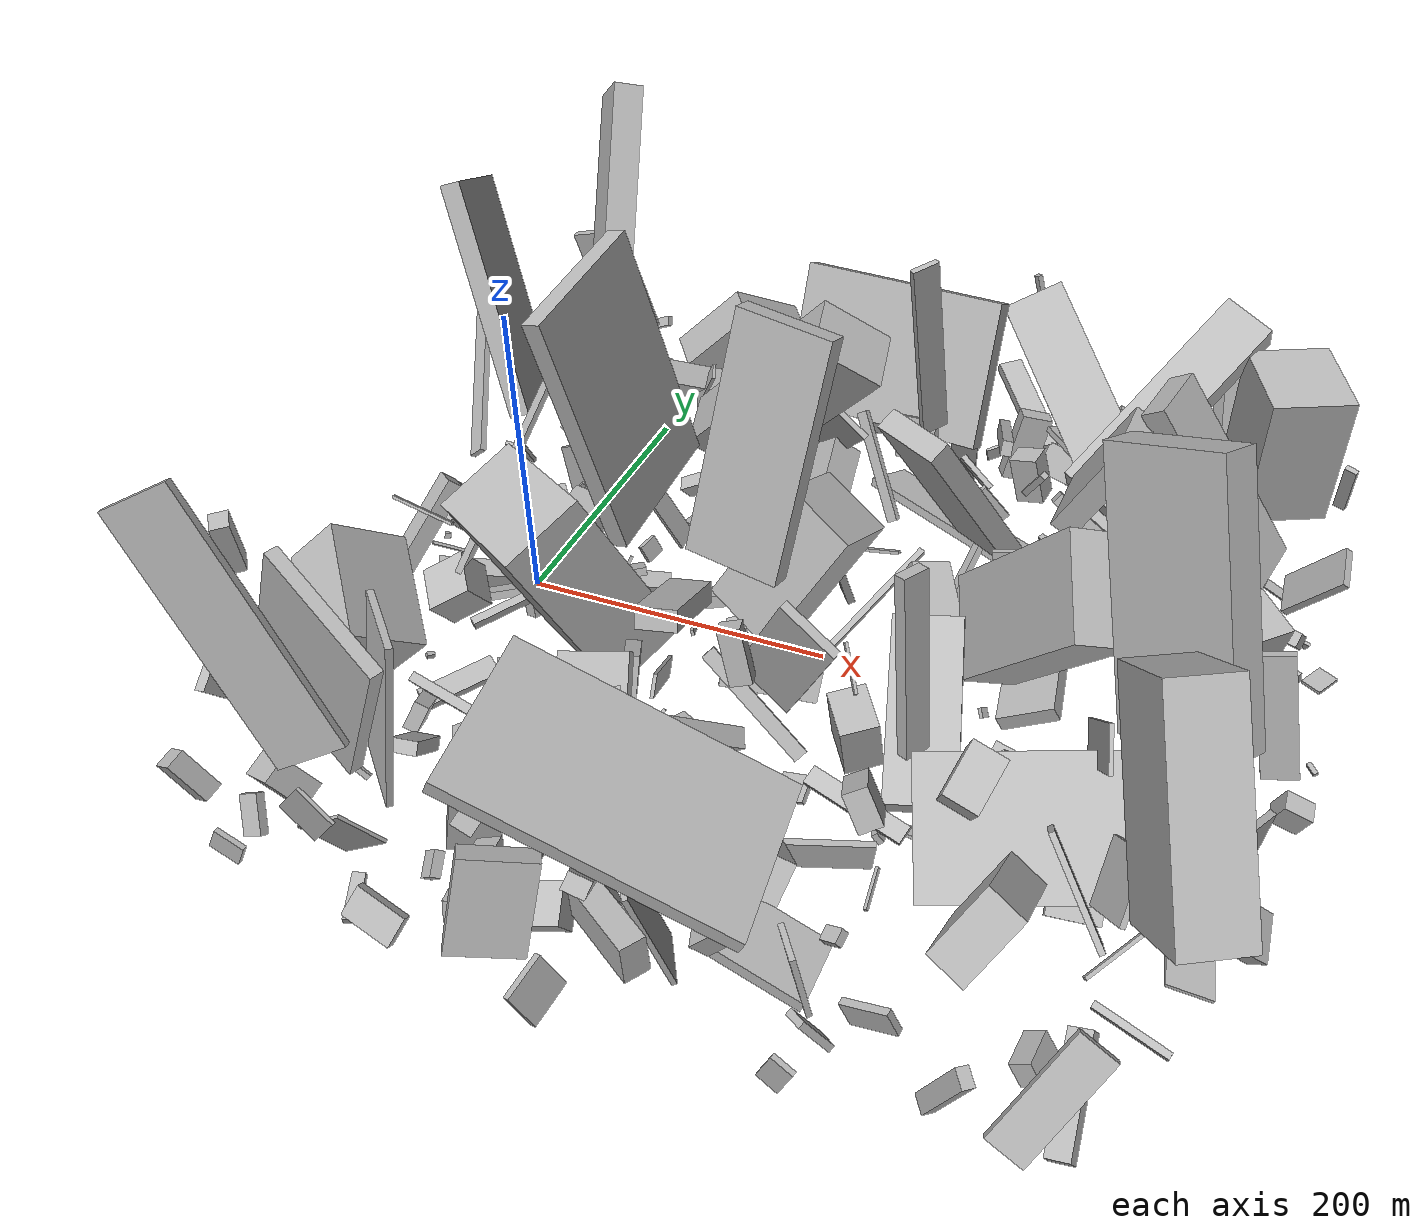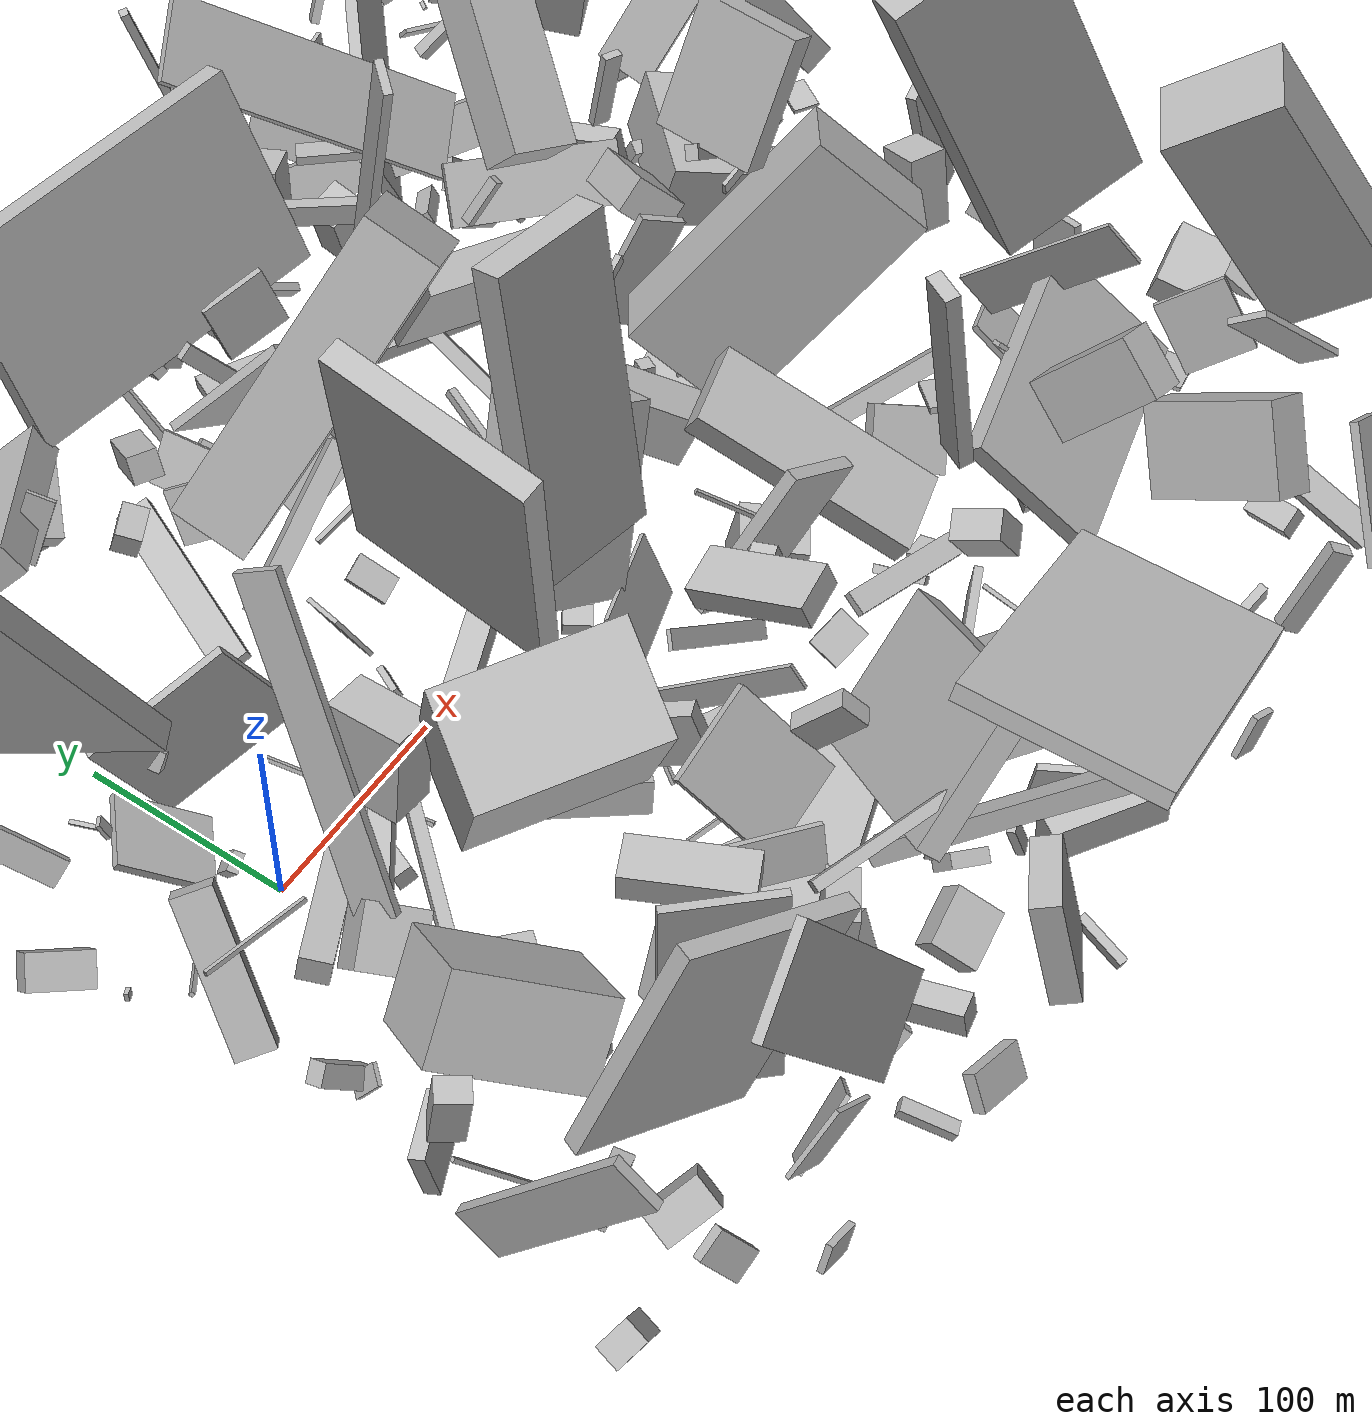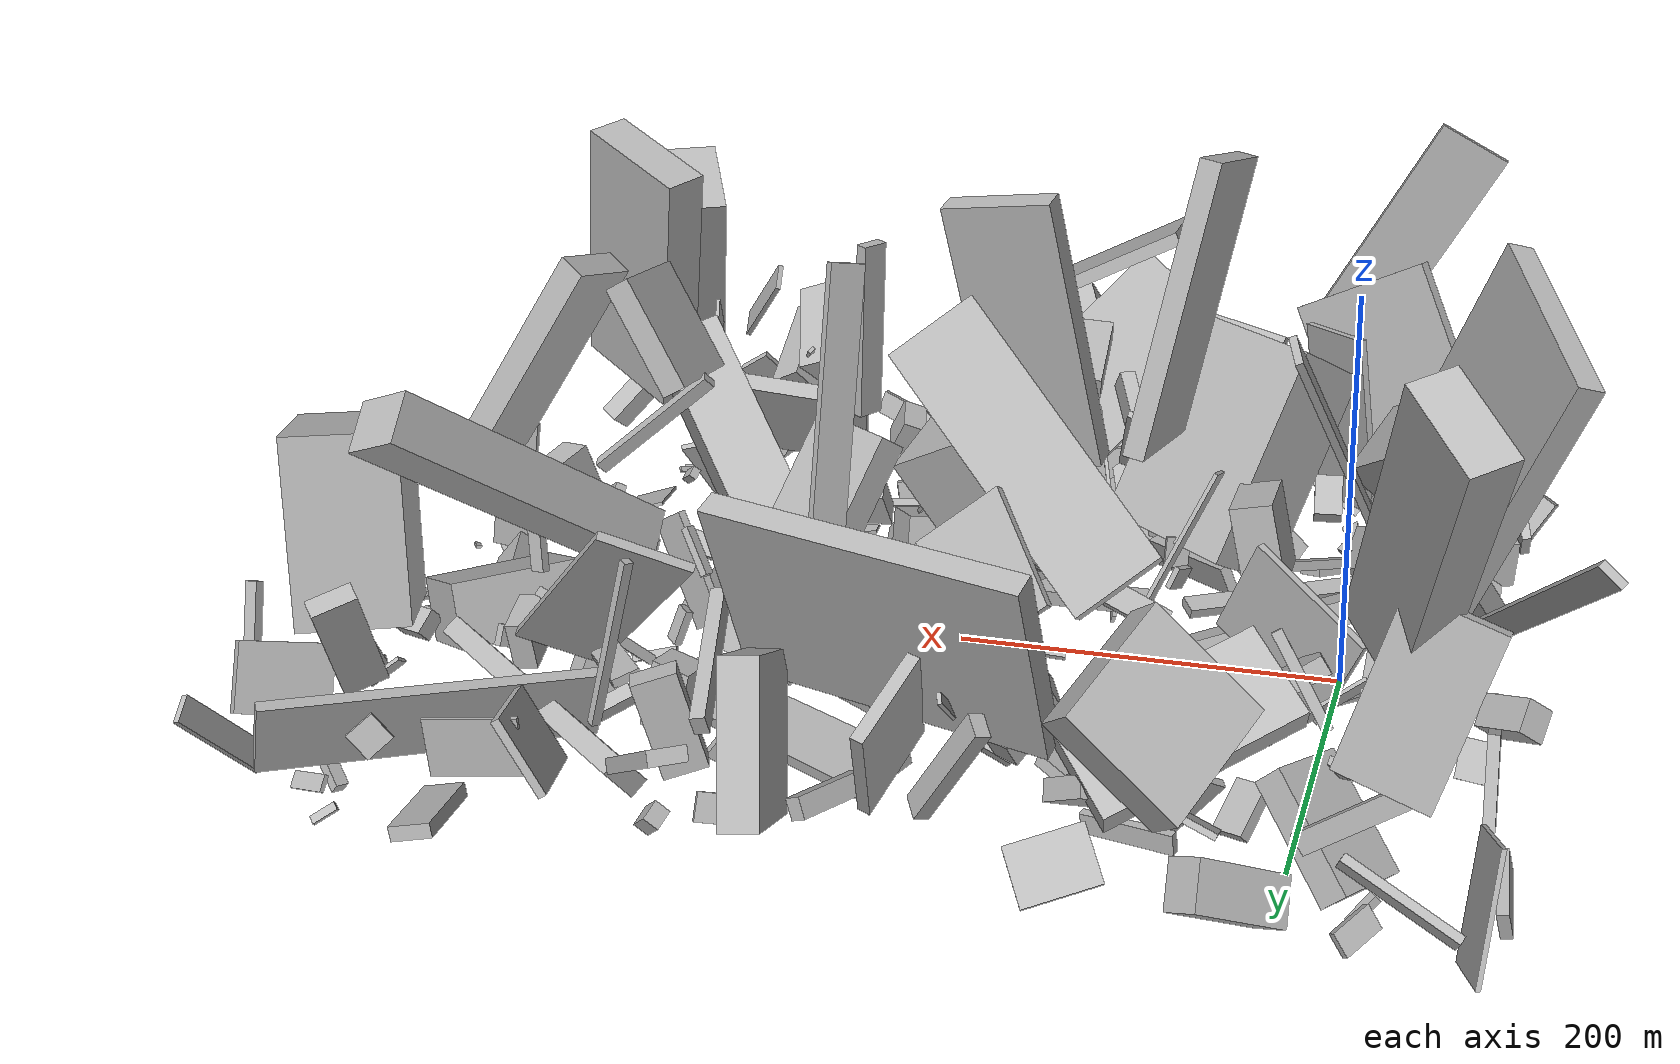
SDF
<sdf version="1.6">
 <world name="default">
  <scene>
   <sky><clouds><speed>12</speed></clouds></sky>
   <ambient>0.4 0.4 0.4 1</ambient>
   <background>0.7 0.7 0.7 1</background>
   <shadows>1</shadows>
  </scene>
  <gravity>0 0 -9.8066</gravity>
  <magnetic_field>6e-06 2.3e-05 -4.2e-05</magnetic_field>
  <physics default="0" name="default_physics" type="ode">
   <ode>
    <solver>
     <type>quick</type>
     <iters>10</iters>
     <sor>1.0</sor>
     <use_dynamic_moi_rescaling>0</use_dynamic_moi_rescaling>
    </solver>
    <constraints>
     <cfm>0</cfm>
     <erp>0.2</erp>
     <contact_max_correcting_vel>100</contact_max_correcting_vel>
     <contact_surface_layer>0.001</contact_surface_layer>
    </constraints>
   </ode>
   <max_step_size>0.004</max_step_size>
   <real_time_factor>1</real_time_factor>
   <real_time_update_rate>250</real_time_update_rate>
  </physics>
  <light name="sun" type="directional">
   <pose>0 0 10 0 0 0</pose>
   <diffuse>0.8 0.8 0.8 1</diffuse>
   <specular>0.2 0.2 0.2 1</specular>
   <attenuation>
    <range>1000</range>
    <constant>0.9</constant>
    <linear>0.01</linear>
    <quadratic>0.001</quadratic>
   </attenuation>
   <direction>-0.5 0.1 -0.9</direction>
  </light>
  <model name="building_1">
   <static>0</static>
   <pose>401.5523927112124 54.036079059480755 28.276010431836145 -1.6262827580335213 -1.3107580423392562 -0.7069547826566642</pose>
   <link name="link">
    <gravity>0</gravity>
    <pose>0 0 33.5 0 0 0</pose>
    <collision name="collision"><geometry><box><size>34 52 67</size></box></geometry></collision>
    <visual name="visual">
     <cast_shadows>0</cast_shadows>
     <geometry><box><size>34 52 67</size></box></geometry>
     <material>
      <script>
       <uri>model://HANNAS_wall/materials/scripts</uri>
       <uri>model://HANNAS_wall/materials/textures</uri>
       <name>vrc/HANNAS_wall</name>
      </script>
     </material>
    </visual>
   </link>
  </model>
  <model name="building_2">
   <static>0</static>
   <pose>370.53598087326293 -178.5250326139376 40.387487703427745 -0.2092710864256462 0.776438382309886 1.647568094168091</pose>
   <link name="link">
    <gravity>0</gravity>
    <pose>0 0 37.0 0 0 0</pose>
    <collision name="collision"><geometry><box><size>10 107 74</size></box></geometry></collision>
    <visual name="visual">
     <cast_shadows>0</cast_shadows>
     <geometry><box><size>10 107 74</size></box></geometry>
     <material>
      <script>
       <uri>model://HANNAS_wall/materials/scripts</uri>
       <uri>model://HANNAS_wall/materials/textures</uri>
       <name>vrc/HANNAS_wall</name>
      </script>
     </material>
    </visual>
   </link>
  </model>
  <model name="building_3">
   <static>0</static>
   <pose>342.60239375288876 -41.4275069649277 71.99341820973707 0.860662383341686 -0.31074108356621444 -2.53120176968325</pose>
   <link name="link">
    <gravity>0</gravity>
    <pose>0 0 31.0 0 0 0</pose>
    <collision name="collision"><geometry><box><size>35 123 62</size></box></geometry></collision>
    <visual name="visual">
     <cast_shadows>0</cast_shadows>
     <geometry><box><size>35 123 62</size></box></geometry>
     <material>
      <script>
       <uri>model://HANNAS_wall/materials/scripts</uri>
       <uri>model://HANNAS_wall/materials/textures</uri>
       <name>vrc/HANNAS_wall</name>
      </script>
     </material>
    </visual>
   </link>
  </model>
  <model name="building_4">
   <static>0</static>
   <pose>228.17869012197627 125.55638589533686 99.13003201223846 0.1654139263675401 0.09466595474658478 -0.6914889241852872</pose>
   <link name="link">
    <gravity>0</gravity>
    <pose>0 0 64.0 0 0 0</pose>
    <collision name="collision"><geometry><box><size>4 18 128</size></box></geometry></collision>
    <visual name="visual">
     <cast_shadows>0</cast_shadows>
     <geometry><box><size>4 18 128</size></box></geometry>
     <material>
      <script>
       <uri>model://HANNAS_wall/materials/scripts</uri>
       <uri>model://HANNAS_wall/materials/textures</uri>
       <name>vrc/HANNAS_wall</name>
      </script>
     </material>
    </visual>
   </link>
  </model>
  <model name="building_5">
   <static>0</static>
   <pose>44.778056149244705 -2.744506497203627 66.14277066838804 1.3153854542540708 -1.363695703409228 0.254666859420948</pose>
   <link name="link">
    <gravity>0</gravity>
    <pose>0 0 18.0 0 0 0</pose>
    <collision name="collision"><geometry><box><size>45 22 36</size></box></geometry></collision>
    <visual name="visual">
     <cast_shadows>0</cast_shadows>
     <geometry><box><size>45 22 36</size></box></geometry>
     <material>
      <script>
       <uri>model://HANNAS_wall/materials/scripts</uri>
       <uri>model://HANNAS_wall/materials/textures</uri>
       <name>vrc/HANNAS_wall</name>
      </script>
     </material>
    </visual>
   </link>
  </model>
  <model name="building_6">
   <static>0</static>
   <pose>407.4585912472862 150.6241460101338 39.54069528543751 1.7625428357951811 0.8658357117565957 -2.0084334795983896</pose>
   <link name="link">
    <gravity>0</gravity>
    <pose>0 0 75.0 0 0 0</pose>
    <collision name="collision"><geometry><box><size>22 10 150</size></box></geometry></collision>
    <visual name="visual">
     <cast_shadows>0</cast_shadows>
     <geometry><box><size>22 10 150</size></box></geometry>
     <material>
      <script>
       <uri>model://HANNAS_wall/materials/scripts</uri>
       <uri>model://HANNAS_wall/materials/textures</uri>
       <name>vrc/HANNAS_wall</name>
      </script>
     </material>
    </visual>
   </link>
  </model>
  <model name="building_7">
   <static>0</static>
   <pose>260.51255282791715 15.565260322514362 29.977483388126927 -0.23190532668931108 0.40965162509561115 -1.037882377212776</pose>
   <link name="link">
    <gravity>0</gravity>
    <pose>0 0 12.5 0 0 0</pose>
    <collision name="collision"><geometry><box><size>63 25 25</size></box></geometry></collision>
    <visual name="visual">
     <cast_shadows>0</cast_shadows>
     <geometry><box><size>63 25 25</size></box></geometry>
     <material>
      <script>
       <uri>model://HANNAS_wall/materials/scripts</uri>
       <uri>model://HANNAS_wall/materials/textures</uri>
       <name>vrc/HANNAS_wall</name>
      </script>
     </material>
    </visual>
   </link>
  </model>
  <model name="building_8">
   <static>0</static>
   <pose>255.84433798821124 95.35408352351342 83.95009106457736 2.1371224104064597 -0.032799270551776775 -0.5828597156465631</pose>
   <link name="link">
    <gravity>0</gravity>
    <pose>0 0 7.5 0 0 0</pose>
    <collision name="collision"><geometry><box><size>51 126 15</size></box></geometry></collision>
    <visual name="visual">
     <cast_shadows>0</cast_shadows>
     <geometry><box><size>51 126 15</size></box></geometry>
     <material>
      <script>
       <uri>model://HANNAS_wall/materials/scripts</uri>
       <uri>model://HANNAS_wall/materials/textures</uri>
       <name>vrc/HANNAS_wall</name>
      </script>
     </material>
    </visual>
   </link>
  </model>
  <model name="building_9">
   <static>0</static>
   <pose>60.13477899382774 -101.71023403036946 83.49066467808512 1.1164398579038701 0.09464951068654272 2.5554855638131153</pose>
   <link name="link">
    <gravity>0</gravity>
    <pose>0 0 25.5 0 0 0</pose>
    <collision name="collision"><geometry><box><size>82 119 51</size></box></geometry></collision>
    <visual name="visual">
     <cast_shadows>0</cast_shadows>
     <geometry><box><size>82 119 51</size></box></geometry>
     <material>
      <script>
       <uri>model://HANNAS_wall/materials/scripts</uri>
       <uri>model://HANNAS_wall/materials/textures</uri>
       <name>vrc/HANNAS_wall</name>
      </script>
     </material>
    </visual>
   </link>
  </model>
  <model name="building_10">
   <static>0</static>
   <pose>159.26238290925542 92.02896353972424 36.88318740638226 -0.866168906942549 0.688343639659553 0.5821362179712117</pose>
   <link name="link">
    <gravity>0</gravity>
    <pose>0 0 23.5 0 0 0</pose>
    <collision name="collision"><geometry><box><size>22 37 47</size></box></geometry></collision>
    <visual name="visual">
     <cast_shadows>0</cast_shadows>
     <geometry><box><size>22 37 47</size></box></geometry>
     <material>
      <script>
       <uri>model://HANNAS_wall/materials/scripts</uri>
       <uri>model://HANNAS_wall/materials/textures</uri>
       <name>vrc/HANNAS_wall</name>
      </script>
     </material>
    </visual>
   </link>
  </model>
  <model name="building_11">
   <static>0</static>
   <pose>190.39763875777464 12.69248213924936 71.6489953485627 0.928114544918503 -0.9965386384299176 0.38226683311756676</pose>
   <link name="link">
    <gravity>0</gravity>
    <pose>0 0 23.0 0 0 0</pose>
    <collision name="collision"><geometry><box><size>88 47 46</size></box></geometry></collision>
    <visual name="visual">
     <cast_shadows>0</cast_shadows>
     <geometry><box><size>88 47 46</size></box></geometry>
     <material>
      <script>
       <uri>model://HANNAS_wall/materials/scripts</uri>
       <uri>model://HANNAS_wall/materials/textures</uri>
       <name>vrc/HANNAS_wall</name>
      </script>
     </material>
    </visual>
   </link>
  </model>
  <model name="building_12">
   <static>0</static>
   <pose>192.65559945761757 -164.8150167388415 68.78255812723728 0.7744313595643079 -0.6766538514125365 -0.12413528434945402</pose>
   <link name="link">
    <gravity>0</gravity>
    <pose>0 0 62.0 0 0 0</pose>
    <collision name="collision"><geometry><box><size>71 11 124</size></box></geometry></collision>
    <visual name="visual">
     <cast_shadows>0</cast_shadows>
     <geometry><box><size>71 11 124</size></box></geometry>
     <material>
      <script>
       <uri>model://HANNAS_wall/materials/scripts</uri>
       <uri>model://HANNAS_wall/materials/textures</uri>
       <name>vrc/HANNAS_wall</name>
      </script>
     </material>
    </visual>
   </link>
  </model>
  <model name="building_13">
   <static>0</static>
   <pose>451.27176359276683 -227.3731676573134 108.29814430692676 -0.032161361023020134 -0.5696261096192541 -1.0396622802903253</pose>
   <link name="link">
    <gravity>0</gravity>
    <pose>0 0 58.5 0 0 0</pose>
    <collision name="collision"><geometry><box><size>54 37 117</size></box></geometry></collision>
    <visual name="visual">
     <cast_shadows>0</cast_shadows>
     <geometry><box><size>54 37 117</size></box></geometry>
     <material>
      <script>
       <uri>model://HANNAS_wall/materials/scripts</uri>
       <uri>model://HANNAS_wall/materials/textures</uri>
       <name>vrc/HANNAS_wall</name>
      </script>
     </material>
    </visual>
   </link>
  </model>
  <model name="building_14">
   <static>0</static>
   <pose>160.7187048860955 -40.6248234948643 91.645018674083 -0.11374480422894169 -0.2537876858411503 -1.6678482407939665</pose>
   <link name="link">
    <gravity>0</gravity>
    <pose>0 0 75.0 0 0 0</pose>
    <collision name="collision"><geometry><box><size>14 59 150</size></box></geometry></collision>
    <visual name="visual">
     <cast_shadows>0</cast_shadows>
     <geometry><box><size>14 59 150</size></box></geometry>
     <material>
      <script>
       <uri>model://HANNAS_wall/materials/scripts</uri>
       <uri>model://HANNAS_wall/materials/textures</uri>
       <name>vrc/HANNAS_wall</name>
      </script>
     </material>
    </visual>
   </link>
  </model>
  <model name="building_15">
   <static>0</static>
   <pose>-19.535070318286742 -119.30955158458937 67.90622841023128 -0.8755035193617655 -0.4528839900669452 2.260460562549237</pose>
   <link name="link">
    <gravity>0</gravity>
    <pose>0 0 25.0 0 0 0</pose>
    <collision name="collision"><geometry><box><size>70 40 50</size></box></geometry></collision>
    <visual name="visual">
     <cast_shadows>0</cast_shadows>
     <geometry><box><size>70 40 50</size></box></geometry>
     <material>
      <script>
       <uri>model://HANNAS_wall/materials/scripts</uri>
       <uri>model://HANNAS_wall/materials/textures</uri>
       <name>vrc/HANNAS_wall</name>
      </script>
     </material>
    </visual>
   </link>
  </model>
  <model name="building_16">
   <static>0</static>
   <pose>172.7355395353499 -241.46146706500215 64.11279238283072 2.3700065892392104 0.3466365825402684 0.09729424033469207</pose>
   <link name="link">
    <gravity>0</gravity>
    <pose>0 0 4.5 0 0 0</pose>
    <collision name="collision"><geometry><box><size>12 150 9</size></box></geometry></collision>
    <visual name="visual">
     <cast_shadows>0</cast_shadows>
     <geometry><box><size>12 150 9</size></box></geometry>
     <material>
      <script>
       <uri>model://HANNAS_wall/materials/scripts</uri>
       <uri>model://HANNAS_wall/materials/textures</uri>
       <name>vrc/HANNAS_wall</name>
      </script>
     </material>
    </visual>
   </link>
  </model>
  <model name="building_17">
   <static>0</static>
   <pose>147.07335124607422 31.586698252664128 56.90004389693871 0.39409373939661796 -0.781526906151696 0.7269519840878601</pose>
   <link name="link">
    <gravity>0</gravity>
    <pose>0 0 2.0 0 0 0</pose>
    <collision name="collision"><geometry><box><size>4 16 4</size></box></geometry></collision>
    <visual name="visual">
     <cast_shadows>0</cast_shadows>
     <geometry><box><size>4 16 4</size></box></geometry>
     <material>
      <script>
       <uri>model://HANNAS_wall/materials/scripts</uri>
       <uri>model://HANNAS_wall/materials/textures</uri>
       <name>vrc/HANNAS_wall</name>
      </script>
     </material>
    </visual>
   </link>
  </model>
  <model name="building_18">
   <static>0</static>
   <pose>170.8844857625791 -256.08720031553906 51.54665389722184 -0.25249838128735286 -1.5036676789013927 2.800130498686935</pose>
   <link name="link">
    <gravity>0</gravity>
    <pose>0 0 26.0 0 0 0</pose>
    <collision name="collision"><geometry><box><size>22 14 52</size></box></geometry></collision>
    <visual name="visual">
     <cast_shadows>0</cast_shadows>
     <geometry><box><size>22 14 52</size></box></geometry>
     <material>
      <script>
       <uri>model://HANNAS_wall/materials/scripts</uri>
       <uri>model://HANNAS_wall/materials/textures</uri>
       <name>vrc/HANNAS_wall</name>
      </script>
     </material>
    </visual>
   </link>
  </model>
  <model name="building_19">
   <static>0</static>
   <pose>-36.991929567998454 195.44361527709134 106.40523324313753 0.6014749438251477 -0.23630089838122537 -2.5452063587975697</pose>
   <link name="link">
    <gravity>0</gravity>
    <pose>0 0 75.0 0 0 0</pose>
    <collision name="collision"><geometry><box><size>21 43 150</size></box></geometry></collision>
    <visual name="visual">
     <cast_shadows>0</cast_shadows>
     <geometry><box><size>21 43 150</size></box></geometry>
     <material>
      <script>
       <uri>model://HANNAS_wall/materials/scripts</uri>
       <uri>model://HANNAS_wall/materials/textures</uri>
       <name>vrc/HANNAS_wall</name>
      </script>
     </material>
    </visual>
   </link>
  </model>
  <model name="building_20">
   <static>0</static>
   <pose>94.09822200327073 98.38151085722018 77.85997008511394 0.6651164806860675 -0.4116509122025526 1.7270880041664904</pose>
   <link name="link">
    <gravity>0</gravity>
    <pose>0 0 75.0 0 0 0</pose>
    <collision name="collision"><geometry><box><size>36 48 150</size></box></geometry></collision>
    <visual name="visual">
     <cast_shadows>0</cast_shadows>
     <geometry><box><size>36 48 150</size></box></geometry>
     <material>
      <script>
       <uri>model://HANNAS_wall/materials/scripts</uri>
       <uri>model://HANNAS_wall/materials/textures</uri>
       <name>vrc/HANNAS_wall</name>
      </script>
     </material>
    </visual>
   </link>
  </model>
  <model name="building_21">
   <static>0</static>
   <pose>284.74256246130386 -236.24703722540053 16.35470775127789 -1.1855751277535895 0.00879005874944561 1.5630458018975113</pose>
   <link name="link">
    <gravity>0</gravity>
    <pose>0 0 26.0 0 0 0</pose>
    <collision name="collision"><geometry><box><size>39 7 52</size></box></geometry></collision>
    <visual name="visual">
     <cast_shadows>0</cast_shadows>
     <geometry><box><size>39 7 52</size></box></geometry>
     <material>
      <script>
       <uri>model://HANNAS_wall/materials/scripts</uri>
       <uri>model://HANNAS_wall/materials/textures</uri>
       <name>vrc/HANNAS_wall</name>
      </script>
     </material>
    </visual>
   </link>
  </model>
  <model name="building_22">
   <static>0</static>
   <pose>246.83429743823993 147.05973577493927 8.956918842114668 -0.22944183199776358 -0.008992836488864609 -0.48987932831853437</pose>
   <link name="link">
    <gravity>0</gravity>
    <pose>0 0 3.0 0 0 0</pose>
    <collision name="collision"><geometry><box><size>150 32 6</size></box></geometry></collision>
    <visual name="visual">
     <cast_shadows>0</cast_shadows>
     <geometry><box><size>150 32 6</size></box></geometry>
     <material>
      <script>
       <uri>model://HANNAS_wall/materials/scripts</uri>
       <uri>model://HANNAS_wall/materials/textures</uri>
       <name>vrc/HANNAS_wall</name>
      </script>
     </material>
    </visual>
   </link>
  </model>
  <model name="building_23">
   <static>0</static>
   <pose>298.5047807039582 -134.69247498267328 78.65586288071418 -0.12396853511134127 0.05370361361767028 1.0615738624359394</pose>
   <link name="link">
    <gravity>0</gravity>
    <pose>0 0 53.0 0 0 0</pose>
    <collision name="collision"><geometry><box><size>16 7 106</size></box></geometry></collision>
    <visual name="visual">
     <cast_shadows>0</cast_shadows>
     <geometry><box><size>16 7 106</size></box></geometry>
     <material>
      <script>
       <uri>model://HANNAS_wall/materials/scripts</uri>
       <uri>model://HANNAS_wall/materials/textures</uri>
       <name>vrc/HANNAS_wall</name>
      </script>
     </material>
    </visual>
   </link>
  </model>
  <model name="building_24">
   <static>0</static>
   <pose>-15.30325132641914 13.638468927713093 27.282446304270735 -0.3785649534801156 -0.45344692399374487 2.0214560540023783</pose>
   <link name="link">
    <gravity>0</gravity>
    <pose>0 0 8.0 0 0 0</pose>
    <collision name="collision"><geometry><box><size>5 9 16</size></box></geometry></collision>
    <visual name="visual">
     <cast_shadows>0</cast_shadows>
     <geometry><box><size>5 9 16</size></box></geometry>
     <material>
      <script>
       <uri>model://HANNAS_wall/materials/scripts</uri>
       <uri>model://HANNAS_wall/materials/textures</uri>
       <name>vrc/HANNAS_wall</name>
      </script>
     </material>
    </visual>
   </link>
  </model>
  <model name="building_25">
   <static>0</static>
   <pose>318.8126764333156 219.92526281814506 101.15092016447481 2.190576327675683 -0.7795607426135756 -1.5544811991809708</pose>
   <link name="link">
    <gravity>0</gravity>
    <pose>0 0 21.0 0 0 0</pose>
    <collision name="collision"><geometry><box><size>4 150 42</size></box></geometry></collision>
    <visual name="visual">
     <cast_shadows>0</cast_shadows>
     <geometry><box><size>4 150 42</size></box></geometry>
     <material>
      <script>
       <uri>model://HANNAS_wall/materials/scripts</uri>
       <uri>model://HANNAS_wall/materials/textures</uri>
       <name>vrc/HANNAS_wall</name>
      </script>
     </material>
    </visual>
   </link>
  </model>
  <model name="building_26">
   <static>0</static>
   <pose>297.3748791144083 -270.2816454704114 19.715043487529577 -1.8548098669640398 -0.521139901863547 1.068378753391968</pose>
   <link name="link">
    <gravity>0</gravity>
    <pose>0 0 6.0 0 0 0</pose>
    <collision name="collision"><geometry><box><size>4 26 12</size></box></geometry></collision>
    <visual name="visual">
     <cast_shadows>0</cast_shadows>
     <geometry><box><size>4 26 12</size></box></geometry>
     <material>
      <script>
       <uri>model://HANNAS_wall/materials/scripts</uri>
       <uri>model://HANNAS_wall/materials/textures</uri>
       <name>vrc/HANNAS_wall</name>
      </script>
     </material>
    </visual>
   </link>
  </model>
  <model name="building_27">
   <static>0</static>
   <pose>13.74465970143904 -116.24034920806787 14.94196082592813 -0.1705758622511373 0.11733676189713037 -2.2309354585838594</pose>
   <link name="link">
    <gravity>0</gravity>
    <pose>0 0 2.0 0 0 0</pose>
    <collision name="collision"><geometry><box><size>47 15 4</size></box></geometry></collision>
    <visual name="visual">
     <cast_shadows>0</cast_shadows>
     <geometry><box><size>47 15 4</size></box></geometry>
     <material>
      <script>
       <uri>model://HANNAS_wall/materials/scripts</uri>
       <uri>model://HANNAS_wall/materials/textures</uri>
       <name>vrc/HANNAS_wall</name>
      </script>
     </material>
    </visual>
   </link>
  </model>
  <model name="building_28">
   <static>0</static>
   <pose>160.47362897193221 -125.85510367707263 18.009385944091832 -1.0356911204883308 -1.3672941690821099 0.6542306050220811</pose>
   <link name="link">
    <gravity>0</gravity>
    <pose>0 0 8.5 0 0 0</pose>
    <collision name="collision"><geometry><box><size>23 36 17</size></box></geometry></collision>
    <visual name="visual">
     <cast_shadows>0</cast_shadows>
     <geometry><box><size>23 36 17</size></box></geometry>
     <material>
      <script>
       <uri>model://HANNAS_wall/materials/scripts</uri>
       <uri>model://HANNAS_wall/materials/textures</uri>
       <name>vrc/HANNAS_wall</name>
      </script>
     </material>
    </visual>
   </link>
  </model>
  <model name="building_29">
   <static>0</static>
   <pose>39.81136026822822 195.73140224076906 21.76191490640496 0.772020333046498 -0.8735557124724231 3.059999052609426</pose>
   <link name="link">
    <gravity>0</gravity>
    <pose>0 0 5.0 0 0 0</pose>
    <collision name="collision"><geometry><box><size>38 4 10</size></box></geometry></collision>
    <visual name="visual">
     <cast_shadows>0</cast_shadows>
     <geometry><box><size>38 4 10</size></box></geometry>
     <material>
      <script>
       <uri>model://HANNAS_wall/materials/scripts</uri>
       <uri>model://HANNAS_wall/materials/textures</uri>
       <name>vrc/HANNAS_wall</name>
      </script>
     </material>
    </visual>
   </link>
  </model>
  <model name="building_30">
   <static>0</static>
   <pose>28.926033329928195 -185.80888653516772 30.63388241619656 0.004264825466254507 -0.6442551364319137 -1.4571450838844509</pose>
   <link name="link">
    <gravity>0</gravity>
    <pose>0 0 4.0 0 0 0</pose>
    <collision name="collision"><geometry><box><size>28 16 8</size></box></geometry></collision>
    <visual name="visual">
     <cast_shadows>0</cast_shadows>
     <geometry><box><size>28 16 8</size></box></geometry>
     <material>
      <script>
       <uri>model://HANNAS_wall/materials/scripts</uri>
       <uri>model://HANNAS_wall/materials/textures</uri>
       <name>vrc/HANNAS_wall</name>
      </script>
     </material>
    </visual>
   </link>
  </model>
  <model name="building_31">
   <static>0</static>
   <pose>42.055347397990644 -216.9180732111798 78.5365733565686 -1.4642324846294754 -1.4266939049242715 0.6672654650277461</pose>
   <link name="link">
    <gravity>0</gravity>
    <pose>0 0 25.0 0 0 0</pose>
    <collision name="collision"><geometry><box><size>108 4 50</size></box></geometry></collision>
    <visual name="visual">
     <cast_shadows>0</cast_shadows>
     <geometry><box><size>108 4 50</size></box></geometry>
     <material>
      <script>
       <uri>model://HANNAS_wall/materials/scripts</uri>
       <uri>model://HANNAS_wall/materials/textures</uri>
       <name>vrc/HANNAS_wall</name>
      </script>
     </material>
    </visual>
   </link>
  </model>
  <model name="building_32">
   <static>0</static>
   <pose>197.98332001199577 -217.67548765249052 142.8872321464193 -1.654249190489673 -0.4386538305539814 -3.0145278928646904</pose>
   <link name="link">
    <gravity>0</gravity>
    <pose>0 0 44.5 0 0 0</pose>
    <collision name="collision"><geometry><box><size>150 8 89</size></box></geometry></collision>
    <visual name="visual">
     <cast_shadows>0</cast_shadows>
     <geometry><box><size>150 8 89</size></box></geometry>
     <material>
      <script>
       <uri>model://HANNAS_wall/materials/scripts</uri>
       <uri>model://HANNAS_wall/materials/textures</uri>
       <name>vrc/HANNAS_wall</name>
      </script>
     </material>
    </visual>
   </link>
  </model>
  <model name="building_33">
   <static>0</static>
   <pose>455.7886217580594 102.60628199560767 19.544798393776755 -1.6280594650465947 0.8171888531796426 -1.960991191095987</pose>
   <link name="link">
    <gravity>0</gravity>
    <pose>0 0 10.0 0 0 0</pose>
    <collision name="collision"><geometry><box><size>9 14 20</size></box></geometry></collision>
    <visual name="visual">
     <cast_shadows>0</cast_shadows>
     <geometry><box><size>9 14 20</size></box></geometry>
     <material>
      <script>
       <uri>model://HANNAS_wall/materials/scripts</uri>
       <uri>model://HANNAS_wall/materials/textures</uri>
       <name>vrc/HANNAS_wall</name>
      </script>
     </material>
    </visual>
   </link>
  </model>
  <model name="building_34">
   <static>0</static>
   <pose>-30.20484504628663 34.5323856704043 17.383747631731975 1.6149548478544853 -0.5825663751012802 2.284457913500342</pose>
   <link name="link">
    <gravity>0</gravity>
    <pose>0 0 18.0 0 0 0</pose>
    <collision name="collision"><geometry><box><size>45 4 36</size></box></geometry></collision>
    <visual name="visual">
     <cast_shadows>0</cast_shadows>
     <geometry><box><size>45 4 36</size></box></geometry>
     <material>
      <script>
       <uri>model://HANNAS_wall/materials/scripts</uri>
       <uri>model://HANNAS_wall/materials/textures</uri>
       <name>vrc/HANNAS_wall</name>
      </script>
     </material>
    </visual>
   </link>
  </model>
  <model name="building_35">
   <static>0</static>
   <pose>322.10760045974797 240.39454420777062 37.82772973732747 -2.9354468873814645 -1.0583733223327632 0.09401110540814224</pose>
   <link name="link">
    <gravity>0</gravity>
    <pose>0 0 2.0 0 0 0</pose>
    <collision name="collision"><geometry><box><size>39 44 4</size></box></geometry></collision>
    <visual name="visual">
     <cast_shadows>0</cast_shadows>
     <geometry><box><size>39 44 4</size></box></geometry>
     <material>
      <script>
       <uri>model://HANNAS_wall/materials/scripts</uri>
       <uri>model://HANNAS_wall/materials/textures</uri>
       <name>vrc/HANNAS_wall</name>
      </script>
     </material>
    </visual>
   </link>
  </model>
  <model name="building_36">
   <static>0</static>
   <pose>-21.493926255507375 -226.3154397715121 25.89433831909068 2.283878639696302 -0.9434738710445192 -2.6021172739589566</pose>
   <link name="link">
    <gravity>0</gravity>
    <pose>0 0 13.0 0 0 0</pose>
    <collision name="collision"><geometry><box><size>28 16 26</size></box></geometry></collision>
    <visual name="visual">
     <cast_shadows>0</cast_shadows>
     <geometry><box><size>28 16 26</size></box></geometry>
     <material>
      <script>
       <uri>model://HANNAS_wall/materials/scripts</uri>
       <uri>model://HANNAS_wall/materials/textures</uri>
       <name>vrc/HANNAS_wall</name>
      </script>
     </material>
    </visual>
   </link>
  </model>
  <model name="building_37">
   <static>0</static>
   <pose>404.8815456990326 -110.85927440892421 34.14366245327488 0.7765079926108097 0.49243879553800746 -0.6857776716222765</pose>
   <link name="link">
    <gravity>0</gravity>
    <pose>0 0 3.5 0 0 0</pose>
    <collision name="collision"><geometry><box><size>11 5 7</size></box></geometry></collision>
    <visual name="visual">
     <cast_shadows>0</cast_shadows>
     <geometry><box><size>11 5 7</size></box></geometry>
     <material>
      <script>
       <uri>model://HANNAS_wall/materials/scripts</uri>
       <uri>model://HANNAS_wall/materials/textures</uri>
       <name>vrc/HANNAS_wall</name>
      </script>
     </material>
    </visual>
   </link>
  </model>
  <model name="building_38">
   <static>0</static>
   <pose>65.04835317907795 250.75795322189708 61.40890547400553 0.9521231421667657 0.5278951409897339 -0.824453036692885</pose>
   <link name="link">
    <gravity>0</gravity>
    <pose>0 0 31.5 0 0 0</pose>
    <collision name="collision"><geometry><box><size>22 63 63</size></box></geometry></collision>
    <visual name="visual">
     <cast_shadows>0</cast_shadows>
     <geometry><box><size>22 63 63</size></box></geometry>
     <material>
      <script>
       <uri>model://HANNAS_wall/materials/scripts</uri>
       <uri>model://HANNAS_wall/materials/textures</uri>
       <name>vrc/HANNAS_wall</name>
      </script>
     </material>
    </visual>
   </link>
  </model>
  <model name="building_39">
   <static>0</static>
   <pose>116.51291447882542 -146.66933766453351 15.271578702733533 -0.06804166189960638 -1.3950843937231159 1.139825785941166</pose>
   <link name="link">
    <gravity>0</gravity>
    <pose>0 0 6.0 0 0 0</pose>
    <collision name="collision"><geometry><box><size>11 32 12</size></box></geometry></collision>
    <visual name="visual">
     <cast_shadows>0</cast_shadows>
     <geometry><box><size>11 32 12</size></box></geometry>
     <material>
      <script>
       <uri>model://HANNAS_wall/materials/scripts</uri>
       <uri>model://HANNAS_wall/materials/textures</uri>
       <name>vrc/HANNAS_wall</name>
      </script>
     </material>
    </visual>
   </link>
  </model>
  <model name="building_40">
   <static>0</static>
   <pose>81.5292968145032 -206.25808592437338 41.836148646674545 1.9453895226269167 -1.3936320498122434 0.1757834339767797</pose>
   <link name="link">
    <gravity>0</gravity>
    <pose>0 0 7.0 0 0 0</pose>
    <collision name="collision"><geometry><box><size>65 28 14</size></box></geometry></collision>
    <visual name="visual">
     <cast_shadows>0</cast_shadows>
     <geometry><box><size>65 28 14</size></box></geometry>
     <material>
      <script>
       <uri>model://HANNAS_wall/materials/scripts</uri>
       <uri>model://HANNAS_wall/materials/textures</uri>
       <name>vrc/HANNAS_wall</name>
      </script>
     </material>
    </visual>
   </link>
  </model>
  <model name="building_41">
   <static>0</static>
   <pose>-33.74149543195303 234.93582793715007 9.813323096186096 1.5978974556556989 0.7907058344630101 -2.526757367083551</pose>
   <link name="link">
    <gravity>0</gravity>
    <pose>0 0 2.0 0 0 0</pose>
    <collision name="collision"><geometry><box><size>4 15 4</size></box></geometry></collision>
    <visual name="visual">
     <cast_shadows>0</cast_shadows>
     <geometry><box><size>4 15 4</size></box></geometry>
     <material>
      <script>
       <uri>model://HANNAS_wall/materials/scripts</uri>
       <uri>model://HANNAS_wall/materials/textures</uri>
       <name>vrc/HANNAS_wall</name>
      </script>
     </material>
    </visual>
   </link>
  </model>
  <model name="building_42">
   <static>0</static>
   <pose>47.56785787581535 193.55038631564204 61.08692737566241 2.7045848603733917 -0.6232896597212882 -0.6908006851312648</pose>
   <link name="link">
    <gravity>0</gravity>
    <pose>0 0 8.0 0 0 0</pose>
    <collision name="collision"><geometry><box><size>45 98 16</size></box></geometry></collision>
    <visual name="visual">
     <cast_shadows>0</cast_shadows>
     <geometry><box><size>45 98 16</size></box></geometry>
     <material>
      <script>
       <uri>model://HANNAS_wall/materials/scripts</uri>
       <uri>model://HANNAS_wall/materials/textures</uri>
       <name>vrc/HANNAS_wall</name>
      </script>
     </material>
    </visual>
   </link>
  </model>
  <model name="building_43">
   <static>0</static>
   <pose>128.8175259623771 -168.4559072783942 44.33646672936675 -0.38592492895103275 0.6846433082310964 1.3121655891506354</pose>
   <link name="link">
    <gravity>0</gravity>
    <pose>0 0 28.5 0 0 0</pose>
    <collision name="collision"><geometry><box><size>4 47 57</size></box></geometry></collision>
    <visual name="visual">
     <cast_shadows>0</cast_shadows>
     <geometry><box><size>4 47 57</size></box></geometry>
     <material>
      <script>
       <uri>model://HANNAS_wall/materials/scripts</uri>
       <uri>model://HANNAS_wall/materials/textures</uri>
       <name>vrc/HANNAS_wall</name>
      </script>
     </material>
    </visual>
   </link>
  </model>
  <model name="building_44">
   <static>0</static>
   <pose>437.65455058654993 187.28184264099127 62.38248355883496 0.00261766738097327 -0.10834398933520083 2.0069209695802566</pose>
   <link name="link">
    <gravity>0</gravity>
    <pose>0 0 45.5 0 0 0</pose>
    <collision name="collision"><geometry><box><size>57 52 91</size></box></geometry></collision>
    <visual name="visual">
     <cast_shadows>0</cast_shadows>
     <geometry><box><size>57 52 91</size></box></geometry>
     <material>
      <script>
       <uri>model://HANNAS_wall/materials/scripts</uri>
       <uri>model://HANNAS_wall/materials/textures</uri>
       <name>vrc/HANNAS_wall</name>
      </script>
     </material>
    </visual>
   </link>
  </model>
  <model name="building_45">
   <static>0</static>
   <pose>37.38668943945802 -267.5259361406471 105.66129239658703 0.5129553614419627 -0.14192077662287586 -1.4431835028182016</pose>
   <link name="link">
    <gravity>0</gravity>
    <pose>0 0 75.0 0 0 0</pose>
    <collision name="collision"><geometry><box><size>4 44 150</size></box></geometry></collision>
    <visual name="visual">
     <cast_shadows>0</cast_shadows>
     <geometry><box><size>4 44 150</size></box></geometry>
     <material>
      <script>
       <uri>model://HANNAS_wall/materials/scripts</uri>
       <uri>model://HANNAS_wall/materials/textures</uri>
       <name>vrc/HANNAS_wall</name>
      </script>
     </material>
    </visual>
   </link>
  </model>
  <model name="building_46">
   <static>0</static>
   <pose>-34.01270636420579 74.30110749328891 89.77980059421813 0.3928609142874488 0.23525536511066883 -2.690229514602487</pose>
   <link name="link">
    <gravity>0</gravity>
    <pose>0 0 75.0 0 0 0</pose>
    <collision name="collision"><geometry><box><size>12 101 150</size></box></geometry></collision>
    <visual name="visual">
     <cast_shadows>0</cast_shadows>
     <geometry><box><size>12 101 150</size></box></geometry>
     <material>
      <script>
       <uri>model://HANNAS_wall/materials/scripts</uri>
       <uri>model://HANNAS_wall/materials/textures</uri>
       <name>vrc/HANNAS_wall</name>
      </script>
     </material>
    </visual>
   </link>
  </model>
  <model name="building_47">
   <static>0</static>
   <pose>262.483425975196 173.59603297082438 18.35967282798807 2.906843778262975 0.9103403238811496 0.31924870117357085</pose>
   <link name="link">
    <gravity>0</gravity>
    <pose>0 0 7.5 0 0 0</pose>
    <collision name="collision"><geometry><box><size>29 4 15</size></box></geometry></collision>
    <visual name="visual">
     <cast_shadows>0</cast_shadows>
     <geometry><box><size>29 4 15</size></box></geometry>
     <material>
      <script>
       <uri>model://HANNAS_wall/materials/scripts</uri>
       <uri>model://HANNAS_wall/materials/textures</uri>
       <name>vrc/HANNAS_wall</name>
      </script>
     </material>
    </visual>
   </link>
  </model>
  <model name="building_48">
   <static>0</static>
   <pose>343.7332078227455 115.50055658258998 30.54460754928127 -0.12066962288144499 -0.8261246692175795 -2.166259265821095</pose>
   <link name="link">
    <gravity>0</gravity>
    <pose>0 0 15.0 0 0 0</pose>
    <collision name="collision"><geometry><box><size>5 83 30</size></box></geometry></collision>
    <visual name="visual">
     <cast_shadows>0</cast_shadows>
     <geometry><box><size>5 83 30</size></box></geometry>
     <material>
      <script>
       <uri>model://HANNAS_wall/materials/scripts</uri>
       <uri>model://HANNAS_wall/materials/textures</uri>
       <name>vrc/HANNAS_wall</name>
      </script>
     </material>
    </visual>
   </link>
  </model>
  <model name="building_49">
   <static>0</static>
   <pose>320.9487859835816 -267.03389192488333 39.93535608771478 1.178652634892157 -1.1845130402778448 -2.9077440429438486</pose>
   <link name="link">
    <gravity>0</gravity>
    <pose>0 0 2.0 0 0 0</pose>
    <collision name="collision"><geometry><box><size>15 27 4</size></box></geometry></collision>
    <visual name="visual">
     <cast_shadows>0</cast_shadows>
     <geometry><box><size>15 27 4</size></box></geometry>
     <material>
      <script>
       <uri>model://HANNAS_wall/materials/scripts</uri>
       <uri>model://HANNAS_wall/materials/textures</uri>
       <name>vrc/HANNAS_wall</name>
      </script>
     </material>
    </visual>
   </link>
  </model>
  <model name="building_50">
   <static>0</static>
   <pose>21.586786002957346 -9.913893449675665 24.553142592630902 -2.2737813572307797 1.3163746159163776 2.9154272464365754</pose>
   <link name="link">
    <gravity>0</gravity>
    <pose>0 0 7.0 0 0 0</pose>
    <collision name="collision"><geometry><box><size>13 146 14</size></box></geometry></collision>
    <visual name="visual">
     <cast_shadows>0</cast_shadows>
     <geometry><box><size>13 146 14</size></box></geometry>
     <material>
      <script>
       <uri>model://HANNAS_wall/materials/scripts</uri>
       <uri>model://HANNAS_wall/materials/textures</uri>
       <name>vrc/HANNAS_wall</name>
      </script>
     </material>
    </visual>
   </link>
  </model>
  <model name="building_51">
   <static>0</static>
   <pose>3.6267591983016567 -36.0760430129864 56.49287037208893 -0.6863389545868653 -0.08577514298369474 -0.6016864799801788</pose>
   <link name="link">
    <gravity>0</gravity>
    <pose>0 0 2.0 0 0 0</pose>
    <collision name="collision"><geometry><box><size>5 4 4</size></box></geometry></collision>
    <visual name="visual">
     <cast_shadows>0</cast_shadows>
     <geometry><box><size>5 4 4</size></box></geometry>
     <material>
      <script>
       <uri>model://HANNAS_wall/materials/scripts</uri>
       <uri>model://HANNAS_wall/materials/textures</uri>
       <name>vrc/HANNAS_wall</name>
      </script>
     </material>
    </visual>
   </link>
  </model>
  <model name="building_52">
   <static>0</static>
   <pose>429.5534553948555 -105.84711818124406 103.94226147831314 -0.20047373564574383 -0.356093156924575 -0.44849057900501116</pose>
   <link name="link">
    <gravity>0</gravity>
    <pose>0 0 75.0 0 0 0</pose>
    <collision name="collision"><geometry><box><size>70 23 150</size></box></geometry></collision>
    <visual name="visual">
     <cast_shadows>0</cast_shadows>
     <geometry><box><size>70 23 150</size></box></geometry>
     <material>
      <script>
       <uri>model://HANNAS_wall/materials/scripts</uri>
       <uri>model://HANNAS_wall/materials/textures</uri>
       <name>vrc/HANNAS_wall</name>
      </script>
     </material>
    </visual>
   </link>
  </model>
  <model name="building_53">
   <static>0</static>
   <pose>100.60390814860959 -15.092230734774791 25.896820279495763 -1.4259927205225118 -0.19645979109741132 -1.2516202834565033</pose>
   <link name="link">
    <gravity>0</gravity>
    <pose>0 0 46.0 0 0 0</pose>
    <collision name="collision"><geometry><box><size>13 8 92</size></box></geometry></collision>
    <visual name="visual">
     <cast_shadows>0</cast_shadows>
     <geometry><box><size>13 8 92</size></box></geometry>
     <material>
      <script>
       <uri>model://HANNAS_wall/materials/scripts</uri>
       <uri>model://HANNAS_wall/materials/textures</uri>
       <name>vrc/HANNAS_wall</name>
      </script>
     </material>
    </visual>
   </link>
  </model>
  <model name="building_54">
   <static>0</static>
   <pose>426.0401064589801 238.5923996086079 11.463200420233129 -2.4110656070231133 0.12562955732534437 -2.035138156353231</pose>
   <link name="link">
    <gravity>0</gravity>
    <pose>0 0 3.0 0 0 0</pose>
    <collision name="collision"><geometry><box><size>6 24 6</size></box></geometry></collision>
    <visual name="visual">
     <cast_shadows>0</cast_shadows>
     <geometry><box><size>6 24 6</size></box></geometry>
     <material>
      <script>
       <uri>model://HANNAS_wall/materials/scripts</uri>
       <uri>model://HANNAS_wall/materials/textures</uri>
       <name>vrc/HANNAS_wall</name>
      </script>
     </material>
    </visual>
   </link>
  </model>
  <model name="building_55">
   <static>0</static>
   <pose>20.288248704480694 267.6215410302659 26.28270576237411 -1.1436431044468642 -0.4209165771703944 0.7734837032444581</pose>
   <link name="link">
    <gravity>0</gravity>
    <pose>0 0 9.0 0 0 0</pose>
    <collision name="collision"><geometry><box><size>47 21 18</size></box></geometry></collision>
    <visual name="visual">
     <cast_shadows>0</cast_shadows>
     <geometry><box><size>47 21 18</size></box></geometry>
     <material>
      <script>
       <uri>model://HANNAS_wall/materials/scripts</uri>
       <uri>model://HANNAS_wall/materials/textures</uri>
       <name>vrc/HANNAS_wall</name>
      </script>
     </material>
    </visual>
   </link>
  </model>
  <model name="building_56">
   <static>0</static>
   <pose>257.33528861197857 -218.55975420019317 64.85705950147504 1.0268353768965743 -0.6498675365199744 -1.0564039076651814</pose>
   <link name="link">
    <gravity>0</gravity>
    <pose>0 0 48.0 0 0 0</pose>
    <collision name="collision"><geometry><box><size>89 21 96</size></box></geometry></collision>
    <visual name="visual">
     <cast_shadows>0</cast_shadows>
     <geometry><box><size>89 21 96</size></box></geometry>
     <material>
      <script>
       <uri>model://HANNAS_wall/materials/scripts</uri>
       <uri>model://HANNAS_wall/materials/textures</uri>
       <name>vrc/HANNAS_wall</name>
      </script>
     </material>
    </visual>
   </link>
  </model>
  <model name="building_57">
   <static>0</static>
   <pose>3.0971568858658696 158.83400276451692 29.963167547131142 -2.9717191477229377 0.7430932668340345 -0.3727582983278649</pose>
   <link name="link">
    <gravity>0</gravity>
    <pose>0 0 29.5 0 0 0</pose>
    <collision name="collision"><geometry><box><size>15 41 59</size></box></geometry></collision>
    <visual name="visual">
     <cast_shadows>0</cast_shadows>
     <geometry><box><size>15 41 59</size></box></geometry>
     <material>
      <script>
       <uri>model://HANNAS_wall/materials/scripts</uri>
       <uri>model://HANNAS_wall/materials/textures</uri>
       <name>vrc/HANNAS_wall</name>
      </script>
     </material>
    </visual>
   </link>
  </model>
  <model name="building_58">
   <static>0</static>
   <pose>11.19550775909859 -31.416532730148703 119.86747916447648 2.0795435457983507 -0.3886245515905573 -3.014081893708881</pose>
   <link name="link">
    <gravity>0</gravity>
    <pose>0 0 10.0 0 0 0</pose>
    <collision name="collision"><geometry><box><size>4 150 20</size></box></geometry></collision>
    <visual name="visual">
     <cast_shadows>0</cast_shadows>
     <geometry><box><size>4 150 20</size></box></geometry>
     <material>
      <script>
       <uri>model://HANNAS_wall/materials/scripts</uri>
       <uri>model://HANNAS_wall/materials/textures</uri>
       <name>vrc/HANNAS_wall</name>
      </script>
     </material>
    </visual>
   </link>
  </model>
  <model name="building_59">
   <static>0</static>
   <pose>-77.23962383034741 -193.77720168416965 57.536331493453645 1.7814912858971435 -0.6945624615126622 1.6019289732765027</pose>
   <link name="link">
    <gravity>0</gravity>
    <pose>0 0 2.5 0 0 0</pose>
    <collision name="collision"><geometry><box><size>25 93 5</size></box></geometry></collision>
    <visual name="visual">
     <cast_shadows>0</cast_shadows>
     <geometry><box><size>25 93 5</size></box></geometry>
     <material>
      <script>
       <uri>model://HANNAS_wall/materials/scripts</uri>
       <uri>model://HANNAS_wall/materials/textures</uri>
       <name>vrc/HANNAS_wall</name>
      </script>
     </material>
    </visual>
   </link>
  </model>
  <model name="building_60">
   <static>0</static>
   <pose>334.009690248206 -160.898185430694 93.36951843825224 0.6492658185666168 0.32001286338644147 -0.0782513143762032</pose>
   <link name="link">
    <gravity>0</gravity>
    <pose>0 0 26.5 0 0 0</pose>
    <collision name="collision"><geometry><box><size>19 29 53</size></box></geometry></collision>
    <visual name="visual">
     <cast_shadows>0</cast_shadows>
     <geometry><box><size>19 29 53</size></box></geometry>
     <material>
      <script>
       <uri>model://HANNAS_wall/materials/scripts</uri>
       <uri>model://HANNAS_wall/materials/textures</uri>
       <name>vrc/HANNAS_wall</name>
      </script>
     </material>
    </visual>
   </link>
  </model>
  <model name="building_61">
   <static>0</static>
   <pose>286.4204097564723 -156.9127805484295 19.52284518778989 0.6105004668334717 -1.4328426200253923 -0.19331418611890286</pose>
   <link name="link">
    <gravity>0</gravity>
    <pose>0 0 75.0 0 0 0</pose>
    <collision name="collision"><geometry><box><size>18 4 150</size></box></geometry></collision>
    <visual name="visual">
     <cast_shadows>0</cast_shadows>
     <geometry><box><size>18 4 150</size></box></geometry>
     <material>
      <script>
       <uri>model://HANNAS_wall/materials/scripts</uri>
       <uri>model://HANNAS_wall/materials/textures</uri>
       <name>vrc/HANNAS_wall</name>
      </script>
     </material>
    </visual>
   </link>
  </model>
  <model name="building_62">
   <static>0</static>
   <pose>385.70483982682134 110.84927908007953 60.38797494655334 0.0726300629908835 0.12162989719234074 -0.37731992142962223</pose>
   <link name="link">
    <gravity>0</gravity>
    <pose>0 0 21.0 0 0 0</pose>
    <collision name="collision"><geometry><box><size>9 4 42</size></box></geometry></collision>
    <visual name="visual">
     <cast_shadows>0</cast_shadows>
     <geometry><box><size>9 4 42</size></box></geometry>
     <material>
      <script>
       <uri>model://HANNAS_wall/materials/scripts</uri>
       <uri>model://HANNAS_wall/materials/textures</uri>
       <name>vrc/HANNAS_wall</name>
      </script>
     </material>
    </visual>
   </link>
  </model>
  <model name="building_63">
   <static>0</static>
   <pose>246.52924225113617 195.55076932814498 101.18943290998635 1.646576446952433 -0.43119676823016745 -1.80322904892218</pose>
   <link name="link">
    <gravity>0</gravity>
    <pose>0 0 75.0 0 0 0</pose>
    <collision name="collision"><geometry><box><size>12 99 150</size></box></geometry></collision>
    <visual name="visual">
     <cast_shadows>0</cast_shadows>
     <geometry><box><size>12 99 150</size></box></geometry>
     <material>
      <script>
       <uri>model://HANNAS_wall/materials/scripts</uri>
       <uri>model://HANNAS_wall/materials/textures</uri>
       <name>vrc/HANNAS_wall</name>
      </script>
     </material>
    </visual>
   </link>
  </model>
  <model name="building_64">
   <static>0</static>
   <pose>204.30791801875387 169.3236426557614 41.128675295167426 -0.33512342265169454 -0.21341822334581886 -0.31619897448257156</pose>
   <link name="link">
    <gravity>0</gravity>
    <pose>0 0 14.5 0 0 0</pose>
    <collision name="collision"><geometry><box><size>32 4 29</size></box></geometry></collision>
    <visual name="visual">
     <cast_shadows>0</cast_shadows>
     <geometry><box><size>32 4 29</size></box></geometry>
     <material>
      <script>
       <uri>model://HANNAS_wall/materials/scripts</uri>
       <uri>model://HANNAS_wall/materials/textures</uri>
       <name>vrc/HANNAS_wall</name>
      </script>
     </material>
    </visual>
   </link>
  </model>
  <model name="building_65">
   <static>0</static>
   <pose>432.44596103158807 -207.22400097175782 10.484632595496535 2.746742332050246 -0.16966712616448046 2.8877092308501147</pose>
   <link name="link">
    <gravity>0</gravity>
    <pose>0 0 2.0 0 0 0</pose>
    <collision name="collision"><geometry><box><size>42 4 4</size></box></geometry></collision>
    <visual name="visual">
     <cast_shadows>0</cast_shadows>
     <geometry><box><size>42 4 4</size></box></geometry>
     <material>
      <script>
       <uri>model://HANNAS_wall/materials/scripts</uri>
       <uri>model://HANNAS_wall/materials/textures</uri>
       <name>vrc/HANNAS_wall</name>
      </script>
     </material>
    </visual>
   </link>
  </model>
  <model name="building_66">
   <static>0</static>
   <pose>301.60683240875255 201.1517540891328 60.749078507138464 -3.134523923734483 -0.2785828495704188 -2.4146996423829132</pose>
   <link name="link">
    <gravity>0</gravity>
    <pose>0 0 2.0 0 0 0</pose>
    <collision name="collision"><geometry><box><size>13 34 4</size></box></geometry></collision>
    <visual name="visual">
     <cast_shadows>0</cast_shadows>
     <geometry><box><size>13 34 4</size></box></geometry>
     <material>
      <script>
       <uri>model://HANNAS_wall/materials/scripts</uri>
       <uri>model://HANNAS_wall/materials/textures</uri>
       <name>vrc/HANNAS_wall</name>
      </script>
     </material>
    </visual>
   </link>
  </model>
  <model name="building_67">
   <static>0</static>
   <pose>352.70728975081016 -237.0237890627676 67.66521607570807 0.6549221650286566 -0.4398067415809264 2.857754411655282</pose>
   <link name="link">
    <gravity>0</gravity>
    <pose>0 0 21.0 0 0 0</pose>
    <collision name="collision"><geometry><box><size>22 65 42</size></box></geometry></collision>
    <visual name="visual">
     <cast_shadows>0</cast_shadows>
     <geometry><box><size>22 65 42</size></box></geometry>
     <material>
      <script>
       <uri>model://HANNAS_wall/materials/scripts</uri>
       <uri>model://HANNAS_wall/materials/textures</uri>
       <name>vrc/HANNAS_wall</name>
      </script>
     </material>
    </visual>
   </link>
  </model>
  <model name="building_68">
   <static>0</static>
   <pose>240.70507803926466 192.09927568786836 22.423612211311614 1.0441341752526783 -0.5906981287490739 2.816656091166284</pose>
   <link name="link">
    <gravity>0</gravity>
    <pose>0 0 2.0 0 0 0</pose>
    <collision name="collision"><geometry><box><size>29 7 4</size></box></geometry></collision>
    <visual name="visual">
     <cast_shadows>0</cast_shadows>
     <geometry><box><size>29 7 4</size></box></geometry>
     <material>
      <script>
       <uri>model://HANNAS_wall/materials/scripts</uri>
       <uri>model://HANNAS_wall/materials/textures</uri>
       <name>vrc/HANNAS_wall</name>
      </script>
     </material>
    </visual>
   </link>
  </model>
  <model name="building_69">
   <static>0</static>
   <pose>188.27796335245407 -156.8519062071281 9.776418969186688 1.6844885207885718 1.2612347591043482 -1.162460556087153</pose>
   <link name="link">
    <gravity>0</gravity>
    <pose>0 0 55.5 0 0 0</pose>
    <collision name="collision"><geometry><box><size>4 37 111</size></box></geometry></collision>
    <visual name="visual">
     <cast_shadows>0</cast_shadows>
     <geometry><box><size>4 37 111</size></box></geometry>
     <material>
      <script>
       <uri>model://HANNAS_wall/materials/scripts</uri>
       <uri>model://HANNAS_wall/materials/textures</uri>
       <name>vrc/HANNAS_wall</name>
      </script>
     </material>
    </visual>
   </link>
  </model>
  <model name="building_70">
   <static>0</static>
   <pose>88.65905766396622 192.63918042807668 8.003514401234632 1.5367970615400475 -0.1730445294510119 -1.8297818944161446</pose>
   <link name="link">
    <gravity>0</gravity>
    <pose>0 0 22.0 0 0 0</pose>
    <collision name="collision"><geometry><box><size>4 10 44</size></box></geometry></collision>
    <visual name="visual">
     <cast_shadows>0</cast_shadows>
     <geometry><box><size>4 10 44</size></box></geometry>
     <material>
      <script>
       <uri>model://HANNAS_wall/materials/scripts</uri>
       <uri>model://HANNAS_wall/materials/textures</uri>
       <name>vrc/HANNAS_wall</name>
      </script>
     </material>
    </visual>
   </link>
  </model>
  <model name="building_71">
   <static>0</static>
   <pose>332.2096381563065 109.97532413309195 82.76106830686967 0.9429857392917886 -0.3257920536015377 2.755988557222945</pose>
   <link name="link">
    <gravity>0</gravity>
    <pose>0 0 75.0 0 0 0</pose>
    <collision name="collision"><geometry><box><size>34 25 150</size></box></geometry></collision>
    <visual name="visual">
     <cast_shadows>0</cast_shadows>
     <geometry><box><size>34 25 150</size></box></geometry>
     <material>
      <script>
       <uri>model://HANNAS_wall/materials/scripts</uri>
       <uri>model://HANNAS_wall/materials/textures</uri>
       <name>vrc/HANNAS_wall</name>
      </script>
     </material>
    </visual>
   </link>
  </model>
  <model name="building_72">
   <static>0</static>
   <pose>231.06967969531726 -100.43621534166671 73.13296865236329 1.0468549678400565 0.13727459754591634 -1.8732882482548863</pose>
   <link name="link">
    <gravity>0</gravity>
    <pose>0 0 19.5 0 0 0</pose>
    <collision name="collision"><geometry><box><size>6 79 39</size></box></geometry></collision>
    <visual name="visual">
     <cast_shadows>0</cast_shadows>
     <geometry><box><size>6 79 39</size></box></geometry>
     <material>
      <script>
       <uri>model://HANNAS_wall/materials/scripts</uri>
       <uri>model://HANNAS_wall/materials/textures</uri>
       <name>vrc/HANNAS_wall</name>
      </script>
     </material>
    </visual>
   </link>
  </model>
  <model name="building_73">
   <static>0</static>
   <pose>-0.06467661539446201 -207.6403695879903 105.65387521206422 1.6181936166871658 -1.1221819288779535 -0.40725379035082354</pose>
   <link name="link">
    <gravity>0</gravity>
    <pose>0 0 4.0 0 0 0</pose>
    <collision name="collision"><geometry><box><size>109 86 8</size></box></geometry></collision>
    <visual name="visual">
     <cast_shadows>0</cast_shadows>
     <geometry><box><size>109 86 8</size></box></geometry>
     <material>
      <script>
       <uri>model://HANNAS_wall/materials/scripts</uri>
       <uri>model://HANNAS_wall/materials/textures</uri>
       <name>vrc/HANNAS_wall</name>
      </script>
     </material>
    </visual>
   </link>
  </model>
  <model name="building_74">
   <static>0</static>
   <pose>280.4753921716781 -124.16142786916669 8.45260010088886 -2.9950580482113254 -0.9058848081765043 -3.014260497745361</pose>
   <link name="link">
    <gravity>0</gravity>
    <pose>0 0 2.0 0 0 0</pose>
    <collision name="collision"><geometry><box><size>7 24 4</size></box></geometry></collision>
    <visual name="visual">
     <cast_shadows>0</cast_shadows>
     <geometry><box><size>7 24 4</size></box></geometry>
     <material>
      <script>
       <uri>model://HANNAS_wall/materials/scripts</uri>
       <uri>model://HANNAS_wall/materials/textures</uri>
       <name>vrc/HANNAS_wall</name>
      </script>
     </material>
    </visual>
   </link>
  </model>
  <model name="building_75">
   <static>0</static>
   <pose>109.69385635925492 166.89216809473487 16.685920964842254 1.6617572279418997 -0.3577526816601804 -0.4363376201095537</pose>
   <link name="link">
    <gravity>0</gravity>
    <pose>0 0 46.0 0 0 0</pose>
    <collision name="collision"><geometry><box><size>16 6 92</size></box></geometry></collision>
    <visual name="visual">
     <cast_shadows>0</cast_shadows>
     <geometry><box><size>16 6 92</size></box></geometry>
     <material>
      <script>
       <uri>model://HANNAS_wall/materials/scripts</uri>
       <uri>model://HANNAS_wall/materials/textures</uri>
       <name>vrc/HANNAS_wall</name>
      </script>
     </material>
    </visual>
   </link>
  </model>
  <model name="building_76">
   <static>0</static>
   <pose>286.62051017520344 -74.94060010370767 51.88302838144966 -2.664255351305102 -0.04366030333273139 0.2529902369752767</pose>
   <link name="link">
    <gravity>0</gravity>
    <pose>0 0 6.5 0 0 0</pose>
    <collision name="collision"><geometry><box><size>41 110 13</size></box></geometry></collision>
    <visual name="visual">
     <cast_shadows>0</cast_shadows>
     <geometry><box><size>41 110 13</size></box></geometry>
     <material>
      <script>
       <uri>model://HANNAS_wall/materials/scripts</uri>
       <uri>model://HANNAS_wall/materials/textures</uri>
       <name>vrc/HANNAS_wall</name>
      </script>
     </material>
    </visual>
   </link>
  </model>
  <model name="building_77">
   <static>0</static>
   <pose>181.8570690344355 160.13765905627568 35.90201999981313 1.1737415076461686 -0.5812599467703655 -0.11875032636745551</pose>
   <link name="link">
    <gravity>0</gravity>
    <pose>0 0 2.0 0 0 0</pose>
    <collision name="collision"><geometry><box><size>8 78 4</size></box></geometry></collision>
    <visual name="visual">
     <cast_shadows>0</cast_shadows>
     <geometry><box><size>8 78 4</size></box></geometry>
     <material>
      <script>
       <uri>model://HANNAS_wall/materials/scripts</uri>
       <uri>model://HANNAS_wall/materials/textures</uri>
       <name>vrc/HANNAS_wall</name>
      </script>
     </material>
    </visual>
   </link>
  </model>
  <model name="building_78">
   <static>0</static>
   <pose>-69.05500821972882 -20.016692343197818 45.925746586712165 1.2667740156166245 0.7178146535718989 0.6640760450265506</pose>
   <link name="link">
    <gravity>0</gravity>
    <pose>0 0 9.0 0 0 0</pose>
    <collision name="collision"><geometry><box><size>11 71 18</size></box></geometry></collision>
    <visual name="visual">
     <cast_shadows>0</cast_shadows>
     <geometry><box><size>11 71 18</size></box></geometry>
     <material>
      <script>
       <uri>model://HANNAS_wall/materials/scripts</uri>
       <uri>model://HANNAS_wall/materials/textures</uri>
       <name>vrc/HANNAS_wall</name>
      </script>
     </material>
    </visual>
   </link>
  </model>
  <model name="building_79">
   <static>0</static>
   <pose>444.4564148594882 45.1613883228408 103.38515640867823 -0.15334966617143608 0.5729789617016624 2.830693427702016</pose>
   <link name="link">
    <gravity>0</gravity>
    <pose>0 0 60.0 0 0 0</pose>
    <collision name="collision"><geometry><box><size>15 37 120</size></box></geometry></collision>
    <visual name="visual">
     <cast_shadows>0</cast_shadows>
     <geometry><box><size>15 37 120</size></box></geometry>
     <material>
      <script>
       <uri>model://HANNAS_wall/materials/scripts</uri>
       <uri>model://HANNAS_wall/materials/textures</uri>
       <name>vrc/HANNAS_wall</name>
      </script>
     </material>
    </visual>
   </link>
  </model>
  <model name="building_80">
   <static>0</static>
   <pose>38.40735266975197 -25.916440771075777 29.807992368216247 0.013754758272744489 -0.3324648982654946 -0.963768154062798</pose>
   <link name="link">
    <gravity>0</gravity>
    <pose>0 0 2.5 0 0 0</pose>
    <collision name="collision"><geometry><box><size>11 100 5</size></box></geometry></collision>
    <visual name="visual">
     <cast_shadows>0</cast_shadows>
     <geometry><box><size>11 100 5</size></box></geometry>
     <material>
      <script>
       <uri>model://HANNAS_wall/materials/scripts</uri>
       <uri>model://HANNAS_wall/materials/textures</uri>
       <name>vrc/HANNAS_wall</name>
      </script>
     </material>
    </visual>
   </link>
  </model>
  <model name="building_81">
   <static>0</static>
   <pose>267.9049571675668 -131.04369640170108 23.267037266874823 0.18546142197246185 -0.425313961932312 1.2600285920249903</pose>
   <link name="link">
    <gravity>0</gravity>
    <pose>0 0 2.0 0 0 0</pose>
    <collision name="collision"><geometry><box><size>11 62 4</size></box></geometry></collision>
    <visual name="visual">
     <cast_shadows>0</cast_shadows>
     <geometry><box><size>11 62 4</size></box></geometry>
     <material>
      <script>
       <uri>model://HANNAS_wall/materials/scripts</uri>
       <uri>model://HANNAS_wall/materials/textures</uri>
       <name>vrc/HANNAS_wall</name>
      </script>
     </material>
    </visual>
   </link>
  </model>
  <model name="building_82">
   <static>0</static>
   <pose>434.9569737012636 -38.29541255970408 59.866751531279455 -2.892799657661666 -1.2378907411383606 0.9427313499507214</pose>
   <link name="link">
    <gravity>0</gravity>
    <pose>0 0 10.5 0 0 0</pose>
    <collision name="collision"><geometry><box><size>38 19 21</size></box></geometry></collision>
    <visual name="visual">
     <cast_shadows>0</cast_shadows>
     <geometry><box><size>38 19 21</size></box></geometry>
     <material>
      <script>
       <uri>model://HANNAS_wall/materials/scripts</uri>
       <uri>model://HANNAS_wall/materials/textures</uri>
       <name>vrc/HANNAS_wall</name>
      </script>
     </material>
    </visual>
   </link>
  </model>
  <model name="building_83">
   <static>0</static>
   <pose>164.31575909930567 -280.4591549754232 20.92920190054249 1.8740435610217325 -0.3602246157586075 -0.3198631383567986</pose>
   <link name="link">
    <gravity>0</gravity>
    <pose>0 0 12.5 0 0 0</pose>
    <collision name="collision"><geometry><box><size>4 24 25</size></box></geometry></collision>
    <visual name="visual">
     <cast_shadows>0</cast_shadows>
     <geometry><box><size>4 24 25</size></box></geometry>
     <material>
      <script>
       <uri>model://HANNAS_wall/materials/scripts</uri>
       <uri>model://HANNAS_wall/materials/textures</uri>
       <name>vrc/HANNAS_wall</name>
      </script>
     </material>
    </visual>
   </link>
  </model>
  <model name="building_84">
   <static>0</static>
   <pose>142.8050403978477 254.7878102235095 37.96091175630559 -0.2959593701829025 0.5469052099843638 2.1654133992850406</pose>
   <link name="link">
    <gravity>0</gravity>
    <pose>0 0 29.0 0 0 0</pose>
    <collision name="collision"><geometry><box><size>11 7 58</size></box></geometry></collision>
    <visual name="visual">
     <cast_shadows>0</cast_shadows>
     <geometry><box><size>11 7 58</size></box></geometry>
     <material>
      <script>
       <uri>model://HANNAS_wall/materials/scripts</uri>
       <uri>model://HANNAS_wall/materials/textures</uri>
       <name>vrc/HANNAS_wall</name>
      </script>
     </material>
    </visual>
   </link>
  </model>
  <model name="building_85">
   <static>0</static>
   <pose>-67.43605131735086 51.27881789525554 55.22328149071778 -0.8900346789164839 0.5775695782136471 0.8311956906063748</pose>
   <link name="link">
    <gravity>0</gravity>
    <pose>0 0 75.0 0 0 0</pose>
    <collision name="collision"><geometry><box><size>4 13 150</size></box></geometry></collision>
    <visual name="visual">
     <cast_shadows>0</cast_shadows>
     <geometry><box><size>4 13 150</size></box></geometry>
     <material>
      <script>
       <uri>model://HANNAS_wall/materials/scripts</uri>
       <uri>model://HANNAS_wall/materials/textures</uri>
       <name>vrc/HANNAS_wall</name>
      </script>
     </material>
    </visual>
   </link>
  </model>
  <model name="building_86">
   <static>0</static>
   <pose>-79.89344231442692 200.83990857174874 33.729544997269294 0.2783712758644961 0.028830114520375132 -0.004179800393548991</pose>
   <link name="link">
    <gravity>0</gravity>
    <pose>0 0 19.5 0 0 0</pose>
    <collision name="collision"><geometry><box><size>5 15 39</size></box></geometry></collision>
    <visual name="visual">
     <cast_shadows>0</cast_shadows>
     <geometry><box><size>5 15 39</size></box></geometry>
     <material>
      <script>
       <uri>model://HANNAS_wall/materials/scripts</uri>
       <uri>model://HANNAS_wall/materials/textures</uri>
       <name>vrc/HANNAS_wall</name>
      </script>
     </material>
    </visual>
   </link>
  </model>
  <model name="building_87">
   <static>0</static>
   <pose>102.16376389358152 -19.573573346609606 112.08620609434865 0.20204767647860034 0.12589782431157232 -1.6097579346735635</pose>
   <link name="link">
    <gravity>0</gravity>
    <pose>0 0 75.0 0 0 0</pose>
    <collision name="collision"><geometry><box><size>94 11 150</size></box></geometry></collision>
    <visual name="visual">
     <cast_shadows>0</cast_shadows>
     <geometry><box><size>94 11 150</size></box></geometry>
     <material>
      <script>
       <uri>model://HANNAS_wall/materials/scripts</uri>
       <uri>model://HANNAS_wall/materials/textures</uri>
       <name>vrc/HANNAS_wall</name>
      </script>
     </material>
    </visual>
   </link>
  </model>
  <model name="building_88">
   <static>0</static>
   <pose>456.3463042884102 259.2965416473673 58.69544090817611 2.2071033719061735 -1.152525604051407 -1.3765216476520516</pose>
   <link name="link">
    <gravity>0</gravity>
    <pose>0 0 21.0 0 0 0</pose>
    <collision name="collision"><geometry><box><size>32 7 42</size></box></geometry></collision>
    <visual name="visual">
     <cast_shadows>0</cast_shadows>
     <geometry><box><size>32 7 42</size></box></geometry>
     <material>
      <script>
       <uri>model://HANNAS_wall/materials/scripts</uri>
       <uri>model://HANNAS_wall/materials/textures</uri>
       <name>vrc/HANNAS_wall</name>
      </script>
     </material>
    </visual>
   </link>
  </model>
  <model name="building_89">
   <static>0</static>
   <pose>342.25140812685754 101.60179613858372 14.435974471599081 -1.3485258826676871 -0.4761052619405995 1.7334654703235495</pose>
   <link name="link">
    <gravity>0</gravity>
    <pose>0 0 11.5 0 0 0</pose>
    <collision name="collision"><geometry><box><size>4 4 23</size></box></geometry></collision>
    <visual name="visual">
     <cast_shadows>0</cast_shadows>
     <geometry><box><size>4 4 23</size></box></geometry>
     <material>
      <script>
       <uri>model://HANNAS_wall/materials/scripts</uri>
       <uri>model://HANNAS_wall/materials/textures</uri>
       <name>vrc/HANNAS_wall</name>
      </script>
     </material>
    </visual>
   </link>
  </model>
  <model name="building_90">
   <static>0</static>
   <pose>375.2456861172891 234.0198272110953 39.999909392299486 -2.912081252389361 1.2014815166298745 -0.6362682034279783</pose>
   <link name="link">
    <gravity>0</gravity>
    <pose>0 0 3.0 0 0 0</pose>
    <collision name="collision"><geometry><box><size>36 150 6</size></box></geometry></collision>
    <visual name="visual">
     <cast_shadows>0</cast_shadows>
     <geometry><box><size>36 150 6</size></box></geometry>
     <material>
      <script>
       <uri>model://HANNAS_wall/materials/scripts</uri>
       <uri>model://HANNAS_wall/materials/textures</uri>
       <name>vrc/HANNAS_wall</name>
      </script>
     </material>
    </visual>
   </link>
  </model>
  <model name="building_91">
   <static>0</static>
   <pose>219.94579322952325 255.52894919669794 55.923452049077284 1.9263853605745411 0.03474488821453532 0.19867803928889713</pose>
   <link name="link">
    <gravity>0</gravity>
    <pose>0 0 31.5 0 0 0</pose>
    <collision name="collision"><geometry><box><size>18 73 63</size></box></geometry></collision>
    <visual name="visual">
     <cast_shadows>0</cast_shadows>
     <geometry><box><size>18 73 63</size></box></geometry>
     <material>
      <script>
       <uri>model://HANNAS_wall/materials/scripts</uri>
       <uri>model://HANNAS_wall/materials/textures</uri>
       <name>vrc/HANNAS_wall</name>
      </script>
     </material>
    </visual>
   </link>
  </model>
  <model name="building_92">
   <static>0</static>
   <pose>401.903777154066 254.43615798046574 84.09249106973095 2.033854022043411 -0.2708171890643756 -2.4038582705777247</pose>
   <link name="link">
    <gravity>0</gravity>
    <pose>0 0 5.0 0 0 0</pose>
    <collision name="collision"><geometry><box><size>20 57 10</size></box></geometry></collision>
    <visual name="visual">
     <cast_shadows>0</cast_shadows>
     <geometry><box><size>20 57 10</size></box></geometry>
     <material>
      <script>
       <uri>model://HANNAS_wall/materials/scripts</uri>
       <uri>model://HANNAS_wall/materials/textures</uri>
       <name>vrc/HANNAS_wall</name>
      </script>
     </material>
    </visual>
   </link>
  </model>
  <model name="building_93">
   <static>0</static>
   <pose>47.04210110501532 41.31547956295458 63.7975307350153 2.078477752223365 -0.09132652222053321 -2.1198149634703136</pose>
   <link name="link">
    <gravity>0</gravity>
    <pose>0 0 35.5 0 0 0</pose>
    <collision name="collision"><geometry><box><size>4 57 71</size></box></geometry></collision>
    <visual name="visual">
     <cast_shadows>0</cast_shadows>
     <geometry><box><size>4 57 71</size></box></geometry>
     <material>
      <script>
       <uri>model://HANNAS_wall/materials/scripts</uri>
       <uri>model://HANNAS_wall/materials/textures</uri>
       <name>vrc/HANNAS_wall</name>
      </script>
     </material>
    </visual>
   </link>
  </model>
  <model name="building_94">
   <static>0</static>
   <pose>172.85004721239002 123.91050046894952 73.08390082262079 0.8129132900208634 0.41974611180112015 -1.965882683772748</pose>
   <link name="link">
    <gravity>0</gravity>
    <pose>0 0 25.5 0 0 0</pose>
    <collision name="collision"><geometry><box><size>4 63 51</size></box></geometry></collision>
    <visual name="visual">
     <cast_shadows>0</cast_shadows>
     <geometry><box><size>4 63 51</size></box></geometry>
     <material>
      <script>
       <uri>model://HANNAS_wall/materials/scripts</uri>
       <uri>model://HANNAS_wall/materials/textures</uri>
       <name>vrc/HANNAS_wall</name>
      </script>
     </material>
    </visual>
   </link>
  </model>
  <model name="building_95">
   <static>0</static>
   <pose>283.24605566816837 191.1878937028001 38.9009379998721 1.6128154147787748 -0.2357029108980094 -0.12877088685354252</pose>
   <link name="link">
    <gravity>0</gravity>
    <pose>0 0 8.5 0 0 0</pose>
    <collision name="collision"><geometry><box><size>19 33 17</size></box></geometry></collision>
    <visual name="visual">
     <cast_shadows>0</cast_shadows>
     <geometry><box><size>19 33 17</size></box></geometry>
     <material>
      <script>
       <uri>model://HANNAS_wall/materials/scripts</uri>
       <uri>model://HANNAS_wall/materials/textures</uri>
       <name>vrc/HANNAS_wall</name>
      </script>
     </material>
    </visual>
   </link>
  </model>
  <model name="building_96">
   <static>0</static>
   <pose>-37.56960170951569 -246.48417713197412 15.367643678904642 -2.091616285076537 -0.4677627483496183 -0.08022161256792368</pose>
   <link name="link">
    <gravity>0</gravity>
    <pose>0 0 2.5 0 0 0</pose>
    <collision name="collision"><geometry><box><size>15 23 5</size></box></geometry></collision>
    <visual name="visual">
     <cast_shadows>0</cast_shadows>
     <geometry><box><size>15 23 5</size></box></geometry>
     <material>
      <script>
       <uri>model://HANNAS_wall/materials/scripts</uri>
       <uri>model://HANNAS_wall/materials/textures</uri>
       <name>vrc/HANNAS_wall</name>
      </script>
     </material>
    </visual>
   </link>
  </model>
  <model name="building_97">
   <static>0</static>
   <pose>267.0699704288968 275.1335319181406 103.35628474804531 -2.048152595103247 -1.2984742276065053 2.9880316972899457</pose>
   <link name="link">
    <gravity>0</gravity>
    <pose>0 0 2.0 0 0 0</pose>
    <collision name="collision"><geometry><box><size>77 4 4</size></box></geometry></collision>
    <visual name="visual">
     <cast_shadows>0</cast_shadows>
     <geometry><box><size>77 4 4</size></box></geometry>
     <material>
      <script>
       <uri>model://HANNAS_wall/materials/scripts</uri>
       <uri>model://HANNAS_wall/materials/textures</uri>
       <name>vrc/HANNAS_wall</name>
      </script>
     </material>
    </visual>
   </link>
  </model>
  <model name="building_98">
   <static>0</static>
   <pose>68.57291536554484 189.85977787512414 21.272554055263484 -0.9201270914004317 -0.991508661698726 -1.3734487569067695</pose>
   <link name="link">
    <gravity>0</gravity>
    <pose>0 0 18.0 0 0 0</pose>
    <collision name="collision"><geometry><box><size>10 27 36</size></box></geometry></collision>
    <visual name="visual">
     <cast_shadows>0</cast_shadows>
     <geometry><box><size>10 27 36</size></box></geometry>
     <material>
      <script>
       <uri>model://HANNAS_wall/materials/scripts</uri>
       <uri>model://HANNAS_wall/materials/textures</uri>
       <name>vrc/HANNAS_wall</name>
      </script>
     </material>
    </visual>
   </link>
  </model>
  <model name="building_99">
   <static>0</static>
   <pose>65.05039845798211 -155.71467629238504 53.74440786786024 1.647272386277625 0.014075715308959059 2.023824696408347</pose>
   <link name="link">
    <gravity>0</gravity>
    <pose>0 0 11.0 0 0 0</pose>
    <collision name="collision"><geometry><box><size>56 14 22</size></box></geometry></collision>
    <visual name="visual">
     <cast_shadows>0</cast_shadows>
     <geometry><box><size>56 14 22</size></box></geometry>
     <material>
      <script>
       <uri>model://HANNAS_wall/materials/scripts</uri>
       <uri>model://HANNAS_wall/materials/textures</uri>
       <name>vrc/HANNAS_wall</name>
      </script>
     </material>
    </visual>
   </link>
  </model>
  <model name="building_100">
   <static>0</static>
   <pose>221.91355019414289 43.489029411065594 18.566696221605696 1.3189146381726775 0.2344433811393635 -1.9215647651249672</pose>
   <link name="link">
    <gravity>0</gravity>
    <pose>0 0 2.0 0 0 0</pose>
    <collision name="collision"><geometry><box><size>93 4 4</size></box></geometry></collision>
    <visual name="visual">
     <cast_shadows>0</cast_shadows>
     <geometry><box><size>93 4 4</size></box></geometry>
     <material>
      <script>
       <uri>model://HANNAS_wall/materials/scripts</uri>
       <uri>model://HANNAS_wall/materials/textures</uri>
       <name>vrc/HANNAS_wall</name>
      </script>
     </material>
    </visual>
   </link>
  </model>
  <model name="building_101">
   <static>0</static>
   <pose>-80.50775036444769 -236.44643370881425 19.568754966464535 2.579005609089667 -0.9886999041580677 -2.837595979776282</pose>
   <link name="link">
    <gravity>0</gravity>
    <pose>0 0 8.0 0 0 0</pose>
    <collision name="collision"><geometry><box><size>30 12 16</size></box></geometry></collision>
    <visual name="visual">
     <cast_shadows>0</cast_shadows>
     <geometry><box><size>30 12 16</size></box></geometry>
     <material>
      <script>
       <uri>model://HANNAS_wall/materials/scripts</uri>
       <uri>model://HANNAS_wall/materials/textures</uri>
       <name>vrc/HANNAS_wall</name>
      </script>
     </material>
    </visual>
   </link>
  </model>
  <model name="building_102">
   <static>0</static>
   <pose>-24.691626471100154 -71.68963378919017 36.888186750137706 1.0141726899835417 -0.37536351839058724 2.222005344900936</pose>
   <link name="link">
    <gravity>0</gravity>
    <pose>0 0 14.0 0 0 0</pose>
    <collision name="collision"><geometry><box><size>28 25 28</size></box></geometry></collision>
    <visual name="visual">
     <cast_shadows>0</cast_shadows>
     <geometry><box><size>28 25 28</size></box></geometry>
     <material>
      <script>
       <uri>model://HANNAS_wall/materials/scripts</uri>
       <uri>model://HANNAS_wall/materials/textures</uri>
       <name>vrc/HANNAS_wall</name>
      </script>
     </material>
    </visual>
   </link>
  </model>
  <model name="building_103">
   <static>0</static>
   <pose>359.18633590871787 -65.87089761354629 14.409092041124344 3.089017653341033 -0.6787665125227379 1.2473484382402</pose>
   <link name="link">
    <gravity>0</gravity>
    <pose>0 0 6.5 0 0 0</pose>
    <collision name="collision"><geometry><box><size>9 80 13</size></box></geometry></collision>
    <visual name="visual">
     <cast_shadows>0</cast_shadows>
     <geometry><box><size>9 80 13</size></box></geometry>
     <material>
      <script>
       <uri>model://HANNAS_wall/materials/scripts</uri>
       <uri>model://HANNAS_wall/materials/textures</uri>
       <name>vrc/HANNAS_wall</name>
      </script>
     </material>
    </visual>
   </link>
  </model>
  <model name="building_104">
   <static>0</static>
   <pose>390.94828108683663 28.439659153981044 88.75951367055427 -0.4877125378095932 -0.7717038134458264 0.7432010482865</pose>
   <link name="link">
    <gravity>0</gravity>
    <pose>0 0 40.0 0 0 0</pose>
    <collision name="collision"><geometry><box><size>7 6 80</size></box></geometry></collision>
    <visual name="visual">
     <cast_shadows>0</cast_shadows>
     <geometry><box><size>7 6 80</size></box></geometry>
     <material>
      <script>
       <uri>model://HANNAS_wall/materials/scripts</uri>
       <uri>model://HANNAS_wall/materials/textures</uri>
       <name>vrc/HANNAS_wall</name>
      </script>
     </material>
    </visual>
   </link>
  </model>
  <model name="building_105">
   <static>0</static>
   <pose>121.29701242689217 -16.899383174720217 13.27989947409276 0.6845574657409004 1.2496736858447386 -0.6403095690245395</pose>
   <link name="link">
    <gravity>0</gravity>
    <pose>0 0 4.0 0 0 0</pose>
    <collision name="collision"><geometry><box><size>4 2 8</size></box></geometry></collision>
    <visual name="visual">
     <cast_shadows>0</cast_shadows>
     <geometry><box><size>4 2 8</size></box></geometry>
     <material>
      <script>
       <uri>model://HANNAS_wall/materials/scripts</uri>
       <uri>model://HANNAS_wall/materials/textures</uri>
       <name>vrc/HANNAS_wall</name>
      </script>
     </material>
    </visual>
   </link>
  </model>
  <model name="building_106">
   <static>0</static>
   <pose>-22.653697577567367 108.85219418257869 46.468556305545725 -0.42116489595931716 -0.6556310355510672 -1.6150396552650936</pose>
   <link name="link">
    <gravity>0</gravity>
    <pose>0 0 1.0 0 0 0</pose>
    <collision name="collision"><geometry><box><size>45 6 2</size></box></geometry></collision>
    <visual name="visual">
     <cast_shadows>0</cast_shadows>
     <geometry><box><size>45 6 2</size></box></geometry>
     <material>
      <script>
       <uri>model://HANNAS_wall/materials/scripts</uri>
       <uri>model://HANNAS_wall/materials/textures</uri>
       <name>vrc/HANNAS_wall</name>
      </script>
     </material>
    </visual>
   </link>
  </model>
  <model name="building_107">
   <static>0</static>
   <pose>282.11127247751904 234.60121358294484 28.71746233364309 -0.09137404149312058 1.1022167250580759 2.2021808461702816</pose>
   <link name="link">
    <gravity>0</gravity>
    <pose>0 0 36.0 0 0 0</pose>
    <collision name="collision"><geometry><box><size>7 17 72</size></box></geometry></collision>
    <visual name="visual">
     <cast_shadows>0</cast_shadows>
     <geometry><box><size>7 17 72</size></box></geometry>
     <material>
      <script>
       <uri>model://HANNAS_wall/materials/scripts</uri>
       <uri>model://HANNAS_wall/materials/textures</uri>
       <name>vrc/HANNAS_wall</name>
      </script>
     </material>
    </visual>
   </link>
  </model>
  <model name="building_108">
   <static>0</static>
   <pose>134.51749401031947 -100.51323365979732 13.39839643581793 -2.5728118656169143 -0.6028708235725391 1.1151201369019275</pose>
   <link name="link">
    <gravity>0</gravity>
    <pose>0 0 1.0 0 0 0</pose>
    <collision name="collision"><geometry><box><size>16 2 2</size></box></geometry></collision>
    <visual name="visual">
     <cast_shadows>0</cast_shadows>
     <geometry><box><size>16 2 2</size></box></geometry>
     <material>
      <script>
       <uri>model://HANNAS_wall/materials/scripts</uri>
       <uri>model://HANNAS_wall/materials/textures</uri>
       <name>vrc/HANNAS_wall</name>
      </script>
     </material>
    </visual>
   </link>
  </model>
  <model name="building_109">
   <static>0</static>
   <pose>238.58134468987856 -62.42082662058763 24.848969303186898 -2.4177405352910255 -1.3720510608094183 -1.7074434025446192</pose>
   <link name="link">
    <gravity>0</gravity>
    <pose>0 0 15.5 0 0 0</pose>
    <collision name="collision"><geometry><box><size>36 23 31</size></box></geometry></collision>
    <visual name="visual">
     <cast_shadows>0</cast_shadows>
     <geometry><box><size>36 23 31</size></box></geometry>
     <material>
      <script>
       <uri>model://HANNAS_wall/materials/scripts</uri>
       <uri>model://HANNAS_wall/materials/textures</uri>
       <name>vrc/HANNAS_wall</name>
      </script>
     </material>
    </visual>
   </link>
  </model>
  <model name="building_110">
   <static>0</static>
   <pose>-80.55149635185131 111.03139016333178 17.670570271075857 1.4947455478342635 -0.4791080192908063 1.4872667559937331</pose>
   <link name="link">
    <gravity>0</gravity>
    <pose>0 0 8.5 0 0 0</pose>
    <collision name="collision"><geometry><box><size>3 19 17</size></box></geometry></collision>
    <visual name="visual">
     <cast_shadows>0</cast_shadows>
     <geometry><box><size>3 19 17</size></box></geometry>
     <material>
      <script>
       <uri>model://HANNAS_wall/materials/scripts</uri>
       <uri>model://HANNAS_wall/materials/textures</uri>
       <name>vrc/HANNAS_wall</name>
      </script>
     </material>
    </visual>
   </link>
  </model>
  <model name="building_111">
   <static>0</static>
   <pose>87.80346423057469 -79.54452482877798 17.32298285426276 0.11153918212735218 0.3478860569049579 0.7764847989527623</pose>
   <link name="link">
    <gravity>0</gravity>
    <pose>0 0 8.0 0 0 0</pose>
    <collision name="collision"><geometry><box><size>6 74 16</size></box></geometry></collision>
    <visual name="visual">
     <cast_shadows>0</cast_shadows>
     <geometry><box><size>6 74 16</size></box></geometry>
     <material>
      <script>
       <uri>model://HANNAS_wall/materials/scripts</uri>
       <uri>model://HANNAS_wall/materials/textures</uri>
       <name>vrc/HANNAS_wall</name>
      </script>
     </material>
    </visual>
   </link>
  </model>
  <model name="building_112">
   <static>0</static>
   <pose>103.27885499697618 -34.339830177985384 12.90645090383228 -2.289157375866403 -0.22311491774592782 2.486664196735993</pose>
   <link name="link">
    <gravity>0</gravity>
    <pose>0 0 5.0 0 0 0</pose>
    <collision name="collision"><geometry><box><size>11 3 10</size></box></geometry></collision>
    <visual name="visual">
     <cast_shadows>0</cast_shadows>
     <geometry><box><size>11 3 10</size></box></geometry>
     <material>
      <script>
       <uri>model://HANNAS_wall/materials/scripts</uri>
       <uri>model://HANNAS_wall/materials/textures</uri>
       <name>vrc/HANNAS_wall</name>
      </script>
     </material>
    </visual>
   </link>
  </model>
  <model name="building_113">
   <static>0</static>
   <pose>356.4210451000569 173.24468996572386 12.141433528414993 -1.8444374980593716 -0.6588562107131558 0.5048268383937032</pose>
   <link name="link">
    <gravity>0</gravity>
    <pose>0 0 2.0 0 0 0</pose>
    <collision name="collision"><geometry><box><size>16 14 4</size></box></geometry></collision>
    <visual name="visual">
     <cast_shadows>0</cast_shadows>
     <geometry><box><size>16 14 4</size></box></geometry>
     <material>
      <script>
       <uri>model://HANNAS_wall/materials/scripts</uri>
       <uri>model://HANNAS_wall/materials/textures</uri>
       <name>vrc/HANNAS_wall</name>
      </script>
     </material>
    </visual>
   </link>
  </model>
  <model name="building_114">
   <static>0</static>
   <pose>458.5723422840753 -19.517276054769635 54.203806730627164 0.6419470222206541 -1.343139591919606 2.649875202881982</pose>
   <link name="link">
    <gravity>0</gravity>
    <pose>0 0 10.5 0 0 0</pose>
    <collision name="collision"><geometry><box><size>80 5 21</size></box></geometry></collision>
    <visual name="visual">
     <cast_shadows>0</cast_shadows>
     <geometry><box><size>80 5 21</size></box></geometry>
     <material>
      <script>
       <uri>model://HANNAS_wall/materials/scripts</uri>
       <uri>model://HANNAS_wall/materials/textures</uri>
       <name>vrc/HANNAS_wall</name>
      </script>
     </material>
    </visual>
   </link>
  </model>
  <model name="building_115">
   <static>0</static>
   <pose>315.9784656247084 104.10030043317326 38.809826641255384 -1.6954143861028885 -0.3574071462531633 0.83935980852533</pose>
   <link name="link">
    <gravity>0</gravity>
    <pose>0 0 4.5 0 0 0</pose>
    <collision name="collision"><geometry><box><size>4 18 9</size></box></geometry></collision>
    <visual name="visual">
     <cast_shadows>0</cast_shadows>
     <geometry><box><size>4 18 9</size></box></geometry>
     <material>
      <script>
       <uri>model://HANNAS_wall/materials/scripts</uri>
       <uri>model://HANNAS_wall/materials/textures</uri>
       <name>vrc/HANNAS_wall</name>
      </script>
     </material>
    </visual>
   </link>
  </model>
  <model name="building_116">
   <static>0</static>
   <pose>407.8649594581842 -278.0803869160525 43.457846965648436 -0.8295167075805079 0.7928625091750712 -2.301087452929459</pose>
   <link name="link">
    <gravity>0</gravity>
    <pose>0 0 2.0 0 0 0</pose>
    <collision name="collision"><geometry><box><size>64 22 4</size></box></geometry></collision>
    <visual name="visual">
     <cast_shadows>0</cast_shadows>
     <geometry><box><size>64 22 4</size></box></geometry>
     <material>
      <script>
       <uri>model://HANNAS_wall/materials/scripts</uri>
       <uri>model://HANNAS_wall/materials/textures</uri>
       <name>vrc/HANNAS_wall</name>
      </script>
     </material>
    </visual>
   </link>
  </model>
  <model name="building_117">
   <static>0</static>
   <pose>93.22158286936086 -2.7025622555865985 12.57654559285771 -0.21647198349027924 0.33574865677376137 2.296110096925647</pose>
   <link name="link">
    <gravity>0</gravity>
    <pose>0 0 1.0 0 0 0</pose>
    <collision name="collision"><geometry><box><size>16 7 2</size></box></geometry></collision>
    <visual name="visual">
     <cast_shadows>0</cast_shadows>
     <geometry><box><size>16 7 2</size></box></geometry>
     <material>
      <script>
       <uri>model://HANNAS_wall/materials/scripts</uri>
       <uri>model://HANNAS_wall/materials/textures</uri>
       <name>vrc/HANNAS_wall</name>
      </script>
     </material>
    </visual>
   </link>
  </model>
  <model name="building_118">
   <static>0</static>
   <pose>188.04995223446818 -89.59766283220873 30.222508520410617 0.7080748399359512 -0.7123022669736303 2.9866661430722856</pose>
   <link name="link">
    <gravity>0</gravity>
    <pose>0 0 4.5 0 0 0</pose>
    <collision name="collision"><geometry><box><size>80 2 9</size></box></geometry></collision>
    <visual name="visual">
     <cast_shadows>0</cast_shadows>
     <geometry><box><size>80 2 9</size></box></geometry>
     <material>
      <script>
       <uri>model://HANNAS_wall/materials/scripts</uri>
       <uri>model://HANNAS_wall/materials/textures</uri>
       <name>vrc/HANNAS_wall</name>
      </script>
     </material>
    </visual>
   </link>
  </model>
  <model name="building_119">
   <static>0</static>
   <pose>397.38606985548995 -245.16655347881283 12.578211755287144 0.550380481170373 -0.04606596870657157 -1.6761340988315654</pose>
   <link name="link">
    <gravity>0</gravity>
    <pose>0 0 7.0 0 0 0</pose>
    <collision name="collision"><geometry><box><size>21 12 14</size></box></geometry></collision>
    <visual name="visual">
     <cast_shadows>0</cast_shadows>
     <geometry><box><size>21 12 14</size></box></geometry>
     <material>
      <script>
       <uri>model://HANNAS_wall/materials/scripts</uri>
       <uri>model://HANNAS_wall/materials/textures</uri>
       <name>vrc/HANNAS_wall</name>
      </script>
     </material>
    </visual>
   </link>
  </model>
  <model name="building_120">
   <static>0</static>
   <pose>99.71022611483444 -226.33229231027616 121.47941350248415 0.542732728016652 -0.1419292894242148 -0.3635055326876253</pose>
   <link name="link">
    <gravity>0</gravity>
    <pose>0 0 3.0 0 0 0</pose>
    <collision name="collision"><geometry><box><size>80 5 6</size></box></geometry></collision>
    <visual name="visual">
     <cast_shadows>0</cast_shadows>
     <geometry><box><size>80 5 6</size></box></geometry>
     <material>
      <script>
       <uri>model://HANNAS_wall/materials/scripts</uri>
       <uri>model://HANNAS_wall/materials/textures</uri>
       <name>vrc/HANNAS_wall</name>
      </script>
     </material>
    </visual>
   </link>
  </model>
  <model name="building_121">
   <static>0</static>
   <pose>-62.28909645614067 -76.11682794858474 18.853218241275314 -0.9954246588176238 0.6038841207338839 -2.7888241864319774</pose>
   <link name="link">
    <gravity>0</gravity>
    <pose>0 0 4.5 0 0 0</pose>
    <collision name="collision"><geometry><box><size>10 27 9</size></box></geometry></collision>
    <visual name="visual">
     <cast_shadows>0</cast_shadows>
     <geometry><box><size>10 27 9</size></box></geometry>
     <material>
      <script>
       <uri>model://HANNAS_wall/materials/scripts</uri>
       <uri>model://HANNAS_wall/materials/textures</uri>
       <name>vrc/HANNAS_wall</name>
      </script>
     </material>
    </visual>
   </link>
  </model>
  <model name="building_122">
   <static>0</static>
   <pose>291.4177001522677 42.817681656320666 74.12040698983304 -1.4102061231542597 -0.09638725125106426 -1.4203218271467237</pose>
   <link name="link">
    <gravity>0</gravity>
    <pose>0 0 9.0 0 0 0</pose>
    <collision name="collision"><geometry><box><size>3 5 18</size></box></geometry></collision>
    <visual name="visual">
     <cast_shadows>0</cast_shadows>
     <geometry><box><size>3 5 18</size></box></geometry>
     <material>
      <script>
       <uri>model://HANNAS_wall/materials/scripts</uri>
       <uri>model://HANNAS_wall/materials/textures</uri>
       <name>vrc/HANNAS_wall</name>
      </script>
     </material>
    </visual>
   </link>
  </model>
  <model name="building_123">
   <static>0</static>
   <pose>9.55028257614181 78.49554610552082 35.18464714955 -1.8841405367309316 0.9879080445254985 3.073421940668859</pose>
   <link name="link">
    <gravity>0</gravity>
    <pose>0 0 8.0 0 0 0</pose>
    <collision name="collision"><geometry><box><size>10 24 16</size></box></geometry></collision>
    <visual name="visual">
     <cast_shadows>0</cast_shadows>
     <geometry><box><size>10 24 16</size></box></geometry>
     <material>
      <script>
       <uri>model://HANNAS_wall/materials/scripts</uri>
       <uri>model://HANNAS_wall/materials/textures</uri>
       <name>vrc/HANNAS_wall</name>
      </script>
     </material>
    </visual>
   </link>
  </model>
  <model name="building_124">
   <static>0</static>
   <pose>96.62344443046373 -222.46045385324308 41.7763001987631 -0.7886870465973117 -0.8000636927972963 1.016001473822924</pose>
   <link name="link">
    <gravity>0</gravity>
    <pose>0 0 6.5 0 0 0</pose>
    <collision name="collision"><geometry><box><size>26 3 13</size></box></geometry></collision>
    <visual name="visual">
     <cast_shadows>0</cast_shadows>
     <geometry><box><size>26 3 13</size></box></geometry>
     <material>
      <script>
       <uri>model://HANNAS_wall/materials/scripts</uri>
       <uri>model://HANNAS_wall/materials/textures</uri>
       <name>vrc/HANNAS_wall</name>
      </script>
     </material>
    </visual>
   </link>
  </model>
  <model name="building_125">
   <static>0</static>
   <pose>318.2268603939846 14.318373114272617 21.657811893746423 1.9803878089074847 -0.1402947387125557 -2.695132278771465</pose>
   <link name="link">
    <gravity>0</gravity>
    <pose>0 0 2.0 0 0 0</pose>
    <collision name="collision"><geometry><box><size>22 2 4</size></box></geometry></collision>
    <visual name="visual">
     <cast_shadows>0</cast_shadows>
     <geometry><box><size>22 2 4</size></box></geometry>
     <material>
      <script>
       <uri>model://HANNAS_wall/materials/scripts</uri>
       <uri>model://HANNAS_wall/materials/textures</uri>
       <name>vrc/HANNAS_wall</name>
      </script>
     </material>
    </visual>
   </link>
  </model>
  <model name="building_126">
   <static>0</static>
   <pose>453.1126568938541 -165.3912496192565 89.44211713110826 -2.5562649885647453 1.1765114662421141 0.7598507470126656</pose>
   <link name="link">
    <gravity>0</gravity>
    <pose>0 0 14.5 0 0 0</pose>
    <collision name="collision"><geometry><box><size>22 26 29</size></box></geometry></collision>
    <visual name="visual">
     <cast_shadows>0</cast_shadows>
     <geometry><box><size>22 26 29</size></box></geometry>
     <material>
      <script>
       <uri>model://HANNAS_wall/materials/scripts</uri>
       <uri>model://HANNAS_wall/materials/textures</uri>
       <name>vrc/HANNAS_wall</name>
      </script>
     </material>
    </visual>
   </link>
  </model>
  <model name="building_127">
   <static>0</static>
   <pose>164.58459632872214 -148.86696837508637 136.18959596195126 1.9599734785516443 0.08217615384535532 -3.0171547572447754</pose>
   <link name="link">
    <gravity>0</gravity>
    <pose>0 0 27.5 0 0 0</pose>
    <collision name="collision"><geometry><box><size>23 12 55</size></box></geometry></collision>
    <visual name="visual">
     <cast_shadows>0</cast_shadows>
     <geometry><box><size>23 12 55</size></box></geometry>
     <material>
      <script>
       <uri>model://HANNAS_wall/materials/scripts</uri>
       <uri>model://HANNAS_wall/materials/textures</uri>
       <name>vrc/HANNAS_wall</name>
      </script>
     </material>
    </visual>
   </link>
  </model>
  <model name="building_128">
   <static>0</static>
   <pose>346.1719247786018 12.15911301385571 17.32306783911874 2.0337858884233597 0.10798935543931551 -1.4278515756606247</pose>
   <link name="link">
    <gravity>0</gravity>
    <pose>0 0 18.5 0 0 0</pose>
    <collision name="collision"><geometry><box><size>54 10 37</size></box></geometry></collision>
    <visual name="visual">
     <cast_shadows>0</cast_shadows>
     <geometry><box><size>54 10 37</size></box></geometry>
     <material>
      <script>
       <uri>model://HANNAS_wall/materials/scripts</uri>
       <uri>model://HANNAS_wall/materials/textures</uri>
       <name>vrc/HANNAS_wall</name>
      </script>
     </material>
    </visual>
   </link>
  </model>
  <model name="building_129">
   <static>0</static>
   <pose>114.98173976175015 76.88918434285632 64.86548947756653 0.549041569554874 -0.47288677825816045 0.09905354553479863</pose>
   <link name="link">
    <gravity>0</gravity>
    <pose>0 0 6.0 0 0 0</pose>
    <collision name="collision"><geometry><box><size>80 9 12</size></box></geometry></collision>
    <visual name="visual">
     <cast_shadows>0</cast_shadows>
     <geometry><box><size>80 9 12</size></box></geometry>
     <material>
      <script>
       <uri>model://HANNAS_wall/materials/scripts</uri>
       <uri>model://HANNAS_wall/materials/textures</uri>
       <name>vrc/HANNAS_wall</name>
      </script>
     </material>
    </visual>
   </link>
  </model>
  <model name="building_130">
   <static>0</static>
   <pose>-75.53043152176097 256.83071332406735 35.1263498574639 0.6570457908297681 -1.3258581061257526 -1.95541505049849</pose>
   <link name="link">
    <gravity>0</gravity>
    <pose>0 0 14.5 0 0 0</pose>
    <collision name="collision"><geometry><box><size>54 2 29</size></box></geometry></collision>
    <visual name="visual">
     <cast_shadows>0</cast_shadows>
     <geometry><box><size>54 2 29</size></box></geometry>
     <material>
      <script>
       <uri>model://HANNAS_wall/materials/scripts</uri>
       <uri>model://HANNAS_wall/materials/textures</uri>
       <name>vrc/HANNAS_wall</name>
      </script>
     </material>
    </visual>
   </link>
  </model>
  <model name="building_131">
   <static>0</static>
   <pose>364.80389482495366 257.35067336065634 36.20032074786067 1.5377277660532274 -0.1156661349289333 -1.355024134001474</pose>
   <link name="link">
    <gravity>0</gravity>
    <pose>0 0 21.0 0 0 0</pose>
    <collision name="collision"><geometry><box><size>2 29 42</size></box></geometry></collision>
    <visual name="visual">
     <cast_shadows>0</cast_shadows>
     <geometry><box><size>2 29 42</size></box></geometry>
     <material>
      <script>
       <uri>model://HANNAS_wall/materials/scripts</uri>
       <uri>model://HANNAS_wall/materials/textures</uri>
       <name>vrc/HANNAS_wall</name>
      </script>
     </material>
    </visual>
   </link>
  </model>
  <model name="building_132">
   <static>0</static>
   <pose>-28.72107491710064 268.9070764479894 11.84519118849273 1.2380202692970201 0.47434956323731287 -0.7838491232640163</pose>
   <link name="link">
    <gravity>0</gravity>
    <pose>0 0 10.0 0 0 0</pose>
    <collision name="collision"><geometry><box><size>3 11 20</size></box></geometry></collision>
    <visual name="visual">
     <cast_shadows>0</cast_shadows>
     <geometry><box><size>3 11 20</size></box></geometry>
     <material>
      <script>
       <uri>model://HANNAS_wall/materials/scripts</uri>
       <uri>model://HANNAS_wall/materials/textures</uri>
       <name>vrc/HANNAS_wall</name>
      </script>
     </material>
    </visual>
   </link>
  </model>
  <model name="building_133">
   <static>0</static>
   <pose>67.79124223027493 -180.92692991224908 9.25432580308943 0.28929247046710777 -0.18147507929260506 -2.8704161750726698</pose>
   <link name="link">
    <gravity>0</gravity>
    <pose>0 0 2.5 0 0 0</pose>
    <collision name="collision"><geometry><box><size>29 2 5</size></box></geometry></collision>
    <visual name="visual">
     <cast_shadows>0</cast_shadows>
     <geometry><box><size>29 2 5</size></box></geometry>
     <material>
      <script>
       <uri>model://HANNAS_wall/materials/scripts</uri>
       <uri>model://HANNAS_wall/materials/textures</uri>
       <name>vrc/HANNAS_wall</name>
      </script>
     </material>
    </visual>
   </link>
  </model>
  <model name="building_134">
   <static>0</static>
   <pose>-26.476506421375777 73.62945835308172 16.684034185774966 2.8474300179178162 0.12759846053448837 1.8614723078034994</pose>
   <link name="link">
    <gravity>0</gravity>
    <pose>0 0 1.0 0 0 0</pose>
    <collision name="collision"><geometry><box><size>26 2 2</size></box></geometry></collision>
    <visual name="visual">
     <cast_shadows>0</cast_shadows>
     <geometry><box><size>26 2 2</size></box></geometry>
     <material>
      <script>
       <uri>model://HANNAS_wall/materials/scripts</uri>
       <uri>model://HANNAS_wall/materials/textures</uri>
       <name>vrc/HANNAS_wall</name>
      </script>
     </material>
    </visual>
   </link>
  </model>
  <model name="building_135">
   <static>0</static>
   <pose>333.10904546117536 -133.4317989674117 112.2261921539237 0.5943534826577384 0.6263131080614015 3.0581155471517754</pose>
   <link name="link">
    <gravity>0</gravity>
    <pose>0 0 2.5 0 0 0</pose>
    <collision name="collision"><geometry><box><size>2 5 5</size></box></geometry></collision>
    <visual name="visual">
     <cast_shadows>0</cast_shadows>
     <geometry><box><size>2 5 5</size></box></geometry>
     <material>
      <script>
       <uri>model://HANNAS_wall/materials/scripts</uri>
       <uri>model://HANNAS_wall/materials/textures</uri>
       <name>vrc/HANNAS_wall</name>
      </script>
     </material>
    </visual>
   </link>
  </model>
  <model name="building_136">
   <static>0</static>
   <pose>148.54140576862824 -114.42975717653378 63.88475121698161 -1.3581551202248283 -0.9561484688846357 1.6574721471986609</pose>
   <link name="link">
    <gravity>0</gravity>
    <pose>0 0 1.0 0 0 0</pose>
    <collision name="collision"><geometry><box><size>13 80 2</size></box></geometry></collision>
    <visual name="visual">
     <cast_shadows>0</cast_shadows>
     <geometry><box><size>13 80 2</size></box></geometry>
     <material>
      <script>
       <uri>model://HANNAS_wall/materials/scripts</uri>
       <uri>model://HANNAS_wall/materials/textures</uri>
       <name>vrc/HANNAS_wall</name>
      </script>
     </material>
    </visual>
   </link>
  </model>
  <model name="building_137">
   <static>0</static>
   <pose>439.45056433471933 -155.4624110025252 5.665524069252182 -3.014365027201158 -1.2815728716710653 0.04976569347910028</pose>
   <link name="link">
    <gravity>0</gravity>
    <pose>0 0 13.0 0 0 0</pose>
    <collision name="collision"><geometry><box><size>2 34 26</size></box></geometry></collision>
    <visual name="visual">
     <cast_shadows>0</cast_shadows>
     <geometry><box><size>2 34 26</size></box></geometry>
     <material>
      <script>
       <uri>model://HANNAS_wall/materials/scripts</uri>
       <uri>model://HANNAS_wall/materials/textures</uri>
       <name>vrc/HANNAS_wall</name>
      </script>
     </material>
    </visual>
   </link>
  </model>
  <model name="building_138">
   <static>0</static>
   <pose>431.6074012694253 246.53061262785684 9.100115080143755 2.863790182299562 0.5828303883423326 -2.13735268662952</pose>
   <link name="link">
    <gravity>0</gravity>
    <pose>0 0 4.0 0 0 0</pose>
    <collision name="collision"><geometry><box><size>2 25 8</size></box></geometry></collision>
    <visual name="visual">
     <cast_shadows>0</cast_shadows>
     <geometry><box><size>2 25 8</size></box></geometry>
     <material>
      <script>
       <uri>model://HANNAS_wall/materials/scripts</uri>
       <uri>model://HANNAS_wall/materials/textures</uri>
       <name>vrc/HANNAS_wall</name>
      </script>
     </material>
    </visual>
   </link>
  </model>
  <model name="building_139">
   <static>0</static>
   <pose>367.6848643310064 256.7644202637931 7.96717041741698 2.9867567134800574 0.049650289794929255 -1.4036656172144375</pose>
   <link name="link">
    <gravity>0</gravity>
    <pose>0 0 3.5 0 0 0</pose>
    <collision name="collision"><geometry><box><size>42 19 7</size></box></geometry></collision>
    <visual name="visual">
     <cast_shadows>0</cast_shadows>
     <geometry><box><size>42 19 7</size></box></geometry>
     <material>
      <script>
       <uri>model://HANNAS_wall/materials/scripts</uri>
       <uri>model://HANNAS_wall/materials/textures</uri>
       <name>vrc/HANNAS_wall</name>
      </script>
     </material>
    </visual>
   </link>
  </model>
  <model name="building_140">
   <static>0</static>
   <pose>52.8788719189879 5.380782456340189 2.6659639481458184 0.4878061159554254 0.017148078429171373 1.7393286689024055</pose>
   <link name="link">
    <gravity>0</gravity>
    <pose>0 0 1.0 0 0 0</pose>
    <collision name="collision"><geometry><box><size>80 2 2</size></box></geometry></collision>
    <visual name="visual">
     <cast_shadows>0</cast_shadows>
     <geometry><box><size>80 2 2</size></box></geometry>
     <material>
      <script>
       <uri>model://HANNAS_wall/materials/scripts</uri>
       <uri>model://HANNAS_wall/materials/textures</uri>
       <name>vrc/HANNAS_wall</name>
      </script>
     </material>
    </visual>
   </link>
  </model>
  <model name="building_141">
   <static>0</static>
   <pose>32.57563767729596 -54.79385684088267 39.59256027326023 0.8319259815590043 -1.3394231338917917 -1.5115527122957813</pose>
   <link name="link">
    <gravity>0</gravity>
    <pose>0 0 3.0 0 0 0</pose>
    <collision name="collision"><geometry><box><size>5 79 6</size></box></geometry></collision>
    <visual name="visual">
     <cast_shadows>0</cast_shadows>
     <geometry><box><size>5 79 6</size></box></geometry>
     <material>
      <script>
       <uri>model://HANNAS_wall/materials/scripts</uri>
       <uri>model://HANNAS_wall/materials/textures</uri>
       <name>vrc/HANNAS_wall</name>
      </script>
     </material>
    </visual>
   </link>
  </model>
  <model name="building_142">
   <static>0</static>
   <pose>50.57995089288862 -158.77881909790642 22.182624483571534 -2.196968523909513 0.42382560194446295 -0.7896018343195622</pose>
   <link name="link">
    <gravity>0</gravity>
    <pose>0 0 6.0 0 0 0</pose>
    <collision name="collision"><geometry><box><size>10 34 12</size></box></geometry></collision>
    <visual name="visual">
     <cast_shadows>0</cast_shadows>
     <geometry><box><size>10 34 12</size></box></geometry>
     <material>
      <script>
       <uri>model://HANNAS_wall/materials/scripts</uri>
       <uri>model://HANNAS_wall/materials/textures</uri>
       <name>vrc/HANNAS_wall</name>
      </script>
     </material>
    </visual>
   </link>
  </model>
  <model name="building_143">
   <static>0</static>
   <pose>124.10191447175902 -132.4447887560631 10.735518419632813 0.6771377179979965 0.46639875895051963 2.626774096176917</pose>
   <link name="link">
    <gravity>0</gravity>
    <pose>0 0 1.0 0 0 0</pose>
    <collision name="collision"><geometry><box><size>29 2 2</size></box></geometry></collision>
    <visual name="visual">
     <cast_shadows>0</cast_shadows>
     <geometry><box><size>29 2 2</size></box></geometry>
     <material>
      <script>
       <uri>model://HANNAS_wall/materials/scripts</uri>
       <uri>model://HANNAS_wall/materials/textures</uri>
       <name>vrc/HANNAS_wall</name>
      </script>
     </material>
    </visual>
   </link>
  </model>
  <model name="building_144">
   <static>0</static>
   <pose>338.9480671438995 19.85111088334514 137.12693681435633 0.019819244710396776 0.5062987919015216 -0.02445338523842664</pose>
   <link name="link">
    <gravity>0</gravity>
    <pose>0 0 31.0 0 0 0</pose>
    <collision name="collision"><geometry><box><size>14 48 62</size></box></geometry></collision>
    <visual name="visual">
     <cast_shadows>0</cast_shadows>
     <geometry><box><size>14 48 62</size></box></geometry>
     <material>
      <script>
       <uri>model://HANNAS_wall/materials/scripts</uri>
       <uri>model://HANNAS_wall/materials/textures</uri>
       <name>vrc/HANNAS_wall</name>
      </script>
     </material>
    </visual>
   </link>
  </model>
  <model name="building_145">
   <static>0</static>
   <pose>-50.17285317549198 2.882311539325797 10.583080294817655 -0.9335383290484349 -0.5836562993509291 1.843725243613744</pose>
   <link name="link">
    <gravity>0</gravity>
    <pose>0 0 13.5 0 0 0</pose>
    <collision name="collision"><geometry><box><size>2 2 27</size></box></geometry></collision>
    <visual name="visual">
     <cast_shadows>0</cast_shadows>
     <geometry><box><size>2 2 27</size></box></geometry>
     <material>
      <script>
       <uri>model://HANNAS_wall/materials/scripts</uri>
       <uri>model://HANNAS_wall/materials/textures</uri>
       <name>vrc/HANNAS_wall</name>
      </script>
     </material>
    </visual>
   </link>
  </model>
  <model name="building_146">
   <static>0</static>
   <pose>361.9505379692737 -87.00697995761274 30.85581027519701 -1.199101907006756 0.0471932560877839 2.3353773190573035</pose>
   <link name="link">
    <gravity>0</gravity>
    <pose>0 0 12.5 0 0 0</pose>
    <collision name="collision"><geometry><box><size>12 3 25</size></box></geometry></collision>
    <visual name="visual">
     <cast_shadows>0</cast_shadows>
     <geometry><box><size>12 3 25</size></box></geometry>
     <material>
      <script>
       <uri>model://HANNAS_wall/materials/scripts</uri>
       <uri>model://HANNAS_wall/materials/textures</uri>
       <name>vrc/HANNAS_wall</name>
      </script>
     </material>
    </visual>
   </link>
  </model>
  <model name="building_147">
   <static>0</static>
   <pose>479.94370528633596 -166.81425476661838 50.388523052576545 0.6638996711527927 0.484783906969444 -1.4799063071820702</pose>
   <link name="link">
    <gravity>0</gravity>
    <pose>0 0 21.5 0 0 0</pose>
    <collision name="collision"><geometry><box><size>24 11 43</size></box></geometry></collision>
    <visual name="visual">
     <cast_shadows>0</cast_shadows>
     <geometry><box><size>24 11 43</size></box></geometry>
     <material>
      <script>
       <uri>model://HANNAS_wall/materials/scripts</uri>
       <uri>model://HANNAS_wall/materials/textures</uri>
       <name>vrc/HANNAS_wall</name>
      </script>
     </material>
    </visual>
   </link>
  </model>
  <model name="building_148">
   <static>0</static>
   <pose>8.053187983030014 -203.67094236158903 25.654388857859217 2.484938814995554 -0.22503160111775705 -1.3693112379041128</pose>
   <link name="link">
    <gravity>0</gravity>
    <pose>0 0 2.0 0 0 0</pose>
    <collision name="collision"><geometry><box><size>2 10 4</size></box></geometry></collision>
    <visual name="visual">
     <cast_shadows>0</cast_shadows>
     <geometry><box><size>2 10 4</size></box></geometry>
     <material>
      <script>
       <uri>model://HANNAS_wall/materials/scripts</uri>
       <uri>model://HANNAS_wall/materials/textures</uri>
       <name>vrc/HANNAS_wall</name>
      </script>
     </material>
    </visual>
   </link>
  </model>
  <model name="building_149">
   <static>0</static>
   <pose>417.50186321291613 -171.9123369895649 18.242210269395162 0.7207291210612109 -0.20567203385130364 0.9504236583391906</pose>
   <link name="link">
    <gravity>0</gravity>
    <pose>0 0 1.5 0 0 0</pose>
    <collision name="collision"><geometry><box><size>44 2 3</size></box></geometry></collision>
    <visual name="visual">
     <cast_shadows>0</cast_shadows>
     <geometry><box><size>44 2 3</size></box></geometry>
     <material>
      <script>
       <uri>model://HANNAS_wall/materials/scripts</uri>
       <uri>model://HANNAS_wall/materials/textures</uri>
       <name>vrc/HANNAS_wall</name>
      </script>
     </material>
    </visual>
   </link>
  </model>
  <model name="building_150">
   <static>0</static>
   <pose>133.2760304007843 -275.8238276488116 56.19505679356271 0.7499543144195365 -1.2212385383020647 1.3548717775391361</pose>
   <link name="link">
    <gravity>0</gravity>
    <pose>0 0 6.5 0 0 0</pose>
    <collision name="collision"><geometry><box><size>53 40 13</size></box></geometry></collision>
    <visual name="visual">
     <cast_shadows>0</cast_shadows>
     <geometry><box><size>53 40 13</size></box></geometry>
     <material>
      <script>
       <uri>model://HANNAS_wall/materials/scripts</uri>
       <uri>model://HANNAS_wall/materials/textures</uri>
       <name>vrc/HANNAS_wall</name>
      </script>
     </material>
    </visual>
   </link>
  </model>
  <model name="building_151">
   <static>0</static>
   <pose>185.9431848112661 88.97032249782902 17.741237805405454 0.9212573285755056 1.173926209507258 -0.9095790156529379</pose>
   <link name="link">
    <gravity>0</gravity>
    <pose>0 0 1.5 0 0 0</pose>
    <collision name="collision"><geometry><box><size>2 80 3</size></box></geometry></collision>
    <visual name="visual">
     <cast_shadows>0</cast_shadows>
     <geometry><box><size>2 80 3</size></box></geometry>
     <material>
      <script>
       <uri>model://HANNAS_wall/materials/scripts</uri>
       <uri>model://HANNAS_wall/materials/textures</uri>
       <name>vrc/HANNAS_wall</name>
      </script>
     </material>
    </visual>
   </link>
  </model>
  <model name="building_152">
   <static>0</static>
   <pose>296.3146283322327 -124.51960838732715 8.937521033906016 2.966724439082381 -0.17796376982198311 -1.4801050338211403</pose>
   <link name="link">
    <gravity>0</gravity>
    <pose>0 0 1.0 0 0 0</pose>
    <collision name="collision"><geometry><box><size>8 14 2</size></box></geometry></collision>
    <visual name="visual">
     <cast_shadows>0</cast_shadows>
     <geometry><box><size>8 14 2</size></box></geometry>
     <material>
      <script>
       <uri>model://HANNAS_wall/materials/scripts</uri>
       <uri>model://HANNAS_wall/materials/textures</uri>
       <name>vrc/HANNAS_wall</name>
      </script>
     </material>
    </visual>
   </link>
  </model>
  <model name="building_153">
   <static>0</static>
   <pose>-27.89370359748424 -281.43564382041427 38.540269663413156 2.0040571068000235 0.022532095516050368 1.5714020871307353</pose>
   <link name="link">
    <gravity>0</gravity>
    <pose>0 0 9.0 0 0 0</pose>
    <collision name="collision"><geometry><box><size>3 14 18</size></box></geometry></collision>
    <visual name="visual">
     <cast_shadows>0</cast_shadows>
     <geometry><box><size>3 14 18</size></box></geometry>
     <material>
      <script>
       <uri>model://HANNAS_wall/materials/scripts</uri>
       <uri>model://HANNAS_wall/materials/textures</uri>
       <name>vrc/HANNAS_wall</name>
      </script>
     </material>
    </visual>
   </link>
  </model>
  <model name="building_154">
   <static>0</static>
   <pose>243.02945133340498 237.06429880074265 14.250526666912737 2.491766434739092 1.1203490154610902 1.5618780908103835</pose>
   <link name="link">
    <gravity>0</gravity>
    <pose>0 0 1.0 0 0 0</pose>
    <collision name="collision"><geometry><box><size>13 11 2</size></box></geometry></collision>
    <visual name="visual">
     <cast_shadows>0</cast_shadows>
     <geometry><box><size>13 11 2</size></box></geometry>
     <material>
      <script>
       <uri>model://HANNAS_wall/materials/scripts</uri>
       <uri>model://HANNAS_wall/materials/textures</uri>
       <name>vrc/HANNAS_wall</name>
      </script>
     </material>
    </visual>
   </link>
  </model>
  <model name="building_155">
   <static>0</static>
   <pose>95.519113440198 -152.57546114421586 29.725689292334565 -0.3658435467116789 -1.0410795883041806 -0.08427785005273875</pose>
   <link name="link">
    <gravity>0</gravity>
    <pose>0 0 19.5 0 0 0</pose>
    <collision name="collision"><geometry><box><size>13 12 39</size></box></geometry></collision>
    <visual name="visual">
     <cast_shadows>0</cast_shadows>
     <geometry><box><size>13 12 39</size></box></geometry>
     <material>
      <script>
       <uri>model://HANNAS_wall/materials/scripts</uri>
       <uri>model://HANNAS_wall/materials/textures</uri>
       <name>vrc/HANNAS_wall</name>
      </script>
     </material>
    </visual>
   </link>
  </model>
  <model name="building_156">
   <static>0</static>
   <pose>481.37463823774885 213.91511153024882 43.06259043059769 0.27168931620408365 0.14522618216661531 -0.31460444434448076</pose>
   <link name="link">
    <gravity>0</gravity>
    <pose>0 0 19.0 0 0 0</pose>
    <collision name="collision"><geometry><box><size>8 4 38</size></box></geometry></collision>
    <visual name="visual">
     <cast_shadows>0</cast_shadows>
     <geometry><box><size>8 4 38</size></box></geometry>
     <material>
      <script>
       <uri>model://HANNAS_wall/materials/scripts</uri>
       <uri>model://HANNAS_wall/materials/textures</uri>
       <name>vrc/HANNAS_wall</name>
      </script>
     </material>
    </visual>
   </link>
  </model>
  <model name="building_157">
   <static>0</static>
   <pose>95.70717656823399 30.105300203369843 41.04381327323399 0.42274355815063236 0.21169071356552088 -1.6399710017477136</pose>
   <link name="link">
    <gravity>0</gravity>
    <pose>0 0 39.5 0 0 0</pose>
    <collision name="collision"><geometry><box><size>15 2 79</size></box></geometry></collision>
    <visual name="visual">
     <cast_shadows>0</cast_shadows>
     <geometry><box><size>15 2 79</size></box></geometry>
     <material>
      <script>
       <uri>model://HANNAS_wall/materials/scripts</uri>
       <uri>model://HANNAS_wall/materials/textures</uri>
       <name>vrc/HANNAS_wall</name>
      </script>
     </material>
    </visual>
   </link>
  </model>
  <model name="building_158">
   <static>0</static>
   <pose>293.56790261216634 -233.3353677850125 45.1106413768591 -0.5071198553045364 -0.4001015123579612 1.4328404870865865</pose>
   <link name="link">
    <gravity>0</gravity>
    <pose>0 0 2.5 0 0 0</pose>
    <collision name="collision"><geometry><box><size>8 11 5</size></box></geometry></collision>
    <visual name="visual">
     <cast_shadows>0</cast_shadows>
     <geometry><box><size>8 11 5</size></box></geometry>
     <material>
      <script>
       <uri>model://HANNAS_wall/materials/scripts</uri>
       <uri>model://HANNAS_wall/materials/textures</uri>
       <name>vrc/HANNAS_wall</name>
      </script>
     </material>
    </visual>
   </link>
  </model>
  <model name="building_159">
   <static>0</static>
   <pose>102.23696674262723 -238.5085378924907 13.760840645067546 -1.5044440920655664 -1.3871153033282702 1.7085523961454696</pose>
   <link name="link">
    <gravity>0</gravity>
    <pose>0 0 6.0 0 0 0</pose>
    <collision name="collision"><geometry><box><size>14 57 12</size></box></geometry></collision>
    <visual name="visual">
     <cast_shadows>0</cast_shadows>
     <geometry><box><size>14 57 12</size></box></geometry>
     <material>
      <script>
       <uri>model://HANNAS_wall/materials/scripts</uri>
       <uri>model://HANNAS_wall/materials/textures</uri>
       <name>vrc/HANNAS_wall</name>
      </script>
     </material>
    </visual>
   </link>
  </model>
  <model name="building_160">
   <static>0</static>
   <pose>437.33975522370076 252.72696403577157 14.630384280176694 0.4699609436946378 0.3271740443144368 -2.039919631058086</pose>
   <link name="link">
    <gravity>0</gravity>
    <pose>0 0 1.0 0 0 0</pose>
    <collision name="collision"><geometry><box><size>4 2 2</size></box></geometry></collision>
    <visual name="visual">
     <cast_shadows>0</cast_shadows>
     <geometry><box><size>4 2 2</size></box></geometry>
     <material>
      <script>
       <uri>model://HANNAS_wall/materials/scripts</uri>
       <uri>model://HANNAS_wall/materials/textures</uri>
       <name>vrc/HANNAS_wall</name>
      </script>
     </material>
    </visual>
   </link>
  </model>
  <model name="building_161">
   <static>0</static>
   <pose>87.13650887586039 149.12984221502086 34.694437489073465 -0.08934634535841186 -0.2962137595046673 2.066364255272128</pose>
   <link name="link">
    <gravity>0</gravity>
    <pose>0 0 7.0 0 0 0</pose>
    <collision name="collision"><geometry><box><size>12 17 14</size></box></geometry></collision>
    <visual name="visual">
     <cast_shadows>0</cast_shadows>
     <geometry><box><size>12 17 14</size></box></geometry>
     <material>
      <script>
       <uri>model://HANNAS_wall/materials/scripts</uri>
       <uri>model://HANNAS_wall/materials/textures</uri>
       <name>vrc/HANNAS_wall</name>
      </script>
     </material>
    </visual>
   </link>
  </model>
  <model name="building_162">
   <static>0</static>
   <pose>-41.504166405945625 54.00974428574594 57.42249512885474 2.6451146478871195 0.20059021736939897 0.5971687810962613</pose>
   <link name="link">
    <gravity>0</gravity>
    <pose>0 0 4.0 0 0 0</pose>
    <collision name="collision"><geometry><box><size>6 2 8</size></box></geometry></collision>
    <visual name="visual">
     <cast_shadows>0</cast_shadows>
     <geometry><box><size>6 2 8</size></box></geometry>
     <material>
      <script>
       <uri>model://HANNAS_wall/materials/scripts</uri>
       <uri>model://HANNAS_wall/materials/textures</uri>
       <name>vrc/HANNAS_wall</name>
      </script>
     </material>
    </visual>
   </link>
  </model>
  <model name="building_163">
   <static>0</static>
   <pose>488.7525567692324 65.57457983777196 16.45675895075285 0.008090739360401415 -0.04771225008416682 1.0325769487880716</pose>
   <link name="link">
    <gravity>0</gravity>
    <pose>0 0 1.0 0 0 0</pose>
    <collision name="collision"><geometry><box><size>17 13 2</size></box></geometry></collision>
    <visual name="visual">
     <cast_shadows>0</cast_shadows>
     <geometry><box><size>17 13 2</size></box></geometry>
     <material>
      <script>
       <uri>model://HANNAS_wall/materials/scripts</uri>
       <uri>model://HANNAS_wall/materials/textures</uri>
       <name>vrc/HANNAS_wall</name>
      </script>
     </material>
    </visual>
   </link>
  </model>
  <model name="building_164">
   <static>0</static>
   <pose>357.6350536907961 138.12567519973672 4.587823534768024 1.7312440196799719 -0.5618702441368439 -0.6964287593378304</pose>
   <link name="link">
    <gravity>0</gravity>
    <pose>0 0 1.0 0 0 0</pose>
    <collision name="collision"><geometry><box><size>3 7 2</size></box></geometry></collision>
    <visual name="visual">
     <cast_shadows>0</cast_shadows>
     <geometry><box><size>3 7 2</size></box></geometry>
     <material>
      <script>
       <uri>model://HANNAS_wall/materials/scripts</uri>
       <uri>model://HANNAS_wall/materials/textures</uri>
       <name>vrc/HANNAS_wall</name>
      </script>
     </material>
    </visual>
   </link>
  </model>
  <model name="building_165">
   <static>0</static>
   <pose>299.76124960943156 115.99836045579231 81.25015869274701 -1.8698399262271208 0.9582849005282619 2.6090314656568885</pose>
   <link name="link">
    <gravity>0</gravity>
    <pose>0 0 2.5 0 0 0</pose>
    <collision name="collision"><geometry><box><size>25 4 5</size></box></geometry></collision>
    <visual name="visual">
     <cast_shadows>0</cast_shadows>
     <geometry><box><size>25 4 5</size></box></geometry>
     <material>
      <script>
       <uri>model://HANNAS_wall/materials/scripts</uri>
       <uri>model://HANNAS_wall/materials/textures</uri>
       <name>vrc/HANNAS_wall</name>
      </script>
     </material>
    </visual>
   </link>
  </model>
  <model name="building_166">
   <static>0</static>
   <pose>339.92842051041225 47.21863584332767 38.97226294702808 -0.09902891404593016 -1.0744456296540177 -0.43362935834340327</pose>
   <link name="link">
    <gravity>0</gravity>
    <pose>0 0 12.0 0 0 0</pose>
    <collision name="collision"><geometry><box><size>60 4 24</size></box></geometry></collision>
    <visual name="visual">
     <cast_shadows>0</cast_shadows>
     <geometry><box><size>60 4 24</size></box></geometry>
     <material>
      <script>
       <uri>model://HANNAS_wall/materials/scripts</uri>
       <uri>model://HANNAS_wall/materials/textures</uri>
       <name>vrc/HANNAS_wall</name>
      </script>
     </material>
    </visual>
   </link>
  </model>
  <model name="building_167">
   <static>0</static>
   <pose>229.27982787169017 -116.79693435324465 19.30939974545494 2.064813087117728 -0.36986194496305597 -0.2199185151420135</pose>
   <link name="link">
    <gravity>0</gravity>
    <pose>0 0 8.0 0 0 0</pose>
    <collision name="collision"><geometry><box><size>20 3 16</size></box></geometry></collision>
    <visual name="visual">
     <cast_shadows>0</cast_shadows>
     <geometry><box><size>20 3 16</size></box></geometry>
     <material>
      <script>
       <uri>model://HANNAS_wall/materials/scripts</uri>
       <uri>model://HANNAS_wall/materials/textures</uri>
       <name>vrc/HANNAS_wall</name>
      </script>
     </material>
    </visual>
   </link>
  </model>
  <model name="building_168">
   <static>0</static>
   <pose>214.05999832485415 -39.69256223830223 21.42686141552875 -1.1056359652020162 -1.0596929976014398 1.4964650384671858</pose>
   <link name="link">
    <gravity>0</gravity>
    <pose>0 0 29.5 0 0 0</pose>
    <collision name="collision"><geometry><box><size>33 2 59</size></box></geometry></collision>
    <visual name="visual">
     <cast_shadows>0</cast_shadows>
     <geometry><box><size>33 2 59</size></box></geometry>
     <material>
      <script>
       <uri>model://HANNAS_wall/materials/scripts</uri>
       <uri>model://HANNAS_wall/materials/textures</uri>
       <name>vrc/HANNAS_wall</name>
      </script>
     </material>
    </visual>
   </link>
  </model>
  <model name="building_169">
   <static>0</static>
   <pose>159.75137049764788 -36.19899851417938 35.02697218527748 -0.17198388459491226 -0.07051023123313317 2.186085944231897</pose>
   <link name="link">
    <gravity>0</gravity>
    <pose>0 0 4.5 0 0 0</pose>
    <collision name="collision"><geometry><box><size>13 10 9</size></box></geometry></collision>
    <visual name="visual">
     <cast_shadows>0</cast_shadows>
     <geometry><box><size>13 10 9</size></box></geometry>
     <material>
      <script>
       <uri>model://HANNAS_wall/materials/scripts</uri>
       <uri>model://HANNAS_wall/materials/textures</uri>
       <name>vrc/HANNAS_wall</name>
      </script>
     </material>
    </visual>
   </link>
  </model>
  <model name="building_170">
   <static>0</static>
   <pose>398.14257020153696 -220.5924109583425 112.57722580214947 0.8458223989044563 -0.37355012310938046 0.5251368986639302</pose>
   <link name="link">
    <gravity>0</gravity>
    <pose>0 0 9.5 0 0 0</pose>
    <collision name="collision"><geometry><box><size>3 55 19</size></box></geometry></collision>
    <visual name="visual">
     <cast_shadows>0</cast_shadows>
     <geometry><box><size>3 55 19</size></box></geometry>
     <material>
      <script>
       <uri>model://HANNAS_wall/materials/scripts</uri>
       <uri>model://HANNAS_wall/materials/textures</uri>
       <name>vrc/HANNAS_wall</name>
      </script>
     </material>
    </visual>
   </link>
  </model>
  <model name="building_171">
   <static>0</static>
   <pose>407.7536237540046 273.1182487626593 5.7070745772212055 0.7573152476785341 -0.49696313201584214 -2.593106429393954</pose>
   <link name="link">
    <gravity>0</gravity>
    <pose>0 0 1.0 0 0 0</pose>
    <collision name="collision"><geometry><box><size>12 4 2</size></box></geometry></collision>
    <visual name="visual">
     <cast_shadows>0</cast_shadows>
     <geometry><box><size>12 4 2</size></box></geometry>
     <material>
      <script>
       <uri>model://HANNAS_wall/materials/scripts</uri>
       <uri>model://HANNAS_wall/materials/textures</uri>
       <name>vrc/HANNAS_wall</name>
      </script>
     </material>
    </visual>
   </link>
  </model>
  <model name="building_172">
   <static>0</static>
   <pose>158.535406068865 206.82343414473826 65.30938594620956 2.643470250837866 -0.9753839409646594 1.8397059630993078</pose>
   <link name="link">
    <gravity>0</gravity>
    <pose>0 0 23.0 0 0 0</pose>
    <collision name="collision"><geometry><box><size>60 6 46</size></box></geometry></collision>
    <visual name="visual">
     <cast_shadows>0</cast_shadows>
     <geometry><box><size>60 6 46</size></box></geometry>
     <material>
      <script>
       <uri>model://HANNAS_wall/materials/scripts</uri>
       <uri>model://HANNAS_wall/materials/textures</uri>
       <name>vrc/HANNAS_wall</name>
      </script>
     </material>
    </visual>
   </link>
  </model>
  <model name="building_173">
   <static>0</static>
   <pose>281.8614018730068 -261.8141981482112 50.14698588846269 1.3889429712996921 0.06542362119047165 2.1875611391715855</pose>
   <link name="link">
    <gravity>0</gravity>
    <pose>0 0 1.5 0 0 0</pose>
    <collision name="collision"><geometry><box><size>23 40 3</size></box></geometry></collision>
    <visual name="visual">
     <cast_shadows>0</cast_shadows>
     <geometry><box><size>23 40 3</size></box></geometry>
     <material>
      <script>
       <uri>model://HANNAS_wall/materials/scripts</uri>
       <uri>model://HANNAS_wall/materials/textures</uri>
       <name>vrc/HANNAS_wall</name>
      </script>
     </material>
    </visual>
   </link>
  </model>
  <model name="building_174">
   <static>0</static>
   <pose>-54.6487388799112 -92.51753732957152 22.88390357105132 2.8102671323995225 -0.5077686883604198 2.61078507321986</pose>
   <link name="link">
    <gravity>0</gravity>
    <pose>0 0 8.5 0 0 0</pose>
    <collision name="collision"><geometry><box><size>2 10 17</size></box></geometry></collision>
    <visual name="visual">
     <cast_shadows>0</cast_shadows>
     <geometry><box><size>2 10 17</size></box></geometry>
     <material>
      <script>
       <uri>model://HANNAS_wall/materials/scripts</uri>
       <uri>model://HANNAS_wall/materials/textures</uri>
       <name>vrc/HANNAS_wall</name>
      </script>
     </material>
    </visual>
   </link>
  </model>
  <model name="building_175">
   <static>0</static>
   <pose>323.82504968238027 170.61123385035734 16.828745438001015 -0.6938865614347485 0.9056526382899315 -1.5613848854842771</pose>
   <link name="link">
    <gravity>0</gravity>
    <pose>0 0 4.0 0 0 0</pose>
    <collision name="collision"><geometry><box><size>7 32 8</size></box></geometry></collision>
    <visual name="visual">
     <cast_shadows>0</cast_shadows>
     <geometry><box><size>7 32 8</size></box></geometry>
     <material>
      <script>
       <uri>model://HANNAS_wall/materials/scripts</uri>
       <uri>model://HANNAS_wall/materials/textures</uri>
       <name>vrc/HANNAS_wall</name>
      </script>
     </material>
    </visual>
   </link>
  </model>
  <model name="building_176">
   <static>0</static>
   <pose>189.9987114406887 50.23030093951226 33.84173180537487 2.8391130823421316 -0.19040718948732552 2.2562106307398047</pose>
   <link name="link">
    <gravity>0</gravity>
    <pose>0 0 17.5 0 0 0</pose>
    <collision name="collision"><geometry><box><size>16 5 35</size></box></geometry></collision>
    <visual name="visual">
     <cast_shadows>0</cast_shadows>
     <geometry><box><size>16 5 35</size></box></geometry>
     <material>
      <script>
       <uri>model://HANNAS_wall/materials/scripts</uri>
       <uri>model://HANNAS_wall/materials/textures</uri>
       <name>vrc/HANNAS_wall</name>
      </script>
     </material>
    </visual>
   </link>
  </model>
  <model name="building_177">
   <static>0</static>
   <pose>452.0286407502335 275.8816625547951 39.244618815497645 2.016766765254949 -0.823032165966262 1.1766031760374545</pose>
   <link name="link">
    <gravity>0</gravity>
    <pose>0 0 1.5 0 0 0</pose>
    <collision name="collision"><geometry><box><size>51 13 3</size></box></geometry></collision>
    <visual name="visual">
     <cast_shadows>0</cast_shadows>
     <geometry><box><size>51 13 3</size></box></geometry>
     <material>
      <script>
       <uri>model://HANNAS_wall/materials/scripts</uri>
       <uri>model://HANNAS_wall/materials/textures</uri>
       <name>vrc/HANNAS_wall</name>
      </script>
     </material>
    </visual>
   </link>
  </model>
  <model name="building_178">
   <static>0</static>
   <pose>-38.68895730368185 234.1852517309008 61.50014330940941 0.06878475774748455 -0.29687621535792713 -0.12690461648833776</pose>
   <link name="link">
    <gravity>0</gravity>
    <pose>0 0 40.0 0 0 0</pose>
    <collision name="collision"><geometry><box><size>42 6 80</size></box></geometry></collision>
    <visual name="visual">
     <cast_shadows>0</cast_shadows>
     <geometry><box><size>42 6 80</size></box></geometry>
     <material>
      <script>
       <uri>model://HANNAS_wall/materials/scripts</uri>
       <uri>model://HANNAS_wall/materials/textures</uri>
       <name>vrc/HANNAS_wall</name>
      </script>
     </material>
    </visual>
   </link>
  </model>
  <model name="building_179">
   <static>0</static>
   <pose>84.56482207229413 3.3951216693987396 49.56375856413153 2.4517165452093517 -1.1592093908524663 -2.8746149236850917</pose>
   <link name="link">
    <gravity>0</gravity>
    <pose>0 0 1.5 0 0 0</pose>
    <collision name="collision"><geometry><box><size>12 12 3</size></box></geometry></collision>
    <visual name="visual">
     <cast_shadows>0</cast_shadows>
     <geometry><box><size>12 12 3</size></box></geometry>
     <material>
      <script>
       <uri>model://HANNAS_wall/materials/scripts</uri>
       <uri>model://HANNAS_wall/materials/textures</uri>
       <name>vrc/HANNAS_wall</name>
      </script>
     </material>
    </visual>
   </link>
  </model>
  <model name="building_180">
   <static>0</static>
   <pose>-31.11507030786368 206.6648470480465 35.96590356769903 1.567434064729437 -0.6203732949124763 3.00539612904145</pose>
   <link name="link">
    <gravity>0</gravity>
    <pose>0 0 1.5 0 0 0</pose>
    <collision name="collision"><geometry><box><size>65 10 3</size></box></geometry></collision>
    <visual name="visual">
     <cast_shadows>0</cast_shadows>
     <geometry><box><size>65 10 3</size></box></geometry>
     <material>
      <script>
       <uri>model://HANNAS_wall/materials/scripts</uri>
       <uri>model://HANNAS_wall/materials/textures</uri>
       <name>vrc/HANNAS_wall</name>
      </script>
     </material>
    </visual>
   </link>
  </model>
  <model name="building_181">
   <static>0</static>
   <pose>136.93048534680537 -244.92648097866675 16.71197170336775 -2.595059486488861 -0.27286577575021376 0.12011126232586927</pose>
   <link name="link">
    <gravity>0</gravity>
    <pose>0 0 7.5 0 0 0</pose>
    <collision name="collision"><geometry><box><size>27 23 15</size></box></geometry></collision>
    <visual name="visual">
     <cast_shadows>0</cast_shadows>
     <geometry><box><size>27 23 15</size></box></geometry>
     <material>
      <script>
       <uri>model://HANNAS_wall/materials/scripts</uri>
       <uri>model://HANNAS_wall/materials/textures</uri>
       <name>vrc/HANNAS_wall</name>
      </script>
     </material>
    </visual>
   </link>
  </model>
  <model name="building_182">
   <static>0</static>
   <pose>388.39082034903424 -125.78412890705178 37.951544112036935 0.6945824199200381 0.214376795626982 0.27816873001566866</pose>
   <link name="link">
    <gravity>0</gravity>
    <pose>0 0 1.5 0 0 0</pose>
    <collision name="collision"><geometry><box><size>30 80 3</size></box></geometry></collision>
    <visual name="visual">
     <cast_shadows>0</cast_shadows>
     <geometry><box><size>30 80 3</size></box></geometry>
     <material>
      <script>
       <uri>model://HANNAS_wall/materials/scripts</uri>
       <uri>model://HANNAS_wall/materials/textures</uri>
       <name>vrc/HANNAS_wall</name>
      </script>
     </material>
    </visual>
   </link>
  </model>
  <model name="building_183">
   <static>0</static>
   <pose>171.17803395440725 -230.10352893905485 12.939517710812384 -1.2890575561807043 -0.5394816839360685 0.8036794064069709</pose>
   <link name="link">
    <gravity>0</gravity>
    <pose>0 0 9.0 0 0 0</pose>
    <collision name="collision"><geometry><box><size>7 17 18</size></box></geometry></collision>
    <visual name="visual">
     <cast_shadows>0</cast_shadows>
     <geometry><box><size>7 17 18</size></box></geometry>
     <material>
      <script>
       <uri>model://HANNAS_wall/materials/scripts</uri>
       <uri>model://HANNAS_wall/materials/textures</uri>
       <name>vrc/HANNAS_wall</name>
      </script>
     </material>
    </visual>
   </link>
  </model>
  <model name="building_184">
   <static>0</static>
   <pose>34.32623196068114 208.27927362333986 23.130690902499794 -2.759650952155164 -0.36640445320628473 -0.09097330594178665</pose>
   <link name="link">
    <gravity>0</gravity>
    <pose>0 0 1.5 0 0 0</pose>
    <collision name="collision"><geometry><box><size>16 14 3</size></box></geometry></collision>
    <visual name="visual">
     <cast_shadows>0</cast_shadows>
     <geometry><box><size>16 14 3</size></box></geometry>
     <material>
      <script>
       <uri>model://HANNAS_wall/materials/scripts</uri>
       <uri>model://HANNAS_wall/materials/textures</uri>
       <name>vrc/HANNAS_wall</name>
      </script>
     </material>
    </visual>
   </link>
  </model>
  <model name="building_185">
   <static>0</static>
   <pose>99.18624229880513 -175.31595056401292 37.46500897232908 0.006478033843785512 0.4367175119105 0.9010904617390812</pose>
   <link name="link">
    <gravity>0</gravity>
    <pose>0 0 11.0 0 0 0</pose>
    <collision name="collision"><geometry><box><size>3 45 22</size></box></geometry></collision>
    <visual name="visual">
     <cast_shadows>0</cast_shadows>
     <geometry><box><size>3 45 22</size></box></geometry>
     <material>
      <script>
       <uri>model://HANNAS_wall/materials/scripts</uri>
       <uri>model://HANNAS_wall/materials/textures</uri>
       <name>vrc/HANNAS_wall</name>
      </script>
     </material>
    </visual>
   </link>
  </model>
  <model name="building_186">
   <static>0</static>
   <pose>43.000002689465006 167.38905251266152 52.64290196352524 0.2982649763471771 0.3600351749138255 0.4670646995175642</pose>
   <link name="link">
    <gravity>0</gravity>
    <pose>0 0 17.0 0 0 0</pose>
    <collision name="collision"><geometry><box><size>2 13 34</size></box></geometry></collision>
    <visual name="visual">
     <cast_shadows>0</cast_shadows>
     <geometry><box><size>2 13 34</size></box></geometry>
     <material>
      <script>
       <uri>model://HANNAS_wall/materials/scripts</uri>
       <uri>model://HANNAS_wall/materials/textures</uri>
       <name>vrc/HANNAS_wall</name>
      </script>
     </material>
    </visual>
   </link>
  </model>
  <model name="building_187">
   <static>0</static>
   <pose>-80.10035035559642 -134.34517459116233 23.54246319627676 1.5725489325150166 0.1944746859330582 1.9748710245394565</pose>
   <link name="link">
    <gravity>0</gravity>
    <pose>0 0 15.5 0 0 0</pose>
    <collision name="collision"><geometry><box><size>7 27 31</size></box></geometry></collision>
    <visual name="visual">
     <cast_shadows>0</cast_shadows>
     <geometry><box><size>7 27 31</size></box></geometry>
     <material>
      <script>
       <uri>model://HANNAS_wall/materials/scripts</uri>
       <uri>model://HANNAS_wall/materials/textures</uri>
       <name>vrc/HANNAS_wall</name>
      </script>
     </material>
    </visual>
   </link>
  </model>
  <model name="building_188">
   <static>0</static>
   <pose>-53.1878910816557 -36.65676172435603 70.30738410590226 0.03626865931075202 0.4347502127789595 1.3827484856988281</pose>
   <link name="link">
    <gravity>0</gravity>
    <pose>0 0 1.0 0 0 0</pose>
    <collision name="collision"><geometry><box><size>2 50 2</size></box></geometry></collision>
    <visual name="visual">
     <cast_shadows>0</cast_shadows>
     <geometry><box><size>2 50 2</size></box></geometry>
     <material>
      <script>
       <uri>model://HANNAS_wall/materials/scripts</uri>
       <uri>model://HANNAS_wall/materials/textures</uri>
       <name>vrc/HANNAS_wall</name>
      </script>
     </material>
    </visual>
   </link>
  </model>
  <model name="building_189">
   <static>0</static>
   <pose>486.4094207772579 -49.676193856773075 13.181087600127304 1.3369964973716615 -0.3938353614414411 -3.0172412610086825</pose>
   <link name="link">
    <gravity>0</gravity>
    <pose>0 0 6.0 0 0 0</pose>
    <collision name="collision"><geometry><box><size>17 17 12</size></box></geometry></collision>
    <visual name="visual">
     <cast_shadows>0</cast_shadows>
     <geometry><box><size>17 17 12</size></box></geometry>
     <material>
      <script>
       <uri>model://HANNAS_wall/materials/scripts</uri>
       <uri>model://HANNAS_wall/materials/textures</uri>
       <name>vrc/HANNAS_wall</name>
      </script>
     </material>
    </visual>
   </link>
  </model>
  <model name="building_190">
   <static>0</static>
   <pose>-20.987490615361175 199.73271115658167 49.35428676650062 -0.8075759211998721 -0.1417067068818674 2.700368058285999</pose>
   <link name="link">
    <gravity>0</gravity>
    <pose>0 0 2.0 0 0 0</pose>
    <collision name="collision"><geometry><box><size>9 13 4</size></box></geometry></collision>
    <visual name="visual">
     <cast_shadows>0</cast_shadows>
     <geometry><box><size>9 13 4</size></box></geometry>
     <material>
      <script>
       <uri>model://HANNAS_wall/materials/scripts</uri>
       <uri>model://HANNAS_wall/materials/textures</uri>
       <name>vrc/HANNAS_wall</name>
      </script>
     </material>
    </visual>
   </link>
  </model>
  <model name="building_191">
   <static>0</static>
   <pose>38.74925555357446 -248.07066026843412 35.88413550262905 2.199172973061022 0.34568284221009316 -1.3879347926850654</pose>
   <link name="link">
    <gravity>0</gravity>
    <pose>0 0 18.0 0 0 0</pose>
    <collision name="collision"><geometry><box><size>2 32 36</size></box></geometry></collision>
    <visual name="visual">
     <cast_shadows>0</cast_shadows>
     <geometry><box><size>2 32 36</size></box></geometry>
     <material>
      <script>
       <uri>model://HANNAS_wall/materials/scripts</uri>
       <uri>model://HANNAS_wall/materials/textures</uri>
       <name>vrc/HANNAS_wall</name>
      </script>
     </material>
    </visual>
   </link>
  </model>
  <model name="building_192">
   <static>0</static>
   <pose>397.2353708310876 43.86120984093147 55.967311079363114 -3.0449751902551183 -0.25758415769369747 -0.0640346635304614</pose>
   <link name="link">
    <gravity>0</gravity>
    <pose>0 0 4.0 0 0 0</pose>
    <collision name="collision"><geometry><box><size>15 2 8</size></box></geometry></collision>
    <visual name="visual">
     <cast_shadows>0</cast_shadows>
     <geometry><box><size>15 2 8</size></box></geometry>
     <material>
      <script>
       <uri>model://HANNAS_wall/materials/scripts</uri>
       <uri>model://HANNAS_wall/materials/textures</uri>
       <name>vrc/HANNAS_wall</name>
      </script>
     </material>
    </visual>
   </link>
  </model>
  <model name="building_193">
   <static>0</static>
   <pose>142.24191580910045 -170.54981408740588 90.30289863806952 1.5995344928352198 0.7665312003512577 2.11131404472403</pose>
   <link name="link">
    <gravity>0</gravity>
    <pose>0 0 4.5 0 0 0</pose>
    <collision name="collision"><geometry><box><size>27 16 9</size></box></geometry></collision>
    <visual name="visual">
     <cast_shadows>0</cast_shadows>
     <geometry><box><size>27 16 9</size></box></geometry>
     <material>
      <script>
       <uri>model://HANNAS_wall/materials/scripts</uri>
       <uri>model://HANNAS_wall/materials/textures</uri>
       <name>vrc/HANNAS_wall</name>
      </script>
     </material>
    </visual>
   </link>
  </model>
  <model name="building_194">
   <static>0</static>
   <pose>131.41892976298553 137.45345639340917 36.58196752900452 -1.6216625547403696 -0.8857982123944271 0.12257600384579208</pose>
   <link name="link">
    <gravity>0</gravity>
    <pose>0 0 14.5 0 0 0</pose>
    <collision name="collision"><geometry><box><size>25 2 29</size></box></geometry></collision>
    <visual name="visual">
     <cast_shadows>0</cast_shadows>
     <geometry><box><size>25 2 29</size></box></geometry>
     <material>
      <script>
       <uri>model://HANNAS_wall/materials/scripts</uri>
       <uri>model://HANNAS_wall/materials/textures</uri>
       <name>vrc/HANNAS_wall</name>
      </script>
     </material>
    </visual>
   </link>
  </model>
  <model name="building_195">
   <static>0</static>
   <pose>192.51913128074148 222.47976343849905 15.06412796407835 -0.018476993175028586 -0.40957789116588617 2.6693133748278677</pose>
   <link name="link">
    <gravity>0</gravity>
    <pose>0 0 5.0 0 0 0</pose>
    <collision name="collision"><geometry><box><size>9 37 10</size></box></geometry></collision>
    <visual name="visual">
     <cast_shadows>0</cast_shadows>
     <geometry><box><size>9 37 10</size></box></geometry>
     <material>
      <script>
       <uri>model://HANNAS_wall/materials/scripts</uri>
       <uri>model://HANNAS_wall/materials/textures</uri>
       <name>vrc/HANNAS_wall</name>
      </script>
     </material>
    </visual>
   </link>
  </model>
  <model name="building_196">
   <static>0</static>
   <pose>275.45711169575833 -163.77084013890754 58.99623496320346 -1.1621768493685296 -0.3761681361392153 -1.2758931065531365</pose>
   <link name="link">
    <gravity>0</gravity>
    <pose>0 0 7.0 0 0 0</pose>
    <collision name="collision"><geometry><box><size>23 23 14</size></box></geometry></collision>
    <visual name="visual">
     <cast_shadows>0</cast_shadows>
     <geometry><box><size>23 23 14</size></box></geometry>
     <material>
      <script>
       <uri>model://HANNAS_wall/materials/scripts</uri>
       <uri>model://HANNAS_wall/materials/textures</uri>
       <name>vrc/HANNAS_wall</name>
      </script>
     </material>
    </visual>
   </link>
  </model>
  <model name="building_197">
   <static>0</static>
   <pose>20.901583405761162 120.6904825576901 20.330211093065643 -0.9204912513495731 0.4211703393710506 2.1540156076544235</pose>
   <link name="link">
    <gravity>0</gravity>
    <pose>0 0 27.0 0 0 0</pose>
    <collision name="collision"><geometry><box><size>2 6 54</size></box></geometry></collision>
    <visual name="visual">
     <cast_shadows>0</cast_shadows>
     <geometry><box><size>2 6 54</size></box></geometry>
     <material>
      <script>
       <uri>model://HANNAS_wall/materials/scripts</uri>
       <uri>model://HANNAS_wall/materials/textures</uri>
       <name>vrc/HANNAS_wall</name>
      </script>
     </material>
    </visual>
   </link>
  </model>
  <model name="building_198">
   <static>0</static>
   <pose>116.20923707451237 -205.78951527015656 6.270436765030435 2.60750801983032 1.3411418569877522 -2.0036776135777816</pose>
   <link name="link">
    <gravity>0</gravity>
    <pose>0 0 2.5 0 0 0</pose>
    <collision name="collision"><geometry><box><size>11 2 5</size></box></geometry></collision>
    <visual name="visual">
     <cast_shadows>0</cast_shadows>
     <geometry><box><size>11 2 5</size></box></geometry>
     <material>
      <script>
       <uri>model://HANNAS_wall/materials/scripts</uri>
       <uri>model://HANNAS_wall/materials/textures</uri>
       <name>vrc/HANNAS_wall</name>
      </script>
     </material>
    </visual>
   </link>
  </model>
  <model name="building_199">
   <static>0</static>
   <pose>189.61322734238766 -105.31761635094398 89.4309797378377 -1.3675236581314216 0.21512130214866484 -2.8518226591982567</pose>
   <link name="link">
    <gravity>0</gravity>
    <pose>0 0 5.5 0 0 0</pose>
    <collision name="collision"><geometry><box><size>13 34 11</size></box></geometry></collision>
    <visual name="visual">
     <cast_shadows>0</cast_shadows>
     <geometry><box><size>13 34 11</size></box></geometry>
     <material>
      <script>
       <uri>model://HANNAS_wall/materials/scripts</uri>
       <uri>model://HANNAS_wall/materials/textures</uri>
       <name>vrc/HANNAS_wall</name>
      </script>
     </material>
    </visual>
   </link>
  </model>
  <model name="building_200">
   <static>0</static>
   <pose>10.386765347899253 -144.1392871080035 27.166545295113462 2.7982340060935846 0.4346545853859726 0.14090734054371623</pose>
   <link name="link">
    <gravity>0</gravity>
    <pose>0 0 9.0 0 0 0</pose>
    <collision name="collision"><geometry><box><size>9 18 18</size></box></geometry></collision>
    <visual name="visual">
     <cast_shadows>0</cast_shadows>
     <geometry><box><size>9 18 18</size></box></geometry>
     <material>
      <script>
       <uri>model://HANNAS_wall/materials/scripts</uri>
       <uri>model://HANNAS_wall/materials/textures</uri>
       <name>vrc/HANNAS_wall</name>
      </script>
     </material>
    </visual>
   </link>
  </model>
  <model name="building_201">
   <static>0</static>
   <pose>267.1394031645361 235.95578186465 9.699473162468339 2.204768992604615 -0.6201823354356303 2.4873466105561217</pose>
   <link name="link">
    <gravity>0</gravity>
    <pose>0 0 5.0 0 0 0</pose>
    <collision name="collision"><geometry><box><size>12 8 10</size></box></geometry></collision>
    <visual name="visual">
     <cast_shadows>0</cast_shadows>
     <geometry><box><size>12 8 10</size></box></geometry>
     <material>
      <script>
       <uri>model://HANNAS_wall/materials/scripts</uri>
       <uri>model://HANNAS_wall/materials/textures</uri>
       <name>vrc/HANNAS_wall</name>
      </script>
     </material>
    </visual>
   </link>
  </model>
  <model name="building_202">
   <static>0</static>
   <pose>-23.154930319448894 -95.2815434997937 9.17353049502555 2.5650179735044714 1.2500299459826363 -2.8094387278881197</pose>
   <link name="link">
    <gravity>0</gravity>
    <pose>0 0 2.5 0 0 0</pose>
    <collision name="collision"><geometry><box><size>3 3 5</size></box></geometry></collision>
    <visual name="visual">
     <cast_shadows>0</cast_shadows>
     <geometry><box><size>3 3 5</size></box></geometry>
     <material>
      <script>
       <uri>model://HANNAS_wall/materials/scripts</uri>
       <uri>model://HANNAS_wall/materials/textures</uri>
       <name>vrc/HANNAS_wall</name>
      </script>
     </material>
    </visual>
   </link>
  </model>
  <model name="building_203">
   <static>0</static>
   <pose>335.7135831253708 -92.91234152841487 21.10413746197562 2.7253273552012147 0.7112133701368577 -2.616246870542023</pose>
   <link name="link">
    <gravity>0</gravity>
    <pose>0 0 4.0 0 0 0</pose>
    <collision name="collision"><geometry><box><size>30 37 8</size></box></geometry></collision>
    <visual name="visual">
     <cast_shadows>0</cast_shadows>
     <geometry><box><size>30 37 8</size></box></geometry>
     <material>
      <script>
       <uri>model://HANNAS_wall/materials/scripts</uri>
       <uri>model://HANNAS_wall/materials/textures</uri>
       <name>vrc/HANNAS_wall</name>
      </script>
     </material>
    </visual>
   </link>
  </model>
  <model name="building_204">
   <static>0</static>
   <pose>191.139737136277 -236.43781590996053 14.128342400246941 1.7888067678638904 -0.2261754491587815 -1.245826557527342</pose>
   <link name="link">
    <gravity>0</gravity>
    <pose>0 0 3.5 0 0 0</pose>
    <collision name="collision"><geometry><box><size>4 24 7</size></box></geometry></collision>
    <visual name="visual">
     <cast_shadows>0</cast_shadows>
     <geometry><box><size>4 24 7</size></box></geometry>
     <material>
      <script>
       <uri>model://HANNAS_wall/materials/scripts</uri>
       <uri>model://HANNAS_wall/materials/textures</uri>
       <name>vrc/HANNAS_wall</name>
      </script>
     </material>
    </visual>
   </link>
  </model>
  <model name="building_205">
   <static>0</static>
   <pose>454.41123347882814 145.46470897601358 11.487459100186449 -0.8226818624514596 0.6392060006530853 0.2850223024803235</pose>
   <link name="link">
    <gravity>0</gravity>
    <pose>0 0 3.0 0 0 0</pose>
    <collision name="collision"><geometry><box><size>22 2 6</size></box></geometry></collision>
    <visual name="visual">
     <cast_shadows>0</cast_shadows>
     <geometry><box><size>22 2 6</size></box></geometry>
     <material>
      <script>
       <uri>model://HANNAS_wall/materials/scripts</uri>
       <uri>model://HANNAS_wall/materials/textures</uri>
       <name>vrc/HANNAS_wall</name>
      </script>
     </material>
    </visual>
   </link>
  </model>
  <model name="building_206">
   <static>0</static>
   <pose>357.802184569926 83.27380533799655 62.279726110216984 -2.3655510775816415 -0.4402644083024298 -2.146396614148032</pose>
   <link name="link">
    <gravity>0</gravity>
    <pose>0 0 13.0 0 0 0</pose>
    <collision name="collision"><geometry><box><size>44 18 26</size></box></geometry></collision>
    <visual name="visual">
     <cast_shadows>0</cast_shadows>
     <geometry><box><size>44 18 26</size></box></geometry>
     <material>
      <script>
       <uri>model://HANNAS_wall/materials/scripts</uri>
       <uri>model://HANNAS_wall/materials/textures</uri>
       <name>vrc/HANNAS_wall</name>
      </script>
     </material>
    </visual>
   </link>
  </model>
  <model name="building_207">
   <static>0</static>
   <pose>440.6530729350814 86.77893602284347 14.16061059957353 -1.1708292390701467 0.1551420209935228 -0.507009493044207</pose>
   <link name="link">
    <gravity>0</gravity>
    <pose>0 0 3.5 0 0 0</pose>
    <collision name="collision"><geometry><box><size>80 11 7</size></box></geometry></collision>
    <visual name="visual">
     <cast_shadows>0</cast_shadows>
     <geometry><box><size>80 11 7</size></box></geometry>
     <material>
      <script>
       <uri>model://HANNAS_wall/materials/scripts</uri>
       <uri>model://HANNAS_wall/materials/textures</uri>
       <name>vrc/HANNAS_wall</name>
      </script>
     </material>
    </visual>
   </link>
  </model>
  <model name="building_208">
   <static>0</static>
   <pose>114.88993624537794 174.3746611738353 39.47765961482648 1.5467607807034118 0.5832151640413618 1.0261288831324493</pose>
   <link name="link">
    <gravity>0</gravity>
    <pose>0 0 7.0 0 0 0</pose>
    <collision name="collision"><geometry><box><size>33 13 14</size></box></geometry></collision>
    <visual name="visual">
     <cast_shadows>0</cast_shadows>
     <geometry><box><size>33 13 14</size></box></geometry>
     <material>
      <script>
       <uri>model://HANNAS_wall/materials/scripts</uri>
       <uri>model://HANNAS_wall/materials/textures</uri>
       <name>vrc/HANNAS_wall</name>
      </script>
     </material>
    </visual>
   </link>
  </model>
  <model name="building_209">
   <static>0</static>
   <pose>143.33465539838016 194.30956151043296 48.00289565464741 1.1910498242377567 -0.8008934198282355 -1.1198961747352338</pose>
   <link name="link">
    <gravity>0</gravity>
    <pose>0 0 1.0 0 0 0</pose>
    <collision name="collision"><geometry><box><size>5 71 2</size></box></geometry></collision>
    <visual name="visual">
     <cast_shadows>0</cast_shadows>
     <geometry><box><size>5 71 2</size></box></geometry>
     <material>
      <script>
       <uri>model://HANNAS_wall/materials/scripts</uri>
       <uri>model://HANNAS_wall/materials/textures</uri>
       <name>vrc/HANNAS_wall</name>
      </script>
     </material>
    </visual>
   </link>
  </model>
  <model name="building_210">
   <static>0</static>
   <pose>55.028108271345054 -277.1196962164241 21.748375227498517 1.4685292151365605 0.32152087190371764 -1.244891574522702</pose>
   <link name="link">
    <gravity>0</gravity>
    <pose>0 0 3.5 0 0 0</pose>
    <collision name="collision"><geometry><box><size>25 5 7</size></box></geometry></collision>
    <visual name="visual">
     <cast_shadows>0</cast_shadows>
     <geometry><box><size>25 5 7</size></box></geometry>
     <material>
      <script>
       <uri>model://HANNAS_wall/materials/scripts</uri>
       <uri>model://HANNAS_wall/materials/textures</uri>
       <name>vrc/HANNAS_wall</name>
      </script>
     </material>
    </visual>
   </link>
  </model>
  <model name="building_211">
   <static>0</static>
   <pose>251.44209583222874 223.68100673840274 45.44397473092805 0.3259039313490857 -1.151697157843985 1.4810855790032476</pose>
   <link name="link">
    <gravity>0</gravity>
    <pose>0 0 40.0 0 0 0</pose>
    <collision name="collision"><geometry><box><size>10 7 80</size></box></geometry></collision>
    <visual name="visual">
     <cast_shadows>0</cast_shadows>
     <geometry><box><size>10 7 80</size></box></geometry>
     <material>
      <script>
       <uri>model://HANNAS_wall/materials/scripts</uri>
       <uri>model://HANNAS_wall/materials/textures</uri>
       <name>vrc/HANNAS_wall</name>
      </script>
     </material>
    </visual>
   </link>
  </model>
  <model name="building_212">
   <static>0</static>
   <pose>130.42851079237667 154.42874589175122 12.173732141994442 0.8456701368115985 0.7705464874390707 1.088432296163687</pose>
   <link name="link">
    <gravity>0</gravity>
    <pose>0 0 13.5 0 0 0</pose>
    <collision name="collision"><geometry><box><size>5 13 27</size></box></geometry></collision>
    <visual name="visual">
     <cast_shadows>0</cast_shadows>
     <geometry><box><size>5 13 27</size></box></geometry>
     <material>
      <script>
       <uri>model://HANNAS_wall/materials/scripts</uri>
       <uri>model://HANNAS_wall/materials/textures</uri>
       <name>vrc/HANNAS_wall</name>
      </script>
     </material>
    </visual>
   </link>
  </model>
  <model name="building_213">
   <static>0</static>
   <pose>291.24698749902024 -171.0333370802717 11.080196137199314 -2.557944114644613 0.9904390115257445 0.5629703180152623</pose>
   <link name="link">
    <gravity>0</gravity>
    <pose>0 0 1.0 0 0 0</pose>
    <collision name="collision"><geometry><box><size>2 24 2</size></box></geometry></collision>
    <visual name="visual">
     <cast_shadows>0</cast_shadows>
     <geometry><box><size>2 24 2</size></box></geometry>
     <material>
      <script>
       <uri>model://HANNAS_wall/materials/scripts</uri>
       <uri>model://HANNAS_wall/materials/textures</uri>
       <name>vrc/HANNAS_wall</name>
      </script>
     </material>
    </visual>
   </link>
  </model>
  <model name="building_214">
   <static>0</static>
   <pose>-27.730584456793178 271.0977547164299 49.75005757491724 2.2976523508574407 0.8283214352251321 -1.1553948264817009</pose>
   <link name="link">
    <gravity>0</gravity>
    <pose>0 0 26.0 0 0 0</pose>
    <collision name="collision"><geometry><box><size>7 4 52</size></box></geometry></collision>
    <visual name="visual">
     <cast_shadows>0</cast_shadows>
     <geometry><box><size>7 4 52</size></box></geometry>
     <material>
      <script>
       <uri>model://HANNAS_wall/materials/scripts</uri>
       <uri>model://HANNAS_wall/materials/textures</uri>
       <name>vrc/HANNAS_wall</name>
      </script>
     </material>
    </visual>
   </link>
  </model>
  <model name="building_215">
   <static>0</static>
   <pose>173.471971525218 42.63486342827076 16.772995328720206 -2.2702925203081628 -0.9508400466626276 -2.314388685527124</pose>
   <link name="link">
    <gravity>0</gravity>
    <pose>0 0 1.0 0 0 0</pose>
    <collision name="collision"><geometry><box><size>2 3 2</size></box></geometry></collision>
    <visual name="visual">
     <cast_shadows>0</cast_shadows>
     <geometry><box><size>2 3 2</size></box></geometry>
     <material>
      <script>
       <uri>model://HANNAS_wall/materials/scripts</uri>
       <uri>model://HANNAS_wall/materials/textures</uri>
       <name>vrc/HANNAS_wall</name>
      </script>
     </material>
    </visual>
   </link>
  </model>
  <model name="building_216">
   <static>0</static>
   <pose>-75.09568970410717 17.698452274297903 7.470918369763194 1.3670649456216677 -0.1270084337086088 -1.1189980499127923</pose>
   <link name="link">
    <gravity>0</gravity>
    <pose>0 0 2.0 0 0 0</pose>
    <collision name="collision"><geometry><box><size>2 4 4</size></box></geometry></collision>
    <visual name="visual">
     <cast_shadows>0</cast_shadows>
     <geometry><box><size>2 4 4</size></box></geometry>
     <material>
      <script>
       <uri>model://HANNAS_wall/materials/scripts</uri>
       <uri>model://HANNAS_wall/materials/textures</uri>
       <name>vrc/HANNAS_wall</name>
      </script>
     </material>
    </visual>
   </link>
  </model>
  <model name="building_217">
   <static>0</static>
   <pose>422.2054183416696 168.15957705759934 5.203829781729017 -1.5751698158355616 0.294293370682362 -0.21082911207444938</pose>
   <link name="link">
    <gravity>0</gravity>
    <pose>0 0 9.5 0 0 0</pose>
    <collision name="collision"><geometry><box><size>13 6 19</size></box></geometry></collision>
    <visual name="visual">
     <cast_shadows>0</cast_shadows>
     <geometry><box><size>13 6 19</size></box></geometry>
     <material>
      <script>
       <uri>model://HANNAS_wall/materials/scripts</uri>
       <uri>model://HANNAS_wall/materials/textures</uri>
       <name>vrc/HANNAS_wall</name>
      </script>
     </material>
    </visual>
   </link>
  </model>
  <model name="building_218">
   <static>0</static>
   <pose>129.46079493571034 -107.44930899616118 55.15338710838657 1.4400035439846972 -0.36482585876010376 -1.148091710837641</pose>
   <link name="link">
    <gravity>0</gravity>
    <pose>0 0 4.5 0 0 0</pose>
    <collision name="collision"><geometry><box><size>26 28 9</size></box></geometry></collision>
    <visual name="visual">
     <cast_shadows>0</cast_shadows>
     <geometry><box><size>26 28 9</size></box></geometry>
     <material>
      <script>
       <uri>model://HANNAS_wall/materials/scripts</uri>
       <uri>model://HANNAS_wall/materials/textures</uri>
       <name>vrc/HANNAS_wall</name>
      </script>
     </material>
    </visual>
   </link>
  </model>
  <model name="building_219">
   <static>0</static>
   <pose>334.0420669425506 -150.956403794055 25.380617754841225 -2.7239567731761443 -1.1353432756476651 -2.6123066029115805</pose>
   <link name="link">
    <gravity>0</gravity>
    <pose>0 0 3.5 0 0 0</pose>
    <collision name="collision"><geometry><box><size>11 3 7</size></box></geometry></collision>
    <visual name="visual">
     <cast_shadows>0</cast_shadows>
     <geometry><box><size>11 3 7</size></box></geometry>
     <material>
      <script>
       <uri>model://HANNAS_wall/materials/scripts</uri>
       <uri>model://HANNAS_wall/materials/textures</uri>
       <name>vrc/HANNAS_wall</name>
      </script>
     </material>
    </visual>
   </link>
  </model>
  <model name="building_220">
   <static>0</static>
   <pose>261.4904770873336 98.38110712569255 15.480834646162725 2.7445493351150416 0.6213059712855331 2.782993271500608</pose>
   <link name="link">
    <gravity>0</gravity>
    <pose>0 0 2.0 0 0 0</pose>
    <collision name="collision"><geometry><box><size>7 51 4</size></box></geometry></collision>
    <visual name="visual">
     <cast_shadows>0</cast_shadows>
     <geometry><box><size>7 51 4</size></box></geometry>
     <material>
      <script>
       <uri>model://HANNAS_wall/materials/scripts</uri>
       <uri>model://HANNAS_wall/materials/textures</uri>
       <name>vrc/HANNAS_wall</name>
      </script>
     </material>
    </visual>
   </link>
  </model>
  <model name="building_221">
   <static>0</static>
   <pose>92.95302270753002 -41.026457313344686 45.98298814015098 -1.5878726147464346 -0.07329068179536168 0.46886436665978126</pose>
   <link name="link">
    <gravity>0</gravity>
    <pose>0 0 1.0 0 0 0</pose>
    <collision name="collision"><geometry><box><size>13 17 2</size></box></geometry></collision>
    <visual name="visual">
     <cast_shadows>0</cast_shadows>
     <geometry><box><size>13 17 2</size></box></geometry>
     <material>
      <script>
       <uri>model://HANNAS_wall/materials/scripts</uri>
       <uri>model://HANNAS_wall/materials/textures</uri>
       <name>vrc/HANNAS_wall</name>
      </script>
     </material>
    </visual>
   </link>
  </model>
  <model name="building_222">
   <static>0</static>
   <pose>24.347125682297232 173.80527639256428 14.423659220605977 -2.978373105160408 0.7402825874926708 1.153202087972992</pose>
   <link name="link">
    <gravity>0</gravity>
    <pose>0 0 3.0 0 0 0</pose>
    <collision name="collision"><geometry><box><size>25 16 6</size></box></geometry></collision>
    <visual name="visual">
     <cast_shadows>0</cast_shadows>
     <geometry><box><size>25 16 6</size></box></geometry>
     <material>
      <script>
       <uri>model://HANNAS_wall/materials/scripts</uri>
       <uri>model://HANNAS_wall/materials/textures</uri>
       <name>vrc/HANNAS_wall</name>
      </script>
     </material>
    </visual>
   </link>
  </model>
  <model name="building_223">
   <static>0</static>
   <pose>465.65787389358695 -91.64743048675086 20.501605241308333 -0.28586752511543073 0.10816083348507889 -0.4050591522835656</pose>
   <link name="link">
    <gravity>0</gravity>
    <pose>0 0 12.5 0 0 0</pose>
    <collision name="collision"><geometry><box><size>4 30 25</size></box></geometry></collision>
    <visual name="visual">
     <cast_shadows>0</cast_shadows>
     <geometry><box><size>4 30 25</size></box></geometry>
     <material>
      <script>
       <uri>model://HANNAS_wall/materials/scripts</uri>
       <uri>model://HANNAS_wall/materials/textures</uri>
       <name>vrc/HANNAS_wall</name>
      </script>
     </material>
    </visual>
   </link>
  </model>
  <model name="building_224">
   <static>0</static>
   <pose>345.9967131440128 141.78000448148893 23.082609231403733 -1.3445254201081418 -0.4837754829850136 0.737503611700572</pose>
   <link name="link">
    <gravity>0</gravity>
    <pose>0 0 7.5 0 0 0</pose>
    <collision name="collision"><geometry><box><size>20 21 15</size></box></geometry></collision>
    <visual name="visual">
     <cast_shadows>0</cast_shadows>
     <geometry><box><size>20 21 15</size></box></geometry>
     <material>
      <script>
       <uri>model://HANNAS_wall/materials/scripts</uri>
       <uri>model://HANNAS_wall/materials/textures</uri>
       <name>vrc/HANNAS_wall</name>
      </script>
     </material>
    </visual>
   </link>
  </model>
  <model name="building_225">
   <static>0</static>
   <pose>202.90062887041316 -248.29961183788876 37.7927983521852 1.8635718657620373 0.018613319970712583 -1.0427450132642009</pose>
   <link name="link">
    <gravity>0</gravity>
    <pose>0 0 1.5 0 0 0</pose>
    <collision name="collision"><geometry><box><size>30 70 3</size></box></geometry></collision>
    <visual name="visual">
     <cast_shadows>0</cast_shadows>
     <geometry><box><size>30 70 3</size></box></geometry>
     <material>
      <script>
       <uri>model://HANNAS_wall/materials/scripts</uri>
       <uri>model://HANNAS_wall/materials/textures</uri>
       <name>vrc/HANNAS_wall</name>
      </script>
     </material>
    </visual>
   </link>
  </model>
  <model name="building_226">
   <static>0</static>
   <pose>492.72217564822716 -11.141737369343225 17.652566004398498 0.10172867970843442 -0.18459730929350562 0.6240101943130356</pose>
   <link name="link">
    <gravity>0</gravity>
    <pose>0 0 1.0 0 0 0</pose>
    <collision name="collision"><geometry><box><size>3 8 2</size></box></geometry></collision>
    <visual name="visual">
     <cast_shadows>0</cast_shadows>
     <geometry><box><size>3 8 2</size></box></geometry>
     <material>
      <script>
       <uri>model://HANNAS_wall/materials/scripts</uri>
       <uri>model://HANNAS_wall/materials/textures</uri>
       <name>vrc/HANNAS_wall</name>
      </script>
     </material>
    </visual>
   </link>
  </model>
  <model name="building_227">
   <static>0</static>
   <pose>450.6366269938841 34.74793907435118 18.918499411009687 0.22476674722263254 0.677546602184901 -2.66040362448409</pose>
   <link name="link">
    <gravity>0</gravity>
    <pose>0 0 11.0 0 0 0</pose>
    <collision name="collision"><geometry><box><size>14 34 22</size></box></geometry></collision>
    <visual name="visual">
     <cast_shadows>0</cast_shadows>
     <geometry><box><size>14 34 22</size></box></geometry>
     <material>
      <script>
       <uri>model://HANNAS_wall/materials/scripts</uri>
       <uri>model://HANNAS_wall/materials/textures</uri>
       <name>vrc/HANNAS_wall</name>
      </script>
     </material>
    </visual>
   </link>
  </model>
  <model name="building_228">
   <static>0</static>
   <pose>403.1652614461826 -14.01797952346098 57.71496273401403 -2.1799292226752836 0.4827376361188426 -2.5468501129170678</pose>
   <link name="link">
    <gravity>0</gravity>
    <pose>0 0 5.0 0 0 0</pose>
    <collision name="collision"><geometry><box><size>6 12 10</size></box></geometry></collision>
    <visual name="visual">
     <cast_shadows>0</cast_shadows>
     <geometry><box><size>6 12 10</size></box></geometry>
     <material>
      <script>
       <uri>model://HANNAS_wall/materials/scripts</uri>
       <uri>model://HANNAS_wall/materials/textures</uri>
       <name>vrc/HANNAS_wall</name>
      </script>
     </material>
    </visual>
   </link>
  </model>
  <model name="building_229">
   <static>0</static>
   <pose>477.2069494186165 130.8815699745309 25.818487902986305 1.1942603787201893 -0.6283405770421938 -2.84267674550611</pose>
   <link name="link">
    <gravity>0</gravity>
    <pose>0 0 14.0 0 0 0</pose>
    <collision name="collision"><geometry><box><size>5 51 28</size></box></geometry></collision>
    <visual name="visual">
     <cast_shadows>0</cast_shadows>
     <geometry><box><size>5 51 28</size></box></geometry>
     <material>
      <script>
       <uri>model://HANNAS_wall/materials/scripts</uri>
       <uri>model://HANNAS_wall/materials/textures</uri>
       <name>vrc/HANNAS_wall</name>
      </script>
     </material>
    </visual>
   </link>
  </model>
  <model name="building_230">
   <static>0</static>
   <pose>296.98152325818097 22.071789052207116 17.981647387820768 1.7539781315017422 -0.1250261807236923 2.5807001758051085</pose>
   <link name="link">
    <gravity>0</gravity>
    <pose>0 0 4.0 0 0 0</pose>
    <collision name="collision"><geometry><box><size>7 19 8</size></box></geometry></collision>
    <visual name="visual">
     <cast_shadows>0</cast_shadows>
     <geometry><box><size>7 19 8</size></box></geometry>
     <material>
      <script>
       <uri>model://HANNAS_wall/materials/scripts</uri>
       <uri>model://HANNAS_wall/materials/textures</uri>
       <name>vrc/HANNAS_wall</name>
      </script>
     </material>
    </visual>
   </link>
  </model>
  <model name="building_231">
   <static>0</static>
   <pose>385.6020969770207 274.44064129278337 51.99482122782199 2.8052060692719913 -0.5946372680453508 -2.3485431535444232</pose>
   <link name="link">
    <gravity>0</gravity>
    <pose>0 0 7.0 0 0 0</pose>
    <collision name="collision"><geometry><box><size>14 4 14</size></box></geometry></collision>
    <visual name="visual">
     <cast_shadows>0</cast_shadows>
     <geometry><box><size>14 4 14</size></box></geometry>
     <material>
      <script>
       <uri>model://HANNAS_wall/materials/scripts</uri>
       <uri>model://HANNAS_wall/materials/textures</uri>
       <name>vrc/HANNAS_wall</name>
      </script>
     </material>
    </visual>
   </link>
  </model>
  <model name="building_232">
   <static>0</static>
   <pose>-63.0512262785015 -157.51781471831677 27.028711105599967 -2.207082652259436 0.3797436700652758 1.2969243750111892</pose>
   <link name="link">
    <gravity>0</gravity>
    <pose>0 0 1.0 0 0 0</pose>
    <collision name="collision"><geometry><box><size>2 51 2</size></box></geometry></collision>
    <visual name="visual">
     <cast_shadows>0</cast_shadows>
     <geometry><box><size>2 51 2</size></box></geometry>
     <material>
      <script>
       <uri>model://HANNAS_wall/materials/scripts</uri>
       <uri>model://HANNAS_wall/materials/textures</uri>
       <name>vrc/HANNAS_wall</name>
      </script>
     </material>
    </visual>
   </link>
  </model>
  <model name="building_233">
   <static>0</static>
   <pose>80.4889617838262 -246.4052404641952 24.567268634300213 -2.4408432625012075 -0.5654061702430155 1.8232143004527628</pose>
   <link name="link">
    <gravity>0</gravity>
    <pose>0 0 5.5 0 0 0</pose>
    <collision name="collision"><geometry><box><size>14 6 11</size></box></geometry></collision>
    <visual name="visual">
     <cast_shadows>0</cast_shadows>
     <geometry><box><size>14 6 11</size></box></geometry>
     <material>
      <script>
       <uri>model://HANNAS_wall/materials/scripts</uri>
       <uri>model://HANNAS_wall/materials/textures</uri>
       <name>vrc/HANNAS_wall</name>
      </script>
     </material>
    </visual>
   </link>
  </model>
  <model name="building_234">
   <static>0</static>
   <pose>-44.79089018830249 -200.9178853019988 27.56922723286799 1.4168221320213665 -0.427787157492765 -2.84084963296258</pose>
   <link name="link">
    <gravity>0</gravity>
    <pose>0 0 4.5 0 0 0</pose>
    <collision name="collision"><geometry><box><size>14 29 9</size></box></geometry></collision>
    <visual name="visual">
     <cast_shadows>0</cast_shadows>
     <geometry><box><size>14 29 9</size></box></geometry>
     <material>
      <script>
       <uri>model://HANNAS_wall/materials/scripts</uri>
       <uri>model://HANNAS_wall/materials/textures</uri>
       <name>vrc/HANNAS_wall</name>
      </script>
     </material>
    </visual>
   </link>
  </model>
  <model name="building_235">
   <static>0</static>
   <pose>478.87868879583374 113.75208551649749 4.365273497567344 2.741278101192474 0.4548156428429939 -1.7526325061197587</pose>
   <link name="link">
    <gravity>0</gravity>
    <pose>0 0 3.5 0 0 0</pose>
    <collision name="collision"><geometry><box><size>2 4 7</size></box></geometry></collision>
    <visual name="visual">
     <cast_shadows>0</cast_shadows>
     <geometry><box><size>2 4 7</size></box></geometry>
     <material>
      <script>
       <uri>model://HANNAS_wall/materials/scripts</uri>
       <uri>model://HANNAS_wall/materials/textures</uri>
       <name>vrc/HANNAS_wall</name>
      </script>
     </material>
    </visual>
   </link>
  </model>
  <model name="building_236">
   <static>0</static>
   <pose>-80.73341737943359 49.770861897926444 16.12171300421272 2.1973405701079898 0.27864989352185493 -0.7259545437003094</pose>
   <link name="link">
    <gravity>0</gravity>
    <pose>0 0 8.0 0 0 0</pose>
    <collision name="collision"><geometry><box><size>29 17 16</size></box></geometry></collision>
    <visual name="visual">
     <cast_shadows>0</cast_shadows>
     <geometry><box><size>29 17 16</size></box></geometry>
     <material>
      <script>
       <uri>model://HANNAS_wall/materials/scripts</uri>
       <uri>model://HANNAS_wall/materials/textures</uri>
       <name>vrc/HANNAS_wall</name>
      </script>
     </material>
    </visual>
   </link>
  </model>
  <model name="building_237">
   <static>0</static>
   <pose>267.73061346950715 218.84293952865994 40.41271276065524 1.5006270747940071 0.2547070256406546 0.4225119667783564</pose>
   <link name="link">
    <gravity>0</gravity>
    <pose>0 0 6.0 0 0 0</pose>
    <collision name="collision"><geometry><box><size>21 49 12</size></box></geometry></collision>
    <visual name="visual">
     <cast_shadows>0</cast_shadows>
     <geometry><box><size>21 49 12</size></box></geometry>
     <material>
      <script>
       <uri>model://HANNAS_wall/materials/scripts</uri>
       <uri>model://HANNAS_wall/materials/textures</uri>
       <name>vrc/HANNAS_wall</name>
      </script>
     </material>
    </visual>
   </link>
  </model>
  <model name="building_238">
   <static>0</static>
   <pose>389.97445713583795 -122.56121502306945 103.57235786348014 1.572456778828086 0.8450026766275739 -1.27631909470222</pose>
   <link name="link">
    <gravity>0</gravity>
    <pose>0 0 1.0 0 0 0</pose>
    <collision name="collision"><geometry><box><size>24 80 2</size></box></geometry></collision>
    <visual name="visual">
     <cast_shadows>0</cast_shadows>
     <geometry><box><size>24 80 2</size></box></geometry>
     <material>
      <script>
       <uri>model://HANNAS_wall/materials/scripts</uri>
       <uri>model://HANNAS_wall/materials/textures</uri>
       <name>vrc/HANNAS_wall</name>
      </script>
     </material>
    </visual>
   </link>
  </model>
  <model name="building_239">
   <static>0</static>
   <pose>-87.09960165194066 -156.18680136270328 123.59152188794766 1.661776774593861 0.10664767506421209 -0.9011556952407239</pose>
   <link name="link">
    <gravity>0</gravity>
    <pose>0 0 5.5 0 0 0</pose>
    <collision name="collision"><geometry><box><size>14 34 11</size></box></geometry></collision>
    <visual name="visual">
     <cast_shadows>0</cast_shadows>
     <geometry><box><size>14 34 11</size></box></geometry>
     <material>
      <script>
       <uri>model://HANNAS_wall/materials/scripts</uri>
       <uri>model://HANNAS_wall/materials/textures</uri>
       <name>vrc/HANNAS_wall</name>
      </script>
     </material>
    </visual>
   </link>
  </model>
  <model name="building_240">
   <static>0</static>
   <pose>136.78209926952727 55.27399731266312 22.645051753832007 3.0108193549561135 -0.4909248999588194 1.808924971909374</pose>
   <link name="link">
    <gravity>0</gravity>
    <pose>0 0 1.0 0 0 0</pose>
    <collision name="collision"><geometry><box><size>20 14 2</size></box></geometry></collision>
    <visual name="visual">
     <cast_shadows>0</cast_shadows>
     <geometry><box><size>20 14 2</size></box></geometry>
     <material>
      <script>
       <uri>model://HANNAS_wall/materials/scripts</uri>
       <uri>model://HANNAS_wall/materials/textures</uri>
       <name>vrc/HANNAS_wall</name>
      </script>
     </material>
    </visual>
   </link>
  </model>
  <model name="building_241">
   <static>0</static>
   <pose>238.63952248595035 -59.21308305077115 52.48296989620495 2.5790652302985797 -0.1695649744574696 -2.462710841446566</pose>
   <link name="link">
    <gravity>0</gravity>
    <pose>0 0 1.0 0 0 0</pose>
    <collision name="collision"><geometry><box><size>2 31 2</size></box></geometry></collision>
    <visual name="visual">
     <cast_shadows>0</cast_shadows>
     <geometry><box><size>2 31 2</size></box></geometry>
     <material>
      <script>
       <uri>model://HANNAS_wall/materials/scripts</uri>
       <uri>model://HANNAS_wall/materials/textures</uri>
       <name>vrc/HANNAS_wall</name>
      </script>
     </material>
    </visual>
   </link>
  </model>
  <model name="building_242">
   <static>0</static>
   <pose>-26.38988746696968 101.4720841448321 89.11632856234513 -0.04690271201353718 -1.2791890509017734 -1.0415222675541966</pose>
   <link name="link">
    <gravity>0</gravity>
    <pose>0 0 22.0 0 0 0</pose>
    <collision name="collision"><geometry><box><size>31 7 44</size></box></geometry></collision>
    <visual name="visual">
     <cast_shadows>0</cast_shadows>
     <geometry><box><size>31 7 44</size></box></geometry>
     <material>
      <script>
       <uri>model://HANNAS_wall/materials/scripts</uri>
       <uri>model://HANNAS_wall/materials/textures</uri>
       <name>vrc/HANNAS_wall</name>
      </script>
     </material>
    </visual>
   </link>
  </model>
  <model name="building_243">
   <static>0</static>
   <pose>412.6353460532127 -188.60338182442533 87.10003356027639 2.2389852834678257 -0.8574400782322136 1.4006811402164634</pose>
   <link name="link">
    <gravity>0</gravity>
    <pose>0 0 1.5 0 0 0</pose>
    <collision name="collision"><geometry><box><size>35 33 3</size></box></geometry></collision>
    <visual name="visual">
     <cast_shadows>0</cast_shadows>
     <geometry><box><size>35 33 3</size></box></geometry>
     <material>
      <script>
       <uri>model://HANNAS_wall/materials/scripts</uri>
       <uri>model://HANNAS_wall/materials/textures</uri>
       <name>vrc/HANNAS_wall</name>
      </script>
     </material>
    </visual>
   </link>
  </model>
  <model name="building_244">
   <static>0</static>
   <pose>106.09253875530389 -159.54006551601015 9.719695222897037 0.016095397906050572 -0.5925113717345994 -2.167840277220669</pose>
   <link name="link">
    <gravity>0</gravity>
    <pose>0 0 3.5 0 0 0</pose>
    <collision name="collision"><geometry><box><size>5 63 7</size></box></geometry></collision>
    <visual name="visual">
     <cast_shadows>0</cast_shadows>
     <geometry><box><size>5 63 7</size></box></geometry>
     <material>
      <script>
       <uri>model://HANNAS_wall/materials/scripts</uri>
       <uri>model://HANNAS_wall/materials/textures</uri>
       <name>vrc/HANNAS_wall</name>
      </script>
     </material>
    </visual>
   </link>
  </model>
  <model name="building_245">
   <static>0</static>
   <pose>286.2305542207789 -291.59173535478806 17.293619127775166 -1.605761931085865 1.1559077856644628 2.913241716193072</pose>
   <link name="link">
    <gravity>0</gravity>
    <pose>0 0 1.5 0 0 0</pose>
    <collision name="collision"><geometry><box><size>22 13 3</size></box></geometry></collision>
    <visual name="visual">
     <cast_shadows>0</cast_shadows>
     <geometry><box><size>22 13 3</size></box></geometry>
     <material>
      <script>
       <uri>model://HANNAS_wall/materials/scripts</uri>
       <uri>model://HANNAS_wall/materials/textures</uri>
       <name>vrc/HANNAS_wall</name>
      </script>
     </material>
    </visual>
   </link>
  </model>
  <model name="building_246">
   <static>0</static>
   <pose>251.2467574502516 -280.8899663862561 77.54892904231178 1.2972976641992369 0.8172137796250281 -3.070158019168648</pose>
   <link name="link">
    <gravity>0</gravity>
    <pose>0 0 12.0 0 0 0</pose>
    <collision name="collision"><geometry><box><size>20 11 24</size></box></geometry></collision>
    <visual name="visual">
     <cast_shadows>0</cast_shadows>
     <geometry><box><size>20 11 24</size></box></geometry>
     <material>
      <script>
       <uri>model://HANNAS_wall/materials/scripts</uri>
       <uri>model://HANNAS_wall/materials/textures</uri>
       <name>vrc/HANNAS_wall</name>
      </script>
     </material>
    </visual>
   </link>
  </model>
  <model name="building_247">
   <static>0</static>
   <pose>62.13856836590098 -290.98922267341294 39.69268188542215 -1.9728968516621757 -0.6135842533464758 -1.454180085707571</pose>
   <link name="link">
    <gravity>0</gravity>
    <pose>0 0 14.5 0 0 0</pose>
    <collision name="collision"><geometry><box><size>6 17 29</size></box></geometry></collision>
    <visual name="visual">
     <cast_shadows>0</cast_shadows>
     <geometry><box><size>6 17 29</size></box></geometry>
     <material>
      <script>
       <uri>model://HANNAS_wall/materials/scripts</uri>
       <uri>model://HANNAS_wall/materials/textures</uri>
       <name>vrc/HANNAS_wall</name>
      </script>
     </material>
    </visual>
   </link>
  </model>
  <model name="building_248">
   <static>0</static>
   <pose>85.39221395620953 259.39693811830745 23.41695578635373 2.253551149271285 0.2556599349152897 0.4247928666343766</pose>
   <link name="link">
    <gravity>0</gravity>
    <pose>0 0 1.5 0 0 0</pose>
    <collision name="collision"><geometry><box><size>35 26 3</size></box></geometry></collision>
    <visual name="visual">
     <cast_shadows>0</cast_shadows>
     <geometry><box><size>35 26 3</size></box></geometry>
     <material>
      <script>
       <uri>model://HANNAS_wall/materials/scripts</uri>
       <uri>model://HANNAS_wall/materials/textures</uri>
       <name>vrc/HANNAS_wall</name>
      </script>
     </material>
    </visual>
   </link>
  </model>
  <model name="building_249">
   <static>0</static>
   <pose>364.31011942062986 -283.3753895236057 23.83878012100494 -0.43909946312365766 -1.0952560033562864 -0.4217720988714545</pose>
   <link name="link">
    <gravity>0</gravity>
    <pose>0 0 5.0 0 0 0</pose>
    <collision name="collision"><geometry><box><size>46 7 10</size></box></geometry></collision>
    <visual name="visual">
     <cast_shadows>0</cast_shadows>
     <geometry><box><size>46 7 10</size></box></geometry>
     <material>
      <script>
       <uri>model://HANNAS_wall/materials/scripts</uri>
       <uri>model://HANNAS_wall/materials/textures</uri>
       <name>vrc/HANNAS_wall</name>
      </script>
     </material>
    </visual>
   </link>
  </model>
  <model name="building_250">
   <static>0</static>
   <pose>22.511801000924613 -257.5196628566155 36.9396908162174 0.8922410244433916 0.10671768172870949 -1.7639196493621805</pose>
   <link name="link">
    <gravity>0</gravity>
    <pose>0 0 13.0 0 0 0</pose>
    <collision name="collision"><geometry><box><size>2 36 26</size></box></geometry></collision>
    <visual name="visual">
     <cast_shadows>0</cast_shadows>
     <geometry><box><size>2 36 26</size></box></geometry>
     <material>
      <script>
       <uri>model://HANNAS_wall/materials/scripts</uri>
       <uri>model://HANNAS_wall/materials/textures</uri>
       <name>vrc/HANNAS_wall</name>
      </script>
     </material>
    </visual>
   </link>
  </model>
  <model name="building_251">
   <static>0</static>
   <pose>-89.20207736348362 223.37739211640155 13.293179912175107 0.19702547212265953 0.33840435535718427 1.6315958334152072</pose>
   <link name="link">
    <gravity>0</gravity>
    <pose>0 0 7.0 0 0 0</pose>
    <collision name="collision"><geometry><box><size>34 5 14</size></box></geometry></collision>
    <visual name="visual">
     <cast_shadows>0</cast_shadows>
     <geometry><box><size>34 5 14</size></box></geometry>
     <material>
      <script>
       <uri>model://HANNAS_wall/materials/scripts</uri>
       <uri>model://HANNAS_wall/materials/textures</uri>
       <name>vrc/HANNAS_wall</name>
      </script>
     </material>
    </visual>
   </link>
  </model>
  <model name="building_252">
   <static>0</static>
   <pose>390.87498862863714 114.09547608666017 17.080287999667554 0.23148414997436464 -0.05968182727262424 -2.95931928522122</pose>
   <link name="link">
    <gravity>0</gravity>
    <pose>0 0 13.0 0 0 0</pose>
    <collision name="collision"><geometry><box><size>12 27 26</size></box></geometry></collision>
    <visual name="visual">
     <cast_shadows>0</cast_shadows>
     <geometry><box><size>12 27 26</size></box></geometry>
     <material>
      <script>
       <uri>model://HANNAS_wall/materials/scripts</uri>
       <uri>model://HANNAS_wall/materials/textures</uri>
       <name>vrc/HANNAS_wall</name>
      </script>
     </material>
    </visual>
   </link>
  </model>
  <model name="building_253">
   <static>0</static>
   <pose>116.64784344015693 122.19154619441387 24.751086499778953 0.5873968347834435 0.4575364723426599 2.115123853179368</pose>
   <link name="link">
    <gravity>0</gravity>
    <pose>0 0 13.0 0 0 0</pose>
    <collision name="collision"><geometry><box><size>36 4 26</size></box></geometry></collision>
    <visual name="visual">
     <cast_shadows>0</cast_shadows>
     <geometry><box><size>36 4 26</size></box></geometry>
     <material>
      <script>
       <uri>model://HANNAS_wall/materials/scripts</uri>
       <uri>model://HANNAS_wall/materials/textures</uri>
       <name>vrc/HANNAS_wall</name>
      </script>
     </material>
    </visual>
   </link>
  </model>
  <model name="building_254">
   <static>0</static>
   <pose>32.23852769584819 -30.63829295939537 16.445966495798118 0.2771226751656972 -0.07297018169016124 -1.9754178975223957</pose>
   <link name="link">
    <gravity>0</gravity>
    <pose>0 0 5.0 0 0 0</pose>
    <collision name="collision"><geometry><box><size>39 9 10</size></box></geometry></collision>
    <visual name="visual">
     <cast_shadows>0</cast_shadows>
     <geometry><box><size>39 9 10</size></box></geometry>
     <material>
      <script>
       <uri>model://HANNAS_wall/materials/scripts</uri>
       <uri>model://HANNAS_wall/materials/textures</uri>
       <name>vrc/HANNAS_wall</name>
      </script>
     </material>
    </visual>
   </link>
  </model>
  <model name="building_255">
   <static>0</static>
   <pose>0.9819513000271325 165.51031241584158 72.34080642845626 -1.815609999047082 -0.4841509739620277 -2.8251796071047606</pose>
   <link name="link">
    <gravity>0</gravity>
    <pose>0 0 1.0 0 0 0</pose>
    <collision name="collision"><geometry><box><size>5 48 2</size></box></geometry></collision>
    <visual name="visual">
     <cast_shadows>0</cast_shadows>
     <geometry><box><size>5 48 2</size></box></geometry>
     <material>
      <script>
       <uri>model://HANNAS_wall/materials/scripts</uri>
       <uri>model://HANNAS_wall/materials/textures</uri>
       <name>vrc/HANNAS_wall</name>
      </script>
     </material>
    </visual>
   </link>
  </model>
  <model name="building_256">
   <static>0</static>
   <pose>412.5252083772605 -229.95531351658613 30.21281501332357 -2.530821273415198 -1.004700162472727 -2.1947999612055007</pose>
   <link name="link">
    <gravity>0</gravity>
    <pose>0 0 29.0 0 0 0</pose>
    <collision name="collision"><geometry><box><size>7 13 58</size></box></geometry></collision>
    <visual name="visual">
     <cast_shadows>0</cast_shadows>
     <geometry><box><size>7 13 58</size></box></geometry>
     <material>
      <script>
       <uri>model://HANNAS_wall/materials/scripts</uri>
       <uri>model://HANNAS_wall/materials/textures</uri>
       <name>vrc/HANNAS_wall</name>
      </script>
     </material>
    </visual>
   </link>
  </model>
 </world>
</sdf>
